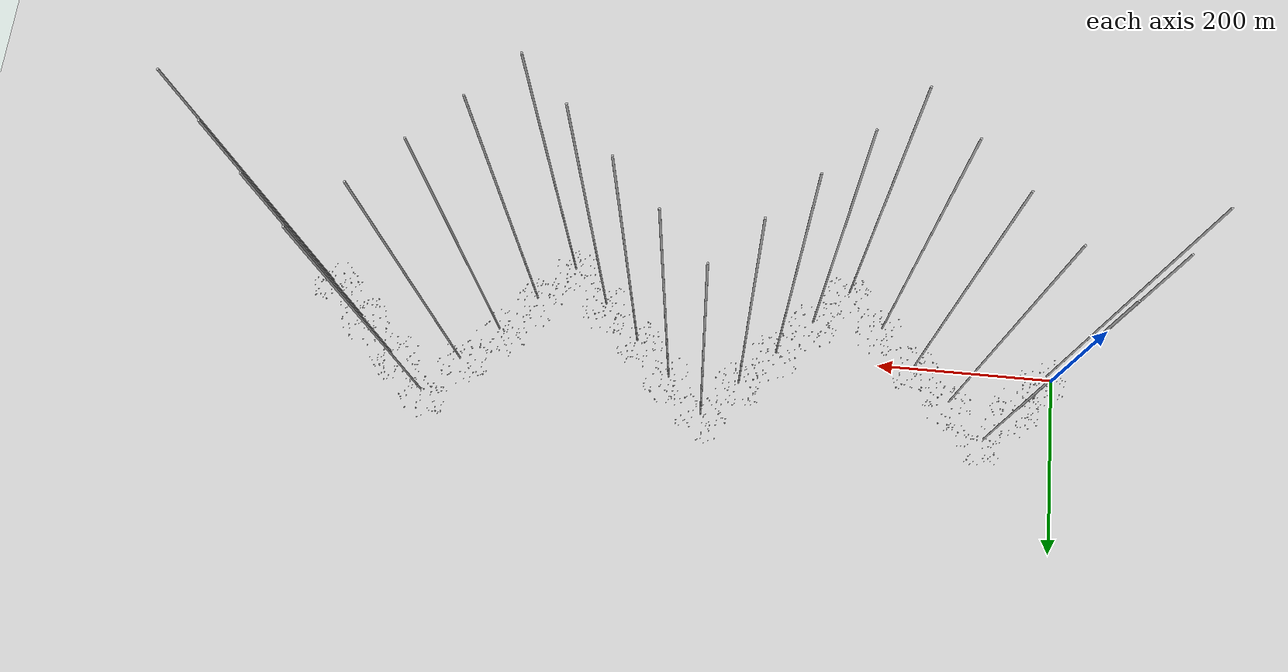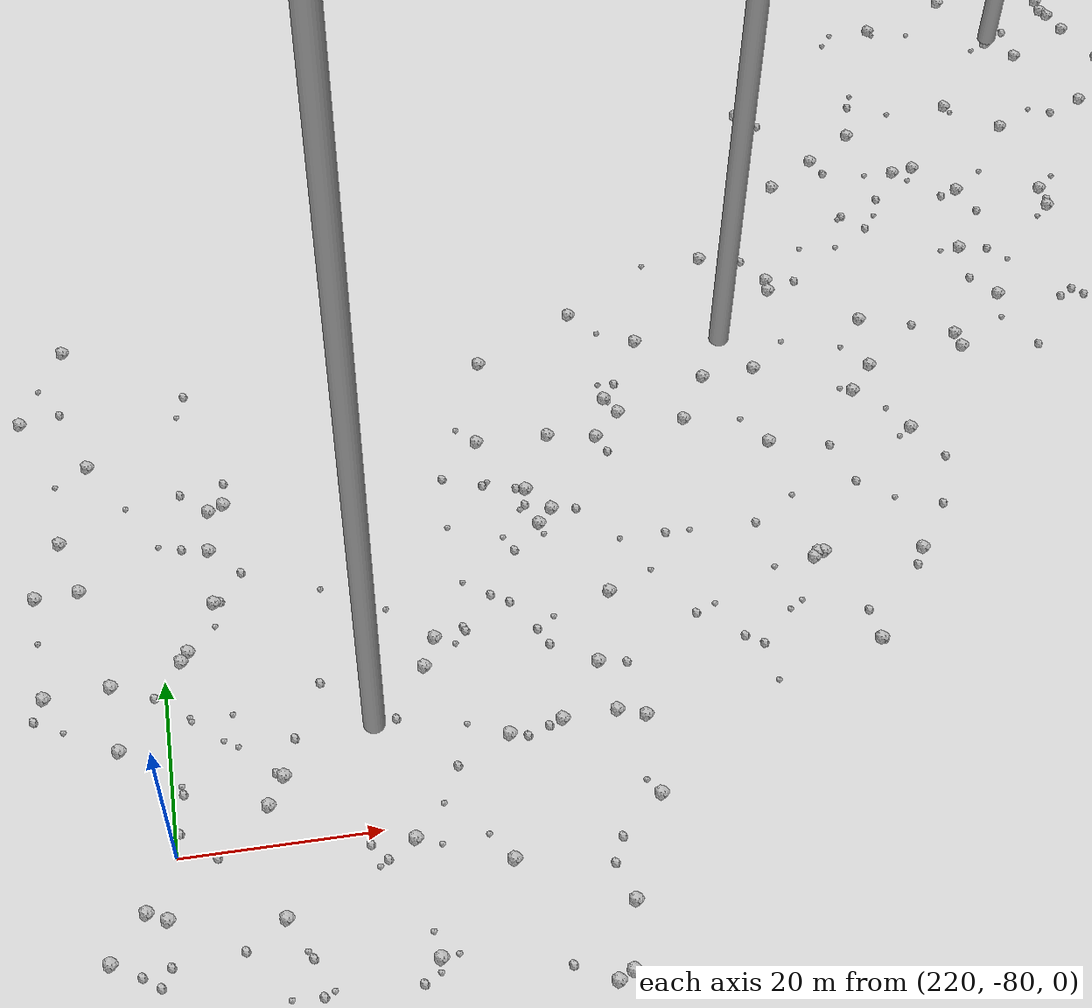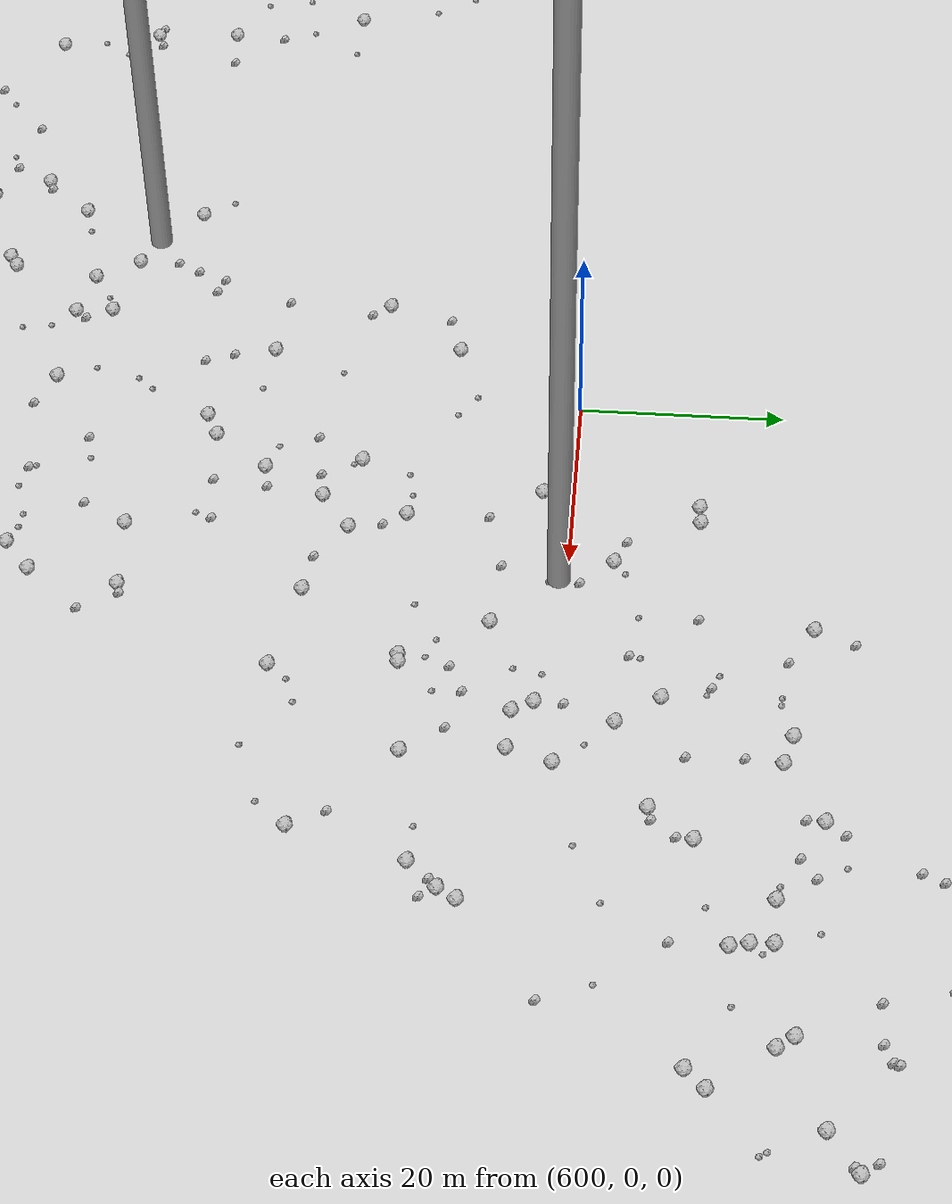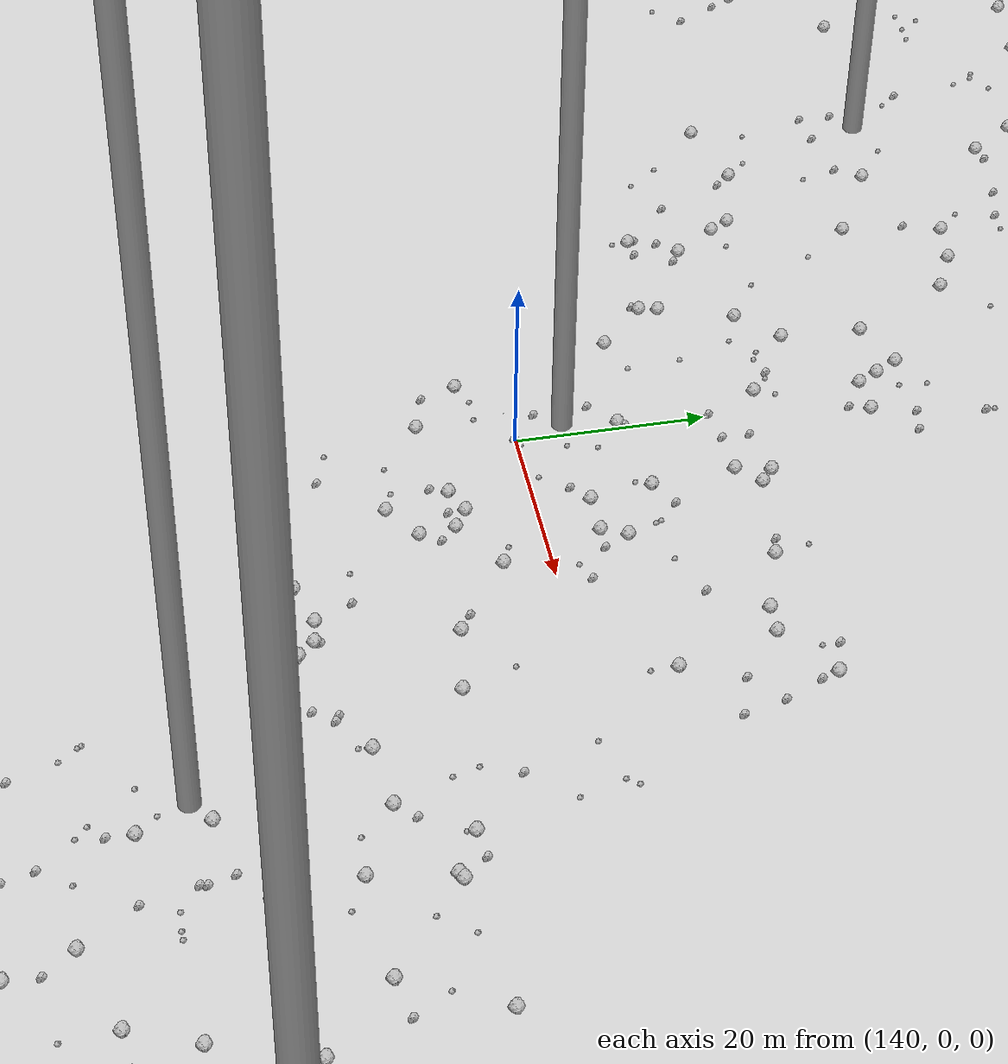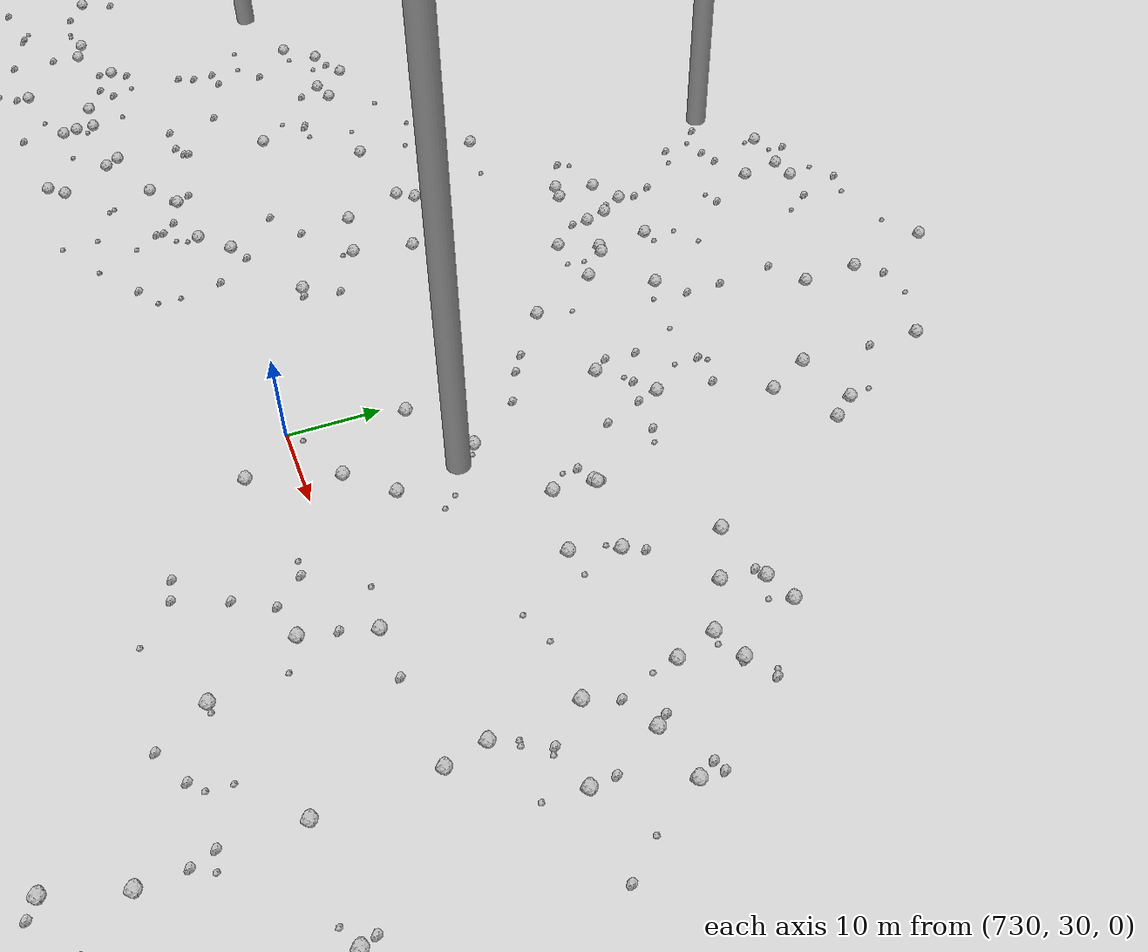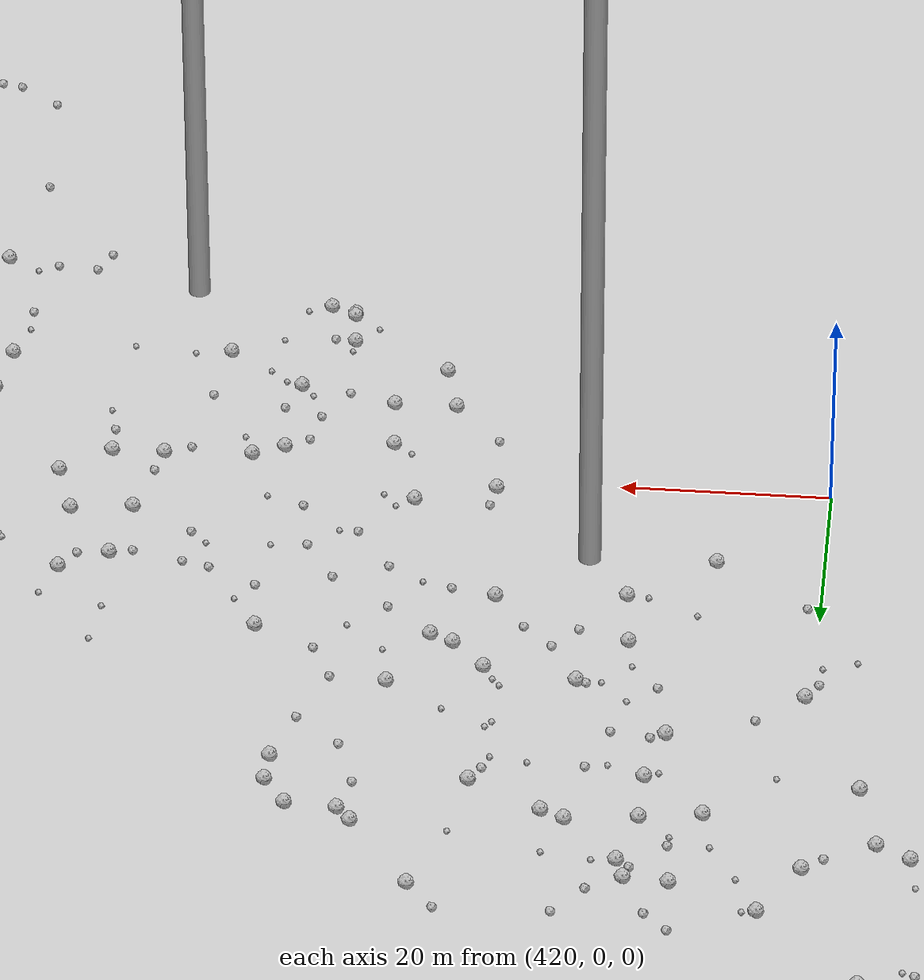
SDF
<sdf version="1.6">
 <world name="default">
  <include><uri>model://custom_ground</uri></include>
  <include><uri>model://sun</uri></include>
  <spherical_coordinates>
   <surface_model>EARTH_WGS84</surface_model>
   <latitude_deg>38.161479</latitude_deg>
   <longitude_deg>-122.454630</longitude_deg>
   <elevation>488.0</elevation>
   <heading_deg>90</heading_deg>
  </spherical_coordinates>
  <model name="rock1_0_0">
   <include><uri>model://rock1</uri><pose>23.220988975469275 5.820510014229846 0.5 0 0 0</pose></include>
  </model>
  <model name="rock1_0_1">
   <include><uri>model://rock1</uri><pose>33.792794628919744 -3.4639320478377265 0.5 0 0 0</pose></include>
  </model>
  <model name="rock1_0_2">
   <include><uri>model://rock1</uri><pose>31.907524415553496 7.5591250391693094 0.5 0 0 0</pose></include>
  </model>
  <model name="rock1_0_3">
   <include><uri>model://rock1</uri><pose>17.69303677341592 2.3890902227098962 0.5 0 0 0</pose></include>
  </model>
  <model name="rock1_0_4">
   <include><uri>model://rock1</uri><pose>20.086462942664994 22.993657708955226 0.5 0 0 0</pose></include>
  </model>
  <model name="rock1_0_5">
   <include><uri>model://rock1</uri><pose>4.604178330353918 11.873711802360248 0.5 0 0 0</pose></include>
  </model>
  <model name="rock1_0_6">
   <include><uri>model://rock1</uri><pose>18.171385407057883 5.347319320574684 0.5 0 0 0</pose></include>
  </model>
  <model name="rock1_0_7">
   <include><uri>model://rock1</uri><pose>-7.957063894364719 -7.845925525694234 0.5 0 0 0</pose></include>
  </model>
  <model name="rock1_0_8">
   <include><uri>model://rock1</uri><pose>-13.511640705450695 17.271928409048357 0.5 0 0 0</pose></include>
  </model>
  <model name="rock1_0_9">
   <include><uri>model://rock1</uri><pose>27.783730473057183 24.1337596332079 0.5 0 0 0</pose></include>
  </model>
  <model name="rock1_0_10">
   <include><uri>model://rock1</uri><pose>-10.081660505605615 15.766339073819267 0.5 0 0 0</pose></include>
  </model>
  <model name="rock1_0_11">
   <include><uri>model://rock1</uri><pose>17.67839904515685 19.0067844423302 0.5 0 0 0</pose></include>
  </model>
  <model name="rock1_0_12">
   <include><uri>model://rock1</uri><pose>6.4673340647353506 19.694675308255057 0.5 0 0 0</pose></include>
  </model>
  <model name="rock1_0_13">
   <include><uri>model://rock1</uri><pose>10.368140857335401 -20.162608091959576 0.5 0 0 0</pose></include>
  </model>
  <model name="rock1_0_14">
   <include><uri>model://rock1</uri><pose>-7.781905939895221 -4.483248876895917 0.5 0 0 0</pose></include>
  </model>
  <model name="rock1_0_15">
   <include><uri>model://rock1</uri><pose>13.37877628182784 4.165034022379942 0.5 0 0 0</pose></include>
  </model>
  <model name="rock1_0_16">
   <include><uri>model://rock1</uri><pose>29.54694392304328 3.3268915799610426 0.5 0 0 0</pose></include>
  </model>
  <model name="rock1_0_17">
   <include><uri>model://rock1</uri><pose>3.7447524847904 6.374596430432277 0.5 0 0 0</pose></include>
  </model>
  <model name="rock1_0_18">
   <include><uri>model://rock1</uri><pose>17.533979230223032 18.065082020691577 0.5 0 0 0</pose></include>
  </model>
  <model name="rock1_0_19">
   <include><uri>model://rock1</uri><pose>12.510756158098431 -9.159904143006841 0.5 0 0 0</pose></include>
  </model>
  <model name="rock1_0_20">
   <include><uri>model://rock1</uri><pose>24.300779887882335 9.55364378787938 0.5 0 0 0</pose></include>
  </model>
  <model name="rock1_0_21">
   <include><uri>model://rock1</uri><pose>19.708788993844422 20.947242781302087 0.5 0 0 0</pose></include>
  </model>
  <model name="rock1_0_22">
   <include><uri>model://rock1</uri><pose>25.980464051153646 15.7580526682218 0.5 0 0 0</pose></include>
  </model>
  <model name="rock1_0_23">
   <include><uri>model://rock1</uri><pose>29.07899307705862 -6.1403031985036485 0.5 0 0 0</pose></include>
  </model>
  <model name="rock1_0_24">
   <include><uri>model://rock1</uri><pose>-4.281392717502843 -25.60531287514989 0.5 0 0 0</pose></include>
  </model>
  <model name="rock1_0_25">
   <include><uri>model://rock1</uri><pose>16.137524039556567 6.581284793056831 0.5 0 0 0</pose></include>
  </model>
  <model name="rock1_0_26">
   <include><uri>model://rock1</uri><pose>19.280701794232726 26.689143217446812 0.5 0 0 0</pose></include>
  </model>
  <model name="rock2_0_0">
   <include><uri>model://rock2</uri><pose>19.36325180937098 6.2084218198945464 0.3 0 0 0</pose></include>
  </model>
  <model name="rock2_0_1">
   <include><uri>model://rock2</uri><pose>-6.718758750992587 -14.022659918875286 0.3 0 0 0</pose></include>
  </model>
  <model name="rock2_0_2">
   <include><uri>model://rock2</uri><pose>35.322692928760404 -3.8488249798559764 0.3 0 0 0</pose></include>
  </model>
  <model name="rock2_0_3">
   <include><uri>model://rock2</uri><pose>20.511510948463673 -9.601988709594252 0.3 0 0 0</pose></include>
  </model>
  <model name="rock2_0_4">
   <include><uri>model://rock2</uri><pose>2.9568355254754017 17.122855757103594 0.3 0 0 0</pose></include>
  </model>
  <model name="rock2_0_5">
   <include><uri>model://rock2</uri><pose>-0.8234523239721305 18.810734238481615 0.3 0 0 0</pose></include>
  </model>
  <model name="rock2_0_6">
   <include><uri>model://rock2</uri><pose>-8.19229693847026 20.79419822051441 0.3 0 0 0</pose></include>
  </model>
  <model name="rock2_0_7">
   <include><uri>model://rock2</uri><pose>-17.3346130708738 -1.55752797480784 0.3 0 0 0</pose></include>
  </model>
  <model name="rock2_0_8">
   <include><uri>model://rock2</uri><pose>2.7387045986148024 22.48302691366154 0.3 0 0 0</pose></include>
  </model>
  <model name="rock2_0_9">
   <include><uri>model://rock2</uri><pose>28.802625711199525 15.802874557716386 0.3 0 0 0</pose></include>
  </model>
  <model name="rock2_0_10">
   <include><uri>model://rock2</uri><pose>3.2537242921829126 -15.548270872032411 0.3 0 0 0</pose></include>
  </model>
  <model name="rock2_0_11">
   <include><uri>model://rock2</uri><pose>-11.50146437787158 -4.150143977890632 0.3 0 0 0</pose></include>
  </model>
  <model name="rock2_0_12">
   <include><uri>model://rock2</uri><pose>33.56200931945244 -9.515262635274691 0.3 0 0 0</pose></include>
  </model>
  <model name="rock2_0_13">
   <include><uri>model://rock2</uri><pose>6.6488730563404665 29.683984393056704 0.3 0 0 0</pose></include>
  </model>
  <model name="rock2_0_14">
   <include><uri>model://rock2</uri><pose>8.214373072764872 -10.153410761887045 0.3 0 0 0</pose></include>
  </model>
  <model name="rock2_0_15">
   <include><uri>model://rock2</uri><pose>25.76922836252701 24.918830348880334 0.3 0 0 0</pose></include>
  </model>
  <model name="rock2_0_16">
   <include><uri>model://rock2</uri><pose>28.76322943701974 -20.732616652225282 0.3 0 0 0</pose></include>
  </model>
  <model name="rock2_0_17">
   <include><uri>model://rock2</uri><pose>14.398317114473919 4.802330255670725 0.3 0 0 0</pose></include>
  </model>
  <model name="rock2_0_18">
   <include><uri>model://rock2</uri><pose>-13.635559538411359 -1.9275287236685088 0.3 0 0 0</pose></include>
  </model>
  <model name="rock2_0_19">
   <include><uri>model://rock2</uri><pose>14.858727074843607 21.236115074915936 0.3 0 0 0</pose></include>
  </model>
  <model name="rock2_0_20">
   <include><uri>model://rock2</uri><pose>-0.33577112230636885 -15.1539646909324 0.3 0 0 0</pose></include>
  </model>
  <model name="rock2_0_21">
   <include><uri>model://rock2</uri><pose>-0.9223862508070333 23.15767991120515 0.3 0 0 0</pose></include>
  </model>
  <model name="rock2_0_22">
   <include><uri>model://rock2</uri><pose>37.51508306629333 -2.008959090508643 0.3 0 0 0</pose></include>
  </model>
  <model name="rock2_0_23">
   <include><uri>model://rock2</uri><pose>16.221493210366006 28.666467969682543 0.3 0 0 0</pose></include>
  </model>
  <model name="rock2_0_24">
   <include><uri>model://rock2</uri><pose>1.575839912541639 -18.990855574833596 0.3 0 0 0</pose></include>
  </model>
  <model name="rock2_0_25">
   <include><uri>model://rock2</uri><pose>-7.255186921168022 -0.1578821125414933 0.3 0 0 0</pose></include>
  </model>
  <model name="rock2_0_26">
   <include><uri>model://rock2</uri><pose>20.060225200781495 23.197183530257597 0.3 0 0 0</pose></include>
  </model>
  <model name="rock3_0_0">
   <include><uri>model://rock3</uri><pose>-12.295662351623072 8.515622090377818 0.2 0 0 0</pose></include>
  </model>
  <model name="rock3_0_1">
   <include><uri>model://rock3</uri><pose>5.91461576531686 19.015597601108226 0.2 0 0 0</pose></include>
  </model>
  <model name="rock3_0_2">
   <include><uri>model://rock3</uri><pose>28.177330041536166 -10.966150777736495 0.2 0 0 0</pose></include>
  </model>
  <model name="rock3_0_3">
   <include><uri>model://rock3</uri><pose>-15.233732462656207 5.286902148351139 0.2 0 0 0</pose></include>
  </model>
  <model name="rock3_0_4">
   <include><uri>model://rock3</uri><pose>32.004686356206946 -9.312155160674475 0.2 0 0 0</pose></include>
  </model>
  <model name="rock3_0_5">
   <include><uri>model://rock3</uri><pose>6.337639276499068 20.536190064571784 0.2 0 0 0</pose></include>
  </model>
  <model name="rock3_0_6">
   <include><uri>model://rock3</uri><pose>16.533144397623616 28.09847777647162 0.2 0 0 0</pose></include>
  </model>
  <model name="rock3_0_7">
   <include><uri>model://rock3</uri><pose>-4.080290153212404 -20.925567370392862 0.2 0 0 0</pose></include>
  </model>
  <model name="rock3_0_8">
   <include><uri>model://rock3</uri><pose>16.288282804550647 -7.970815864971197 0.2 0 0 0</pose></include>
  </model>
  <model name="rock3_0_9">
   <include><uri>model://rock3</uri><pose>13.534108779670802 -18.61159352352351 0.2 0 0 0</pose></include>
  </model>
  <model name="rock3_0_10">
   <include><uri>model://rock3</uri><pose>-11.040588071443821 -0.4414981107553153 0.2 0 0 0</pose></include>
  </model>
  <model name="rock3_0_11">
   <include><uri>model://rock3</uri><pose>36.54074614395767 2.004797898894317 0.2 0 0 0</pose></include>
  </model>
  <model name="rock3_0_12">
   <include><uri>model://rock3</uri><pose>7.9645808919449905 -18.04277283883905 0.2 0 0 0</pose></include>
  </model>
  <model name="rock3_0_13">
   <include><uri>model://rock3</uri><pose>-5.994797287146341 -16.04408505613045 0.2 0 0 0</pose></include>
  </model>
  <model name="rock3_0_14">
   <include><uri>model://rock3</uri><pose>33.30321442315663 1.7654512003597667 0.2 0 0 0</pose></include>
  </model>
  <model name="rock3_0_15">
   <include><uri>model://rock3</uri><pose>20.282647790665763 -4.203104348048125 0.2 0 0 0</pose></include>
  </model>
  <model name="rock3_0_16">
   <include><uri>model://rock3</uri><pose>-10.697814919560571 1.9828942955705386 0.2 0 0 0</pose></include>
  </model>
  <model name="rock3_0_17">
   <include><uri>model://rock3</uri><pose>-1.8830582984873807 -18.709387191810045 0.2 0 0 0</pose></include>
  </model>
  <model name="rock3_0_18">
   <include><uri>model://rock3</uri><pose>-14.180252246549896 2.2313697865373285 0.2 0 0 0</pose></include>
  </model>
  <model name="rock3_0_19">
   <include><uri>model://rock3</uri><pose>34.50049169573828 14.14523136520031 0.2 0 0 0</pose></include>
  </model>
  <model name="rock3_0_20">
   <include><uri>model://rock3</uri><pose>18.9226163063654 10.258041004133283 0.2 0 0 0</pose></include>
  </model>
  <model name="rock3_0_21">
   <include><uri>model://rock3</uri><pose>4.639089289403763 4.427533639807841 0.2 0 0 0</pose></include>
  </model>
  <model name="rock3_0_22">
   <include><uri>model://rock3</uri><pose>11.578253629152726 -25.610131108934166 0.2 0 0 0</pose></include>
  </model>
  <model name="rock3_0_23">
   <include><uri>model://rock3</uri><pose>6.338918080459571 5.892019228665916 0.2 0 0 0</pose></include>
  </model>
  <model name="rock3_0_24">
   <include><uri>model://rock3</uri><pose>1.0222014806834743 -3.10473539233087 0.2 0 0 0</pose></include>
  </model>
  <model name="rock3_0_25">
   <include><uri>model://rock3</uri><pose>29.962652096664478 15.599742466736053 0.2 0 0 0</pose></include>
  </model>
  <model name="rock3_0_26">
   <include><uri>model://rock3</uri><pose>11.139274456239278 28.963571039839493 0.2 0 0 0</pose></include>
  </model>
  <model name="rock1_1_0">
   <include><uri>model://rock1</uri><pose>55.85472952976087 44.29970165927201 0.5 0 0 0</pose></include>
  </model>
  <model name="rock1_1_1">
   <include><uri>model://rock1</uri><pose>25.079259299280892 58.59426527433912 0.5 0 0 0</pose></include>
  </model>
  <model name="rock1_1_2">
   <include><uri>model://rock1</uri><pose>54.14787513559272 40.62892411444778 0.5 0 0 0</pose></include>
  </model>
  <model name="rock1_1_3">
   <include><uri>model://rock1</uri><pose>40.28485584168207 65.50750292518632 0.5 0 0 0</pose></include>
  </model>
  <model name="rock1_1_4">
   <include><uri>model://rock1</uri><pose>31.273880689412167 22.717289641769746 0.5 0 0 0</pose></include>
  </model>
  <model name="rock1_1_5">
   <include><uri>model://rock1</uri><pose>25.48404501461821 44.756868021786914 0.5 0 0 0</pose></include>
  </model>
  <model name="rock1_1_6">
   <include><uri>model://rock1</uri><pose>59.21735586920417 29.299776563568727 0.5 0 0 0</pose></include>
  </model>
  <model name="rock1_1_7">
   <include><uri>model://rock1</uri><pose>18.876080707104247 21.99277494326857 0.5 0 0 0</pose></include>
  </model>
  <model name="rock1_1_8">
   <include><uri>model://rock1</uri><pose>54.06528766467558 38.41278870405568 0.5 0 0 0</pose></include>
  </model>
  <model name="rock1_1_9">
   <include><uri>model://rock1</uri><pose>28.29229811373732 54.97300279839053 0.5 0 0 0</pose></include>
  </model>
  <model name="rock1_1_10">
   <include><uri>model://rock1</uri><pose>25.18626853530396 41.570946389318266 0.5 0 0 0</pose></include>
  </model>
  <model name="rock1_1_11">
   <include><uri>model://rock1</uri><pose>19.022448608063748 20.9524048790575 0.5 0 0 0</pose></include>
  </model>
  <model name="rock1_1_12">
   <include><uri>model://rock1</uri><pose>59.427552984802304 25.823934854584536 0.5 0 0 0</pose></include>
  </model>
  <model name="rock1_1_13">
   <include><uri>model://rock1</uri><pose>53.464925888803386 28.993089336318242 0.5 0 0 0</pose></include>
  </model>
  <model name="rock1_1_14">
   <include><uri>model://rock1</uri><pose>38.39179050687238 51.492996451768754 0.5 0 0 0</pose></include>
  </model>
  <model name="rock1_1_15">
   <include><uri>model://rock1</uri><pose>57.21909343543721 38.33806997598314 0.5 0 0 0</pose></include>
  </model>
  <model name="rock1_1_16">
   <include><uri>model://rock1</uri><pose>65.63259082441272 42.00589684206355 0.5 0 0 0</pose></include>
  </model>
  <model name="rock1_1_17">
   <include><uri>model://rock1</uri><pose>28.046836771033707 46.00254937455005 0.5 0 0 0</pose></include>
  </model>
  <model name="rock1_1_18">
   <include><uri>model://rock1</uri><pose>32.148739488153566 12.163504679858912 0.5 0 0 0</pose></include>
  </model>
  <model name="rock1_1_19">
   <include><uri>model://rock1</uri><pose>21.600790503526824 42.14131578085696 0.5 0 0 0</pose></include>
  </model>
  <model name="rock1_1_20">
   <include><uri>model://rock1</uri><pose>47.691851010969 68.31147144439578 0.5 0 0 0</pose></include>
  </model>
  <model name="rock1_1_21">
   <include><uri>model://rock1</uri><pose>15.390441314250602 54.32213749438404 0.5 0 0 0</pose></include>
  </model>
  <model name="rock1_1_22">
   <include><uri>model://rock1</uri><pose>15.024032467516994 33.73925521016512 0.5 0 0 0</pose></include>
  </model>
  <model name="rock1_1_23">
   <include><uri>model://rock1</uri><pose>51.0839567169075 30.505851610027722 0.5 0 0 0</pose></include>
  </model>
  <model name="rock1_1_24">
   <include><uri>model://rock1</uri><pose>63.23115761067044 57.94132193356897 0.5 0 0 0</pose></include>
  </model>
  <model name="rock1_1_25">
   <include><uri>model://rock1</uri><pose>38.09244784681245 15.993412364088789 0.5 0 0 0</pose></include>
  </model>
  <model name="rock1_1_26">
   <include><uri>model://rock1</uri><pose>42.752973920381024 37.93103923032396 0.5 0 0 0</pose></include>
  </model>
  <model name="rock2_1_0">
   <include><uri>model://rock2</uri><pose>38.47881575343753 29.320043441827504 0.3 0 0 0</pose></include>
  </model>
  <model name="rock2_1_1">
   <include><uri>model://rock2</uri><pose>67.04768262510933 39.490818322354194 0.3 0 0 0</pose></include>
  </model>
  <model name="rock2_1_2">
   <include><uri>model://rock2</uri><pose>38.992295472954865 55.92712395413405 0.3 0 0 0</pose></include>
  </model>
  <model name="rock2_1_3">
   <include><uri>model://rock2</uri><pose>13.910516819318644 32.29703213694736 0.3 0 0 0</pose></include>
  </model>
  <model name="rock2_1_4">
   <include><uri>model://rock2</uri><pose>23.64997803003329 33.75067337596299 0.3 0 0 0</pose></include>
  </model>
  <model name="rock2_1_5">
   <include><uri>model://rock2</uri><pose>45.39857051914308 27.444955083419103 0.3 0 0 0</pose></include>
  </model>
  <model name="rock2_1_6">
   <include><uri>model://rock2</uri><pose>40.653724016619506 32.48995283379219 0.3 0 0 0</pose></include>
  </model>
  <model name="rock2_1_7">
   <include><uri>model://rock2</uri><pose>64.11907008773545 45.760513449806496 0.3 0 0 0</pose></include>
  </model>
  <model name="rock2_1_8">
   <include><uri>model://rock2</uri><pose>43.10151114466595 42.84354209703411 0.3 0 0 0</pose></include>
  </model>
  <model name="rock2_1_9">
   <include><uri>model://rock2</uri><pose>45.65281828554539 20.01978208180855 0.3 0 0 0</pose></include>
  </model>
  <model name="rock2_1_10">
   <include><uri>model://rock2</uri><pose>14.115875645497677 34.756150610162805 0.3 0 0 0</pose></include>
  </model>
  <model name="rock2_1_11">
   <include><uri>model://rock2</uri><pose>23.728721188931736 26.404569929978123 0.3 0 0 0</pose></include>
  </model>
  <model name="rock2_1_12">
   <include><uri>model://rock2</uri><pose>31.90589859236774 29.749387022472266 0.3 0 0 0</pose></include>
  </model>
  <model name="rock2_1_13">
   <include><uri>model://rock2</uri><pose>53.711108335547046 13.609448193212884 0.3 0 0 0</pose></include>
  </model>
  <model name="rock2_1_14">
   <include><uri>model://rock2</uri><pose>21.22013361877454 47.24471753211265 0.3 0 0 0</pose></include>
  </model>
  <model name="rock2_1_15">
   <include><uri>model://rock2</uri><pose>37.86748764696978 17.62818267342138 0.3 0 0 0</pose></include>
  </model>
  <model name="rock2_1_16">
   <include><uri>model://rock2</uri><pose>13.580527307497912 37.71606545488571 0.3 0 0 0</pose></include>
  </model>
  <model name="rock2_1_17">
   <include><uri>model://rock2</uri><pose>36.74142569755368 58.155322094133126 0.3 0 0 0</pose></include>
  </model>
  <model name="rock2_1_18">
   <include><uri>model://rock2</uri><pose>46.674175249204936 44.464359228549256 0.3 0 0 0</pose></include>
  </model>
  <model name="rock2_1_19">
   <include><uri>model://rock2</uri><pose>69.28547411930845 35.04969331304993 0.3 0 0 0</pose></include>
  </model>
  <model name="rock2_1_20">
   <include><uri>model://rock2</uri><pose>17.61282793068748 51.02702203293547 0.3 0 0 0</pose></include>
  </model>
  <model name="rock2_1_21">
   <include><uri>model://rock2</uri><pose>28.587153918247207 32.22490243971829 0.3 0 0 0</pose></include>
  </model>
  <model name="rock2_1_22">
   <include><uri>model://rock2</uri><pose>61.07990452873348 29.602639311243998 0.3 0 0 0</pose></include>
  </model>
  <model name="rock2_1_23">
   <include><uri>model://rock2</uri><pose>41.02857480610694 30.56726615773998 0.3 0 0 0</pose></include>
  </model>
  <model name="rock2_1_24">
   <include><uri>model://rock2</uri><pose>64.11379617459158 23.64417736592725 0.3 0 0 0</pose></include>
  </model>
  <model name="rock2_1_25">
   <include><uri>model://rock2</uri><pose>19.674235906796646 39.99424702281124 0.3 0 0 0</pose></include>
  </model>
  <model name="rock2_1_26">
   <include><uri>model://rock2</uri><pose>33.35070649712385 57.88914508218028 0.3 0 0 0</pose></include>
  </model>
  <model name="rock3_1_0">
   <include><uri>model://rock3</uri><pose>52.91646965715066 26.798752384780514 0.2 0 0 0</pose></include>
  </model>
  <model name="rock3_1_1">
   <include><uri>model://rock3</uri><pose>58.40804976939948 29.194456577110063 0.2 0 0 0</pose></include>
  </model>
  <model name="rock3_1_2">
   <include><uri>model://rock3</uri><pose>66.48348521158404 32.10881691196232 0.2 0 0 0</pose></include>
  </model>
  <model name="rock3_1_3">
   <include><uri>model://rock3</uri><pose>59.21231043840926 48.89104150326864 0.2 0 0 0</pose></include>
  </model>
  <model name="rock3_1_4">
   <include><uri>model://rock3</uri><pose>19.805600196075318 20.392510366189903 0.2 0 0 0</pose></include>
  </model>
  <model name="rock3_1_5">
   <include><uri>model://rock3</uri><pose>42.623873519490374 39.074638515183466 0.2 0 0 0</pose></include>
  </model>
  <model name="rock3_1_6">
   <include><uri>model://rock3</uri><pose>60.4233909955076 35.603642091105954 0.2 0 0 0</pose></include>
  </model>
  <model name="rock3_1_7">
   <include><uri>model://rock3</uri><pose>36.45664893861546 67.47463107992002 0.2 0 0 0</pose></include>
  </model>
  <model name="rock3_1_8">
   <include><uri>model://rock3</uri><pose>15.389248161228386 29.94653655286875 0.2 0 0 0</pose></include>
  </model>
  <model name="rock3_1_9">
   <include><uri>model://rock3</uri><pose>31.982628039783656 46.46240204700766 0.2 0 0 0</pose></include>
  </model>
  <model name="rock3_1_10">
   <include><uri>model://rock3</uri><pose>31.881396958088867 20.634513512187546 0.2 0 0 0</pose></include>
  </model>
  <model name="rock3_1_11">
   <include><uri>model://rock3</uri><pose>33.570347365182286 44.598984922454356 0.2 0 0 0</pose></include>
  </model>
  <model name="rock3_1_12">
   <include><uri>model://rock3</uri><pose>58.51094944002835 55.21443567974542 0.2 0 0 0</pose></include>
  </model>
  <model name="rock3_1_13">
   <include><uri>model://rock3</uri><pose>21.56937820080294 21.889853048809385 0.2 0 0 0</pose></include>
  </model>
  <model name="rock3_1_14">
   <include><uri>model://rock3</uri><pose>22.253577044508468 16.725600765922728 0.2 0 0 0</pose></include>
  </model>
  <model name="rock3_1_15">
   <include><uri>model://rock3</uri><pose>14.035724145394264 46.81641562211192 0.2 0 0 0</pose></include>
  </model>
  <model name="rock3_1_16">
   <include><uri>model://rock3</uri><pose>46.877049311702 62.66589732397155 0.2 0 0 0</pose></include>
  </model>
  <model name="rock3_1_17">
   <include><uri>model://rock3</uri><pose>20.86626207143004 20.831142658668966 0.2 0 0 0</pose></include>
  </model>
  <model name="rock3_1_18">
   <include><uri>model://rock3</uri><pose>18.93589966162642 57.9592456902801 0.2 0 0 0</pose></include>
  </model>
  <model name="rock3_1_19">
   <include><uri>model://rock3</uri><pose>24.028562442099894 47.466840324403236 0.2 0 0 0</pose></include>
  </model>
  <model name="rock3_1_20">
   <include><uri>model://rock3</uri><pose>39.883880524349046 63.93966033363171 0.2 0 0 0</pose></include>
  </model>
  <model name="rock3_1_21">
   <include><uri>model://rock3</uri><pose>45.6328760151602 38.13086925067747 0.2 0 0 0</pose></include>
  </model>
  <model name="rock3_1_22">
   <include><uri>model://rock3</uri><pose>34.13214120466439 69.27107678438021 0.2 0 0 0</pose></include>
  </model>
  <model name="rock3_1_23">
   <include><uri>model://rock3</uri><pose>37.36008637769008 36.22961442013576 0.2 0 0 0</pose></include>
  </model>
  <model name="rock3_1_24">
   <include><uri>model://rock3</uri><pose>13.70618724183215 25.625288355217606 0.2 0 0 0</pose></include>
  </model>
  <model name="rock3_1_25">
   <include><uri>model://rock3</uri><pose>20.593209018089695 48.75369273965264 0.2 0 0 0</pose></include>
  </model>
  <model name="rock3_1_26">
   <include><uri>model://rock3</uri><pose>24.24813992220247 59.19326197262828 0.2 0 0 0</pose></include>
  </model>
  <model name="rock1_2_0">
   <include><uri>model://rock1</uri><pose>82.31474458500297 72.89395012442228 0.5 0 0 0</pose></include>
  </model>
  <model name="rock1_2_1">
   <include><uri>model://rock1</uri><pose>96.74521222749473 85.85676102883477 0.5 0 0 0</pose></include>
  </model>
  <model name="rock1_2_2">
   <include><uri>model://rock1</uri><pose>74.0237633456661 51.79940082913083 0.5 0 0 0</pose></include>
  </model>
  <model name="rock1_2_3">
   <include><uri>model://rock1</uri><pose>88.3968796959802 72.65937993490051 0.5 0 0 0</pose></include>
  </model>
  <model name="rock1_2_4">
   <include><uri>model://rock1</uri><pose>97.69310807420686 67.27306924240222 0.5 0 0 0</pose></include>
  </model>
  <model name="rock1_2_5">
   <include><uri>model://rock1</uri><pose>55.06063261466285 64.4535433698853 0.5 0 0 0</pose></include>
  </model>
  <model name="rock1_2_6">
   <include><uri>model://rock1</uri><pose>82.00641426956886 105.67038957318955 0.5 0 0 0</pose></include>
  </model>
  <model name="rock1_2_7">
   <include><uri>model://rock1</uri><pose>67.99216879608538 76.64390589390483 0.5 0 0 0</pose></include>
  </model>
  <model name="rock1_2_8">
   <include><uri>model://rock1</uri><pose>70.05338267298731 97.76936224848603 0.5 0 0 0</pose></include>
  </model>
  <model name="rock1_2_9">
   <include><uri>model://rock1</uri><pose>97.08109716188237 72.75896078680375 0.5 0 0 0</pose></include>
  </model>
  <model name="rock1_2_10">
   <include><uri>model://rock1</uri><pose>89.47807284814662 76.3576153673404 0.5 0 0 0</pose></include>
  </model>
  <model name="rock1_2_11">
   <include><uri>model://rock1</uri><pose>63.16958862948124 92.46051353372056 0.5 0 0 0</pose></include>
  </model>
  <model name="rock1_2_12">
   <include><uri>model://rock1</uri><pose>60.64060662204536 59.08396924181508 0.5 0 0 0</pose></include>
  </model>
  <model name="rock1_2_13">
   <include><uri>model://rock1</uri><pose>75.7637296441607 97.67560415440911 0.5 0 0 0</pose></include>
  </model>
  <model name="rock1_2_14">
   <include><uri>model://rock1</uri><pose>101.24988608423112 85.58483679970824 0.5 0 0 0</pose></include>
  </model>
  <model name="rock1_2_15">
   <include><uri>model://rock1</uri><pose>61.51626070303613 76.7715602435088 0.5 0 0 0</pose></include>
  </model>
  <model name="rock1_2_16">
   <include><uri>model://rock1</uri><pose>95.34572144348911 74.82205322713705 0.5 0 0 0</pose></include>
  </model>
  <model name="rock1_2_17">
   <include><uri>model://rock1</uri><pose>64.25371879442342 79.99994560902655 0.5 0 0 0</pose></include>
  </model>
  <model name="rock1_2_18">
   <include><uri>model://rock1</uri><pose>105.03263884521628 70.47778425793432 0.5 0 0 0</pose></include>
  </model>
  <model name="rock1_2_19">
   <include><uri>model://rock1</uri><pose>55.22396455578804 67.0012061086359 0.5 0 0 0</pose></include>
  </model>
  <model name="rock1_2_20">
   <include><uri>model://rock1</uri><pose>92.4648733628088 96.6846869698492 0.5 0 0 0</pose></include>
  </model>
  <model name="rock1_2_21">
   <include><uri>model://rock1</uri><pose>56.91053871678096 68.65506594897187 0.5 0 0 0</pose></include>
  </model>
  <model name="rock1_2_22">
   <include><uri>model://rock1</uri><pose>92.65294032394635 72.0909915179342 0.5 0 0 0</pose></include>
  </model>
  <model name="rock1_2_23">
   <include><uri>model://rock1</uri><pose>73.85760526869345 74.01455432431496 0.5 0 0 0</pose></include>
  </model>
  <model name="rock1_2_24">
   <include><uri>model://rock1</uri><pose>86.77148061760408 76.27471821619886 0.5 0 0 0</pose></include>
  </model>
  <model name="rock1_2_25">
   <include><uri>model://rock1</uri><pose>94.23954818973489 101.09141787863904 0.5 0 0 0</pose></include>
  </model>
  <model name="rock1_2_26">
   <include><uri>model://rock1</uri><pose>69.93087076094416 83.87556157170951 0.5 0 0 0</pose></include>
  </model>
  <model name="rock2_2_0">
   <include><uri>model://rock2</uri><pose>60.650869026232 79.53832283167213 0.3 0 0 0</pose></include>
  </model>
  <model name="rock2_2_1">
   <include><uri>model://rock2</uri><pose>97.07329486668922 103.43266977849682 0.3 0 0 0</pose></include>
  </model>
  <model name="rock2_2_2">
   <include><uri>model://rock2</uri><pose>74.1124291703099 101.52567958689079 0.3 0 0 0</pose></include>
  </model>
  <model name="rock2_2_3">
   <include><uri>model://rock2</uri><pose>82.62469803514696 77.28200945322968 0.3 0 0 0</pose></include>
  </model>
  <model name="rock2_2_4">
   <include><uri>model://rock2</uri><pose>90.98455400016002 106.22354701362758 0.3 0 0 0</pose></include>
  </model>
  <model name="rock2_2_5">
   <include><uri>model://rock2</uri><pose>89.92534828741212 94.42915653930342 0.3 0 0 0</pose></include>
  </model>
  <model name="rock2_2_6">
   <include><uri>model://rock2</uri><pose>66.21443843899463 84.37723828116486 0.3 0 0 0</pose></include>
  </model>
  <model name="rock2_2_7">
   <include><uri>model://rock2</uri><pose>67.34206494836148 94.82911455223484 0.3 0 0 0</pose></include>
  </model>
  <model name="rock2_2_8">
   <include><uri>model://rock2</uri><pose>68.45346751959914 71.47558195039532 0.3 0 0 0</pose></include>
  </model>
  <model name="rock2_2_9">
   <include><uri>model://rock2</uri><pose>101.85888637847756 73.66058691670077 0.3 0 0 0</pose></include>
  </model>
  <model name="rock2_2_10">
   <include><uri>model://rock2</uri><pose>69.32417157434006 83.369500527707 0.3 0 0 0</pose></include>
  </model>
  <model name="rock2_2_11">
   <include><uri>model://rock2</uri><pose>62.7166574417335 103.79699037027247 0.3 0 0 0</pose></include>
  </model>
  <model name="rock2_2_12">
   <include><uri>model://rock2</uri><pose>89.6117002447312 89.60434911023032 0.3 0 0 0</pose></include>
  </model>
  <model name="rock2_2_13">
   <include><uri>model://rock2</uri><pose>106.78740279015427 74.55045481938363 0.3 0 0 0</pose></include>
  </model>
  <model name="rock2_2_14">
   <include><uri>model://rock2</uri><pose>77.23067078816175 92.16411433851883 0.3 0 0 0</pose></include>
  </model>
  <model name="rock2_2_15">
   <include><uri>model://rock2</uri><pose>92.0142813870581 77.10618989055814 0.3 0 0 0</pose></include>
  </model>
  <model name="rock2_2_16">
   <include><uri>model://rock2</uri><pose>76.16912169588522 85.96591315202664 0.3 0 0 0</pose></include>
  </model>
  <model name="rock2_2_17">
   <include><uri>model://rock2</uri><pose>89.12079877465854 56.08146620480478 0.3 0 0 0</pose></include>
  </model>
  <model name="rock2_2_18">
   <include><uri>model://rock2</uri><pose>89.85348433299295 105.25114789566643 0.3 0 0 0</pose></include>
  </model>
  <model name="rock2_2_19">
   <include><uri>model://rock2</uri><pose>57.01962685369136 77.65888798182286 0.3 0 0 0</pose></include>
  </model>
  <model name="rock2_2_20">
   <include><uri>model://rock2</uri><pose>74.19546005793511 88.24878920096401 0.3 0 0 0</pose></include>
  </model>
  <model name="rock2_2_21">
   <include><uri>model://rock2</uri><pose>58.33590628242366 96.49270393033777 0.3 0 0 0</pose></include>
  </model>
  <model name="rock2_2_22">
   <include><uri>model://rock2</uri><pose>76.68052625803759 77.97580989101493 0.3 0 0 0</pose></include>
  </model>
  <model name="rock2_2_23">
   <include><uri>model://rock2</uri><pose>98.96327256356533 81.72577687450712 0.3 0 0 0</pose></include>
  </model>
  <model name="rock2_2_24">
   <include><uri>model://rock2</uri><pose>96.72876319239037 73.24864739586955 0.3 0 0 0</pose></include>
  </model>
  <model name="rock2_2_25">
   <include><uri>model://rock2</uri><pose>82.8890488808759 76.6274571087881 0.3 0 0 0</pose></include>
  </model>
  <model name="rock2_2_26">
   <include><uri>model://rock2</uri><pose>73.37696557424451 93.68105392019532 0.3 0 0 0</pose></include>
  </model>
  <model name="rock3_2_0">
   <include><uri>model://rock3</uri><pose>67.04125761975357 100.66531861655137 0.2 0 0 0</pose></include>
  </model>
  <model name="rock3_2_1">
   <include><uri>model://rock3</uri><pose>76.03013558329815 75.35693826199856 0.2 0 0 0</pose></include>
  </model>
  <model name="rock3_2_2">
   <include><uri>model://rock3</uri><pose>64.21183609105736 85.66544479805899 0.2 0 0 0</pose></include>
  </model>
  <model name="rock3_2_3">
   <include><uri>model://rock3</uri><pose>87.14608399998804 66.11913823544641 0.2 0 0 0</pose></include>
  </model>
  <model name="rock3_2_4">
   <include><uri>model://rock3</uri><pose>74.35411474224429 63.36090460301296 0.2 0 0 0</pose></include>
  </model>
  <model name="rock3_2_5">
   <include><uri>model://rock3</uri><pose>73.06492947854852 61.12004295687057 0.2 0 0 0</pose></include>
  </model>
  <model name="rock3_2_6">
   <include><uri>model://rock3</uri><pose>97.62098659543388 73.17882340362773 0.2 0 0 0</pose></include>
  </model>
  <model name="rock3_2_7">
   <include><uri>model://rock3</uri><pose>97.56456288730288 102.9106968407679 0.2 0 0 0</pose></include>
  </model>
  <model name="rock3_2_8">
   <include><uri>model://rock3</uri><pose>104.66114732336794 66.95029991672502 0.2 0 0 0</pose></include>
  </model>
  <model name="rock3_2_9">
   <include><uri>model://rock3</uri><pose>51.28160966354174 73.7107716481091 0.2 0 0 0</pose></include>
  </model>
  <model name="rock3_2_10">
   <include><uri>model://rock3</uri><pose>93.219312212307 82.9252646048687 0.2 0 0 0</pose></include>
  </model>
  <model name="rock3_2_11">
   <include><uri>model://rock3</uri><pose>90.56753437206142 54.207310853897646 0.2 0 0 0</pose></include>
  </model>
  <model name="rock3_2_12">
   <include><uri>model://rock3</uri><pose>56.53436065923412 71.55234573373983 0.2 0 0 0</pose></include>
  </model>
  <model name="rock3_2_13">
   <include><uri>model://rock3</uri><pose>105.46767024487093 85.9578390814459 0.2 0 0 0</pose></include>
  </model>
  <model name="rock3_2_14">
   <include><uri>model://rock3</uri><pose>61.08545130472126 56.90076713706483 0.2 0 0 0</pose></include>
  </model>
  <model name="rock3_2_15">
   <include><uri>model://rock3</uri><pose>87.99816869897467 63.80902779826463 0.2 0 0 0</pose></include>
  </model>
  <model name="rock3_2_16">
   <include><uri>model://rock3</uri><pose>89.54054747699482 67.66673281494357 0.2 0 0 0</pose></include>
  </model>
  <model name="rock3_2_17">
   <include><uri>model://rock3</uri><pose>52.21823576762979 79.61706220163184 0.2 0 0 0</pose></include>
  </model>
  <model name="rock3_2_18">
   <include><uri>model://rock3</uri><pose>62.95145090615353 90.13213705543147 0.2 0 0 0</pose></include>
  </model>
  <model name="rock3_2_19">
   <include><uri>model://rock3</uri><pose>86.30074096448021 66.48510055559971 0.2 0 0 0</pose></include>
  </model>
  <model name="rock3_2_20">
   <include><uri>model://rock3</uri><pose>69.85050207707044 98.75712871637867 0.2 0 0 0</pose></include>
  </model>
  <model name="rock3_2_21">
   <include><uri>model://rock3</uri><pose>86.47616668035806 102.28926061501456 0.2 0 0 0</pose></include>
  </model>
  <model name="rock3_2_22">
   <include><uri>model://rock3</uri><pose>103.67768637188745 77.17755680631932 0.2 0 0 0</pose></include>
  </model>
  <model name="rock3_2_23">
   <include><uri>model://rock3</uri><pose>83.01145606058175 76.74885992121128 0.2 0 0 0</pose></include>
  </model>
  <model name="rock3_2_24">
   <include><uri>model://rock3</uri><pose>77.97091642882154 61.03972333454336 0.2 0 0 0</pose></include>
  </model>
  <model name="rock3_2_25">
   <include><uri>model://rock3</uri><pose>72.13979875261037 74.93062106004585 0.2 0 0 0</pose></include>
  </model>
  <model name="rock3_2_26">
   <include><uri>model://rock3</uri><pose>75.84682426995337 61.16995446677187 0.2 0 0 0</pose></include>
  </model>
  <model name="rock1_3_0">
   <include><uri>model://rock1</uri><pose>122.05444376829885 17.239023677696192 0.5 0 0 0</pose></include>
  </model>
  <model name="rock1_3_1">
   <include><uri>model://rock1</uri><pose>138.1253999746591 37.39219008919437 0.5 0 0 0</pose></include>
  </model>
  <model name="rock1_3_2">
   <include><uri>model://rock1</uri><pose>114.70966080260516 53.76963665263507 0.5 0 0 0</pose></include>
  </model>
  <model name="rock1_3_3">
   <include><uri>model://rock1</uri><pose>103.68894606612321 47.81855088776132 0.5 0 0 0</pose></include>
  </model>
  <model name="rock1_3_4">
   <include><uri>model://rock1</uri><pose>119.63352852850753 53.02037005131432 0.5 0 0 0</pose></include>
  </model>
  <model name="rock1_3_5">
   <include><uri>model://rock1</uri><pose>111.28076471943623 64.68162194671254 0.5 0 0 0</pose></include>
  </model>
  <model name="rock1_3_6">
   <include><uri>model://rock1</uri><pose>115.59468769608284 65.12666096319768 0.5 0 0 0</pose></include>
  </model>
  <model name="rock1_3_7">
   <include><uri>model://rock1</uri><pose>135.51387227364611 42.11386492382909 0.5 0 0 0</pose></include>
  </model>
  <model name="rock1_3_8">
   <include><uri>model://rock1</uri><pose>108.86124978278164 30.55699616215897 0.5 0 0 0</pose></include>
  </model>
  <model name="rock1_3_9">
   <include><uri>model://rock1</uri><pose>122.45127873973306 19.256425648983427 0.5 0 0 0</pose></include>
  </model>
  <model name="rock1_3_10">
   <include><uri>model://rock1</uri><pose>100.69718050281554 32.84951213675615 0.5 0 0 0</pose></include>
  </model>
  <model name="rock1_3_11">
   <include><uri>model://rock1</uri><pose>101.09642958046545 62.24985805901021 0.5 0 0 0</pose></include>
  </model>
  <model name="rock1_3_12">
   <include><uri>model://rock1</uri><pose>91.99894618408145 30.63486162458153 0.5 0 0 0</pose></include>
  </model>
  <model name="rock1_3_13">
   <include><uri>model://rock1</uri><pose>137.37285587671442 26.063566812084424 0.5 0 0 0</pose></include>
  </model>
  <model name="rock1_3_14">
   <include><uri>model://rock1</uri><pose>125.16621718936682 27.133039862332915 0.5 0 0 0</pose></include>
  </model>
  <model name="rock1_3_15">
   <include><uri>model://rock1</uri><pose>113.09945057747126 23.853906005335535 0.5 0 0 0</pose></include>
  </model>
  <model name="rock1_3_16">
   <include><uri>model://rock1</uri><pose>129.34408334141767 31.239608988162285 0.5 0 0 0</pose></include>
  </model>
  <model name="rock1_3_17">
   <include><uri>model://rock1</uri><pose>142.3420167270417 37.41893937826683 0.5 0 0 0</pose></include>
  </model>
  <model name="rock1_3_18">
   <include><uri>model://rock1</uri><pose>110.47699548557702 18.716235848923517 0.5 0 0 0</pose></include>
  </model>
  <model name="rock1_3_19">
   <include><uri>model://rock1</uri><pose>128.32078624675015 61.457160860675806 0.5 0 0 0</pose></include>
  </model>
  <model name="rock1_3_20">
   <include><uri>model://rock1</uri><pose>124.31953453682263 50.66112137290793 0.5 0 0 0</pose></include>
  </model>
  <model name="rock1_3_21">
   <include><uri>model://rock1</uri><pose>129.87864486887187 39.900588794376446 0.5 0 0 0</pose></include>
  </model>
  <model name="rock1_3_22">
   <include><uri>model://rock1</uri><pose>110.08267507169575 28.4280921550492 0.5 0 0 0</pose></include>
  </model>
  <model name="rock1_3_23">
   <include><uri>model://rock1</uri><pose>117.68873950703117 62.345559245799116 0.5 0 0 0</pose></include>
  </model>
  <model name="rock1_3_24">
   <include><uri>model://rock1</uri><pose>136.9209768985305 39.637160340263485 0.5 0 0 0</pose></include>
  </model>
  <model name="rock1_3_25">
   <include><uri>model://rock1</uri><pose>126.9718988183848 12.297317159915398 0.5 0 0 0</pose></include>
  </model>
  <model name="rock1_3_26">
   <include><uri>model://rock1</uri><pose>112.74417150155176 42.89666215002171 0.5 0 0 0</pose></include>
  </model>
  <model name="rock2_3_0">
   <include><uri>model://rock2</uri><pose>91.63165365973016 43.78580001205402 0.3 0 0 0</pose></include>
  </model>
  <model name="rock2_3_1">
   <include><uri>model://rock2</uri><pose>113.26223410367473 49.76203850998765 0.3 0 0 0</pose></include>
  </model>
  <model name="rock2_3_2">
   <include><uri>model://rock2</uri><pose>144.63178625349488 49.310923807381194 0.3 0 0 0</pose></include>
  </model>
  <model name="rock2_3_3">
   <include><uri>model://rock2</uri><pose>139.98900761916582 20.506932597537606 0.3 0 0 0</pose></include>
  </model>
  <model name="rock2_3_4">
   <include><uri>model://rock2</uri><pose>111.24124301360742 67.2853054990195 0.3 0 0 0</pose></include>
  </model>
  <model name="rock2_3_5">
   <include><uri>model://rock2</uri><pose>102.94485095304121 62.72624301815481 0.3 0 0 0</pose></include>
  </model>
  <model name="rock2_3_6">
   <include><uri>model://rock2</uri><pose>110.33155897179866 19.48329173765861 0.3 0 0 0</pose></include>
  </model>
  <model name="rock2_3_7">
   <include><uri>model://rock2</uri><pose>95.53419435669575 44.20969931431392 0.3 0 0 0</pose></include>
  </model>
  <model name="rock2_3_8">
   <include><uri>model://rock2</uri><pose>102.07579960289002 31.19034109365336 0.3 0 0 0</pose></include>
  </model>
  <model name="rock2_3_9">
   <include><uri>model://rock2</uri><pose>114.58409951471322 22.943251182295676 0.3 0 0 0</pose></include>
  </model>
  <model name="rock2_3_10">
   <include><uri>model://rock2</uri><pose>143.5130130102226 42.07834030443486 0.3 0 0 0</pose></include>
  </model>
  <model name="rock2_3_11">
   <include><uri>model://rock2</uri><pose>115.06719521621193 62.23137759975105 0.3 0 0 0</pose></include>
  </model>
  <model name="rock2_3_12">
   <include><uri>model://rock2</uri><pose>141.55277409422595 35.29703010968812 0.3 0 0 0</pose></include>
  </model>
  <model name="rock2_3_13">
   <include><uri>model://rock2</uri><pose>134.6302915774721 28.10854184967695 0.3 0 0 0</pose></include>
  </model>
  <model name="rock2_3_14">
   <include><uri>model://rock2</uri><pose>112.68050041959233 18.967330359687566 0.3 0 0 0</pose></include>
  </model>
  <model name="rock2_3_15">
   <include><uri>model://rock2</uri><pose>113.2901356132134 60.593741770782394 0.3 0 0 0</pose></include>
  </model>
  <model name="rock2_3_16">
   <include><uri>model://rock2</uri><pose>101.76638390977828 45.12112922004453 0.3 0 0 0</pose></include>
  </model>
  <model name="rock2_3_17">
   <include><uri>model://rock2</uri><pose>117.82975934397344 68.0025140520147 0.3 0 0 0</pose></include>
  </model>
  <model name="rock2_3_18">
   <include><uri>model://rock2</uri><pose>117.67122823891009 68.48435001656117 0.3 0 0 0</pose></include>
  </model>
  <model name="rock2_3_19">
   <include><uri>model://rock2</uri><pose>121.29478554628241 69.1673262387038 0.3 0 0 0</pose></include>
  </model>
  <model name="rock2_3_20">
   <include><uri>model://rock2</uri><pose>109.19531616863082 61.76244472159696 0.3 0 0 0</pose></include>
  </model>
  <model name="rock2_3_21">
   <include><uri>model://rock2</uri><pose>91.66255004624962 47.43186378600942 0.3 0 0 0</pose></include>
  </model>
  <model name="rock2_3_22">
   <include><uri>model://rock2</uri><pose>111.2405724498154 21.828311016053835 0.3 0 0 0</pose></include>
  </model>
  <model name="rock2_3_23">
   <include><uri>model://rock2</uri><pose>117.76609950959556 66.61066941535813 0.3 0 0 0</pose></include>
  </model>
  <model name="rock2_3_24">
   <include><uri>model://rock2</uri><pose>121.45294504687814 16.57917365240393 0.3 0 0 0</pose></include>
  </model>
  <model name="rock2_3_25">
   <include><uri>model://rock2</uri><pose>146.2787620902255 41.50130784562701 0.3 0 0 0</pose></include>
  </model>
  <model name="rock2_3_26">
   <include><uri>model://rock2</uri><pose>105.19954198746294 23.895152398642 0.3 0 0 0</pose></include>
  </model>
  <model name="rock3_3_0">
   <include><uri>model://rock3</uri><pose>102.67009580642507 41.191611435931854 0.2 0 0 0</pose></include>
  </model>
  <model name="rock3_3_1">
   <include><uri>model://rock3</uri><pose>136.7855214054206 26.48319595317535 0.2 0 0 0</pose></include>
  </model>
  <model name="rock3_3_2">
   <include><uri>model://rock3</uri><pose>110.31370370176738 17.016332209717504 0.2 0 0 0</pose></include>
  </model>
  <model name="rock3_3_3">
   <include><uri>model://rock3</uri><pose>144.47954731014286 50.294896066553356 0.2 0 0 0</pose></include>
  </model>
  <model name="rock3_3_4">
   <include><uri>model://rock3</uri><pose>131.12520267049828 13.946006907435136 0.2 0 0 0</pose></include>
  </model>
  <model name="rock3_3_5">
   <include><uri>model://rock3</uri><pose>132.21646568259226 27.44355316374645 0.2 0 0 0</pose></include>
  </model>
  <model name="rock3_3_6">
   <include><uri>model://rock3</uri><pose>115.56607141138309 60.50004173320706 0.2 0 0 0</pose></include>
  </model>
  <model name="rock3_3_7">
   <include><uri>model://rock3</uri><pose>128.78092008299558 25.65144014008535 0.2 0 0 0</pose></include>
  </model>
  <model name="rock3_3_8">
   <include><uri>model://rock3</uri><pose>138.03202335183354 28.251636679927234 0.2 0 0 0</pose></include>
  </model>
  <model name="rock3_3_9">
   <include><uri>model://rock3</uri><pose>112.12380740980402 56.31378900458723 0.2 0 0 0</pose></include>
  </model>
  <model name="rock3_3_10">
   <include><uri>model://rock3</uri><pose>139.07763169492634 41.52917148169013 0.2 0 0 0</pose></include>
  </model>
  <model name="rock3_3_11">
   <include><uri>model://rock3</uri><pose>120.02869370098689 30.453708168795465 0.2 0 0 0</pose></include>
  </model>
  <model name="rock3_3_12">
   <include><uri>model://rock3</uri><pose>126.05970052517542 66.13331062090239 0.2 0 0 0</pose></include>
  </model>
  <model name="rock3_3_13">
   <include><uri>model://rock3</uri><pose>99.04616294896043 51.16541590370042 0.2 0 0 0</pose></include>
  </model>
  <model name="rock3_3_14">
   <include><uri>model://rock3</uri><pose>100.20599419228077 21.543013239518345 0.2 0 0 0</pose></include>
  </model>
  <model name="rock3_3_15">
   <include><uri>model://rock3</uri><pose>139.33031607205285 44.50111798117922 0.2 0 0 0</pose></include>
  </model>
  <model name="rock3_3_16">
   <include><uri>model://rock3</uri><pose>140.02435196884073 56.44800406041127 0.2 0 0 0</pose></include>
  </model>
  <model name="rock3_3_17">
   <include><uri>model://rock3</uri><pose>93.43273023265613 36.4359845782471 0.2 0 0 0</pose></include>
  </model>
  <model name="rock3_3_18">
   <include><uri>model://rock3</uri><pose>128.37548749547494 55.14495191346485 0.2 0 0 0</pose></include>
  </model>
  <model name="rock3_3_19">
   <include><uri>model://rock3</uri><pose>97.69964819174619 24.83014618531075 0.2 0 0 0</pose></include>
  </model>
  <model name="rock3_3_20">
   <include><uri>model://rock3</uri><pose>112.90464783899206 29.46671663102387 0.2 0 0 0</pose></include>
  </model>
  <model name="rock3_3_21">
   <include><uri>model://rock3</uri><pose>116.4367394747714 37.919688503422464 0.2 0 0 0</pose></include>
  </model>
  <model name="rock3_3_22">
   <include><uri>model://rock3</uri><pose>131.12599715531323 28.018102486058506 0.2 0 0 0</pose></include>
  </model>
  <model name="rock3_3_23">
   <include><uri>model://rock3</uri><pose>98.4470612439922 35.170882750921876 0.2 0 0 0</pose></include>
  </model>
  <model name="rock3_3_24">
   <include><uri>model://rock3</uri><pose>130.81029459705644 19.698162744216102 0.2 0 0 0</pose></include>
  </model>
  <model name="rock3_3_25">
   <include><uri>model://rock3</uri><pose>135.42261953137603 27.86143052598254 0.2 0 0 0</pose></include>
  </model>
  <model name="rock3_3_26">
   <include><uri>model://rock3</uri><pose>92.92701758430069 50.49482377199618 0.2 0 0 0</pose></include>
  </model>
  <model name="rock1_4_0">
   <include><uri>model://rock1</uri><pose>173.7015566846918 -12.067321960613555 0.5 0 0 0</pose></include>
  </model>
  <model name="rock1_4_1">
   <include><uri>model://rock1</uri><pose>157.52637892105523 -25.909020720100767 0.5 0 0 0</pose></include>
  </model>
  <model name="rock1_4_2">
   <include><uri>model://rock1</uri><pose>157.71593349289412 -4.8879012546121885 0.5 0 0 0</pose></include>
  </model>
  <model name="rock1_4_3">
   <include><uri>model://rock1</uri><pose>154.84812274064092 5.5711616968959845 0.5 0 0 0</pose></include>
  </model>
  <model name="rock1_4_4">
   <include><uri>model://rock1</uri><pose>149.3978961359079 12.175215488597907 0.5 0 0 0</pose></include>
  </model>
  <model name="rock1_4_5">
   <include><uri>model://rock1</uri><pose>178.09167528178747 23.644103825167896 0.5 0 0 0</pose></include>
  </model>
  <model name="rock1_4_6">
   <include><uri>model://rock1</uri><pose>151.81009220626066 -8.586759918322826 0.5 0 0 0</pose></include>
  </model>
  <model name="rock1_4_7">
   <include><uri>model://rock1</uri><pose>164.94754794365133 -24.941648355717692 0.5 0 0 0</pose></include>
  </model>
  <model name="rock1_4_8">
   <include><uri>model://rock1</uri><pose>166.542807544726 -26.736294074692303 0.5 0 0 0</pose></include>
  </model>
  <model name="rock1_4_9">
   <include><uri>model://rock1</uri><pose>149.58701591173153 -7.1987088872822405 0.5 0 0 0</pose></include>
  </model>
  <model name="rock1_4_10">
   <include><uri>model://rock1</uri><pose>130.9515940741492 -4.799903986558768 0.5 0 0 0</pose></include>
  </model>
  <model name="rock1_4_11">
   <include><uri>model://rock1</uri><pose>152.2494023236982 -12.38389881317946 0.5 0 0 0</pose></include>
  </model>
  <model name="rock1_4_12">
   <include><uri>model://rock1</uri><pose>148.64488520608396 21.081874674834843 0.5 0 0 0</pose></include>
  </model>
  <model name="rock1_4_13">
   <include><uri>model://rock1</uri><pose>136.50809770576186 -9.92563313035609 0.5 0 0 0</pose></include>
  </model>
  <model name="rock1_4_14">
   <include><uri>model://rock1</uri><pose>162.28207697804396 -24.520896391620962 0.5 0 0 0</pose></include>
  </model>
  <model name="rock1_4_15">
   <include><uri>model://rock1</uri><pose>166.05688516510827 -10.741376732706279 0.5 0 0 0</pose></include>
  </model>
  <model name="rock1_4_16">
   <include><uri>model://rock1</uri><pose>150.3213716057535 5.5962407978781386 0.5 0 0 0</pose></include>
  </model>
  <model name="rock1_4_17">
   <include><uri>model://rock1</uri><pose>149.44845018856458 24.739244765299844 0.5 0 0 0</pose></include>
  </model>
  <model name="rock1_4_18">
   <include><uri>model://rock1</uri><pose>139.51294730368085 10.824197893384536 0.5 0 0 0</pose></include>
  </model>
  <model name="rock1_4_19">
   <include><uri>model://rock1</uri><pose>168.59521972493468 19.4230559492428 0.5 0 0 0</pose></include>
  </model>
  <model name="rock1_4_20">
   <include><uri>model://rock1</uri><pose>161.44731723551877 21.88517407515107 0.5 0 0 0</pose></include>
  </model>
  <model name="rock1_4_21">
   <include><uri>model://rock1</uri><pose>171.8411790631212 19.250915567399126 0.5 0 0 0</pose></include>
  </model>
  <model name="rock1_4_22">
   <include><uri>model://rock1</uri><pose>174.65623629951202 8.771461184536271 0.5 0 0 0</pose></include>
  </model>
  <model name="rock1_4_23">
   <include><uri>model://rock1</uri><pose>156.07048863107798 8.193877101898352 0.5 0 0 0</pose></include>
  </model>
  <model name="rock1_4_24">
   <include><uri>model://rock1</uri><pose>151.08903305727227 23.402002656488804 0.5 0 0 0</pose></include>
  </model>
  <model name="rock1_4_25">
   <include><uri>model://rock1</uri><pose>148.1754044365754 -15.119984777922388 0.5 0 0 0</pose></include>
  </model>
  <model name="rock1_4_26">
   <include><uri>model://rock1</uri><pose>146.6516408866093 -8.384987929980198 0.5 0 0 0</pose></include>
  </model>
  <model name="rock2_4_0">
   <include><uri>model://rock2</uri><pose>145.8457469764076 -10.197808698371745 0.3 0 0 0</pose></include>
  </model>
  <model name="rock2_4_1">
   <include><uri>model://rock2</uri><pose>164.065120751324 -9.471061798140322 0.3 0 0 0</pose></include>
  </model>
  <model name="rock2_4_2">
   <include><uri>model://rock2</uri><pose>136.6545529769345 2.500528787942443 0.3 0 0 0</pose></include>
  </model>
  <model name="rock2_4_3">
   <include><uri>model://rock2</uri><pose>148.2191697846237 3.920726692556336 0.3 0 0 0</pose></include>
  </model>
  <model name="rock2_4_4">
   <include><uri>model://rock2</uri><pose>142.8361371398902 -21.351502719743987 0.3 0 0 0</pose></include>
  </model>
  <model name="rock2_4_5">
   <include><uri>model://rock2</uri><pose>173.88647878311406 -26.53687379516191 0.3 0 0 0</pose></include>
  </model>
  <model name="rock2_4_6">
   <include><uri>model://rock2</uri><pose>165.13315075640355 13.90664305974478 0.3 0 0 0</pose></include>
  </model>
  <model name="rock2_4_7">
   <include><uri>model://rock2</uri><pose>165.14475426436235 -24.381298634785107 0.3 0 0 0</pose></include>
  </model>
  <model name="rock2_4_8">
   <include><uri>model://rock2</uri><pose>177.14466889887126 14.872216304453346 0.3 0 0 0</pose></include>
  </model>
  <model name="rock2_4_9">
   <include><uri>model://rock2</uri><pose>149.594337098052 -8.946999653618349 0.3 0 0 0</pose></include>
  </model>
  <model name="rock2_4_10">
   <include><uri>model://rock2</uri><pose>159.35344138260643 22.531929465130126 0.3 0 0 0</pose></include>
  </model>
  <model name="rock2_4_11">
   <include><uri>model://rock2</uri><pose>157.3553887560149 5.545468049066841 0.3 0 0 0</pose></include>
  </model>
  <model name="rock2_4_12">
   <include><uri>model://rock2</uri><pose>152.38376836913645 13.972529003516918 0.3 0 0 0</pose></include>
  </model>
  <model name="rock2_4_13">
   <include><uri>model://rock2</uri><pose>178.66345400570435 21.858142471435457 0.3 0 0 0</pose></include>
  </model>
  <model name="rock2_4_14">
   <include><uri>model://rock2</uri><pose>180.59400505822765 17.821547612058097 0.3 0 0 0</pose></include>
  </model>
  <model name="rock2_4_15">
   <include><uri>model://rock2</uri><pose>161.38355971268726 3.3521066312181205 0.3 0 0 0</pose></include>
  </model>
  <model name="rock2_4_16">
   <include><uri>model://rock2</uri><pose>143.78374118059165 23.935247730810097 0.3 0 0 0</pose></include>
  </model>
  <model name="rock2_4_17">
   <include><uri>model://rock2</uri><pose>184.9354233213181 -8.434294211385097 0.3 0 0 0</pose></include>
  </model>
  <model name="rock2_4_18">
   <include><uri>model://rock2</uri><pose>174.36304357879203 24.85818881925713 0.3 0 0 0</pose></include>
  </model>
  <model name="rock2_4_19">
   <include><uri>model://rock2</uri><pose>181.726228120038 13.38401971152102 0.3 0 0 0</pose></include>
  </model>
  <model name="rock2_4_20">
   <include><uri>model://rock2</uri><pose>132.14458157423144 -8.625306766104355 0.3 0 0 0</pose></include>
  </model>
  <model name="rock2_4_21">
   <include><uri>model://rock2</uri><pose>160.40067144892183 -20.528866667878752 0.3 0 0 0</pose></include>
  </model>
  <model name="rock2_4_22">
   <include><uri>model://rock2</uri><pose>139.94140666126893 11.507146167710346 0.3 0 0 0</pose></include>
  </model>
  <model name="rock2_4_23">
   <include><uri>model://rock2</uri><pose>136.43068005575444 8.2729735320465 0.3 0 0 0</pose></include>
  </model>
  <model name="rock2_4_24">
   <include><uri>model://rock2</uri><pose>143.7269168254423 21.02662469707318 0.3 0 0 0</pose></include>
  </model>
  <model name="rock2_4_25">
   <include><uri>model://rock2</uri><pose>139.88283810374202 -0.17895998107740496 0.3 0 0 0</pose></include>
  </model>
  <model name="rock2_4_26">
   <include><uri>model://rock2</uri><pose>153.44139385493952 -10.294375634281813 0.3 0 0 0</pose></include>
  </model>
  <model name="rock3_4_0">
   <include><uri>model://rock3</uri><pose>160.05609373672672 11.98519274133836 0.2 0 0 0</pose></include>
  </model>
  <model name="rock3_4_1">
   <include><uri>model://rock3</uri><pose>138.8942966443274 -19.974427838012154 0.2 0 0 0</pose></include>
  </model>
  <model name="rock3_4_2">
   <include><uri>model://rock3</uri><pose>188.18766995099415 1.8026132268420731 0.2 0 0 0</pose></include>
  </model>
  <model name="rock3_4_3">
   <include><uri>model://rock3</uri><pose>142.66618832379666 8.092158063688892 0.2 0 0 0</pose></include>
  </model>
  <model name="rock3_4_4">
   <include><uri>model://rock3</uri><pose>171.5423702078383 -6.450322189585368 0.2 0 0 0</pose></include>
  </model>
  <model name="rock3_4_5">
   <include><uri>model://rock3</uri><pose>141.91120473033283 -14.197848481865304 0.2 0 0 0</pose></include>
  </model>
  <model name="rock3_4_6">
   <include><uri>model://rock3</uri><pose>174.2740742796072 23.118613748213022 0.2 0 0 0</pose></include>
  </model>
  <model name="rock3_4_7">
   <include><uri>model://rock3</uri><pose>187.32895885157433 0.6818919918933517 0.2 0 0 0</pose></include>
  </model>
  <model name="rock3_4_8">
   <include><uri>model://rock3</uri><pose>140.88880799592025 0.3055904474833788 0.2 0 0 0</pose></include>
  </model>
  <model name="rock3_4_9">
   <include><uri>model://rock3</uri><pose>136.11070661870866 -3.74559255198189 0.2 0 0 0</pose></include>
  </model>
  <model name="rock3_4_10">
   <include><uri>model://rock3</uri><pose>155.42801014893487 -3.9018516440301525 0.2 0 0 0</pose></include>
  </model>
  <model name="rock3_4_11">
   <include><uri>model://rock3</uri><pose>141.8421055010977 4.99900893309983 0.2 0 0 0</pose></include>
  </model>
  <model name="rock3_4_12">
   <include><uri>model://rock3</uri><pose>182.3373386728044 -0.8237366034805085 0.2 0 0 0</pose></include>
  </model>
  <model name="rock3_4_13">
   <include><uri>model://rock3</uri><pose>154.50326586704557 11.936292737467717 0.2 0 0 0</pose></include>
  </model>
  <model name="rock3_4_14">
   <include><uri>model://rock3</uri><pose>160.55608517321429 25.602974167595306 0.2 0 0 0</pose></include>
  </model>
  <model name="rock3_4_15">
   <include><uri>model://rock3</uri><pose>154.7544478696364 11.333523118935489 0.2 0 0 0</pose></include>
  </model>
  <model name="rock3_4_16">
   <include><uri>model://rock3</uri><pose>188.75722682757288 -3.9838060369240793 0.2 0 0 0</pose></include>
  </model>
  <model name="rock3_4_17">
   <include><uri>model://rock3</uri><pose>183.37610029062978 -12.314322986843148 0.2 0 0 0</pose></include>
  </model>
  <model name="rock3_4_18">
   <include><uri>model://rock3</uri><pose>167.04020342833178 -26.836720792409974 0.2 0 0 0</pose></include>
  </model>
  <model name="rock3_4_19">
   <include><uri>model://rock3</uri><pose>174.51504085188546 6.0645844551248445 0.2 0 0 0</pose></include>
  </model>
  <model name="rock3_4_20">
   <include><uri>model://rock3</uri><pose>156.20946117213413 -20.041000778386994 0.2 0 0 0</pose></include>
  </model>
  <model name="rock3_4_21">
   <include><uri>model://rock3</uri><pose>179.1181809231921 -22.983266152883314 0.2 0 0 0</pose></include>
  </model>
  <model name="rock3_4_22">
   <include><uri>model://rock3</uri><pose>159.12812856862772 2.4956623665241935 0.2 0 0 0</pose></include>
  </model>
  <model name="rock3_4_23">
   <include><uri>model://rock3</uri><pose>145.67031504419873 -14.16066513991673 0.2 0 0 0</pose></include>
  </model>
  <model name="rock3_4_24">
   <include><uri>model://rock3</uri><pose>145.98980193149 1.1442546139702898 0.2 0 0 0</pose></include>
  </model>
  <model name="rock3_4_25">
   <include><uri>model://rock3</uri><pose>148.51897926341314 10.659197683780995 0.2 0 0 0</pose></include>
  </model>
  <model name="rock3_4_26">
   <include><uri>model://rock3</uri><pose>133.31707089627255 -3.6713660058750968 0.2 0 0 0</pose></include>
  </model>
  <model name="rock1_5_0">
   <include><uri>model://rock1</uri><pose>207.16924987232304 -47.94933171302861 0.5 0 0 0</pose></include>
  </model>
  <model name="rock1_5_1">
   <include><uri>model://rock1</uri><pose>213.20913487803952 -31.360668390150863 0.5 0 0 0</pose></include>
  </model>
  <model name="rock1_5_2">
   <include><uri>model://rock1</uri><pose>179.50023336990762 -21.703080001037478 0.5 0 0 0</pose></include>
  </model>
  <model name="rock1_5_3">
   <include><uri>model://rock1</uri><pose>225.5972476411918 -51.24454319037858 0.5 0 0 0</pose></include>
  </model>
  <model name="rock1_5_4">
   <include><uri>model://rock1</uri><pose>178.41258592832511 -58.9765307094422 0.5 0 0 0</pose></include>
  </model>
  <model name="rock1_5_5">
   <include><uri>model://rock1</uri><pose>225.52676574656323 -44.50269412950406 0.5 0 0 0</pose></include>
  </model>
  <model name="rock1_5_6">
   <include><uri>model://rock1</uri><pose>191.04126868503081 -14.099281497766967 0.5 0 0 0</pose></include>
  </model>
  <model name="rock1_5_7">
   <include><uri>model://rock1</uri><pose>221.77887741021223 -57.969235388735086 0.5 0 0 0</pose></include>
  </model>
  <model name="rock1_5_8">
   <include><uri>model://rock1</uri><pose>186.59482561537234 -20.950446254521935 0.5 0 0 0</pose></include>
  </model>
  <model name="rock1_5_9">
   <include><uri>model://rock1</uri><pose>200.06348237326813 -57.65305795175641 0.5 0 0 0</pose></include>
  </model>
  <model name="rock1_5_10">
   <include><uri>model://rock1</uri><pose>211.0034535396228 -14.48235574026075 0.5 0 0 0</pose></include>
  </model>
  <model name="rock1_5_11">
   <include><uri>model://rock1</uri><pose>196.75300121056688 -31.14537666056573 0.5 0 0 0</pose></include>
  </model>
  <model name="rock1_5_12">
   <include><uri>model://rock1</uri><pose>227.48006107663727 -38.64258713613158 0.5 0 0 0</pose></include>
  </model>
  <model name="rock1_5_13">
   <include><uri>model://rock1</uri><pose>211.77334323430125 -47.713227538746565 0.5 0 0 0</pose></include>
  </model>
  <model name="rock1_5_14">
   <include><uri>model://rock1</uri><pose>195.6121838708675 -16.571292538305862 0.5 0 0 0</pose></include>
  </model>
  <model name="rock1_5_15">
   <include><uri>model://rock1</uri><pose>196.31205993565789 -16.21977673325778 0.5 0 0 0</pose></include>
  </model>
  <model name="rock1_5_16">
   <include><uri>model://rock1</uri><pose>209.91934605014453 -41.255043575305386 0.5 0 0 0</pose></include>
  </model>
  <model name="rock1_5_17">
   <include><uri>model://rock1</uri><pose>185.41168867964785 -37.41468527797829 0.5 0 0 0</pose></include>
  </model>
  <model name="rock1_5_18">
   <include><uri>model://rock1</uri><pose>225.85590553983843 -39.36041097499999 0.5 0 0 0</pose></include>
  </model>
  <model name="rock1_5_19">
   <include><uri>model://rock1</uri><pose>206.05134703187207 -24.252628988242577 0.5 0 0 0</pose></include>
  </model>
  <model name="rock1_5_20">
   <include><uri>model://rock1</uri><pose>214.52702754921967 -59.928803313009425 0.5 0 0 0</pose></include>
  </model>
  <model name="rock1_5_21">
   <include><uri>model://rock1</uri><pose>199.63929657297496 -67.2083593492753 0.5 0 0 0</pose></include>
  </model>
  <model name="rock1_5_22">
   <include><uri>model://rock1</uri><pose>222.55484035768637 -56.90384336873403 0.5 0 0 0</pose></include>
  </model>
  <model name="rock1_5_23">
   <include><uri>model://rock1</uri><pose>194.4241149481833 -24.825371041481475 0.5 0 0 0</pose></include>
  </model>
  <model name="rock1_5_24">
   <include><uri>model://rock1</uri><pose>197.8150345248619 -50.93854333220084 0.5 0 0 0</pose></include>
  </model>
  <model name="rock1_5_25">
   <include><uri>model://rock1</uri><pose>185.8079372058827 -44.513857731308605 0.5 0 0 0</pose></include>
  </model>
  <model name="rock1_5_26">
   <include><uri>model://rock1</uri><pose>207.77094301164428 -60.346183949222166 0.5 0 0 0</pose></include>
  </model>
  <model name="rock2_5_0">
   <include><uri>model://rock2</uri><pose>188.41247496700134 -19.004766909729213 0.3 0 0 0</pose></include>
  </model>
  <model name="rock2_5_1">
   <include><uri>model://rock2</uri><pose>210.38675787605308 -23.364749995091408 0.3 0 0 0</pose></include>
  </model>
  <model name="rock2_5_2">
   <include><uri>model://rock2</uri><pose>184.80264765356966 -30.217585857206515 0.3 0 0 0</pose></include>
  </model>
  <model name="rock2_5_3">
   <include><uri>model://rock2</uri><pose>188.2891232344761 -53.69098967628133 0.3 0 0 0</pose></include>
  </model>
  <model name="rock2_5_4">
   <include><uri>model://rock2</uri><pose>190.8367772248905 -31.92875511886784 0.3 0 0 0</pose></include>
  </model>
  <model name="rock2_5_5">
   <include><uri>model://rock2</uri><pose>203.0396956931151 -32.07387189051781 0.3 0 0 0</pose></include>
  </model>
  <model name="rock2_5_6">
   <include><uri>model://rock2</uri><pose>193.8962019543283 -45.035812214620464 0.3 0 0 0</pose></include>
  </model>
  <model name="rock2_5_7">
   <include><uri>model://rock2</uri><pose>194.16290447192904 -13.690576030850508 0.3 0 0 0</pose></include>
  </model>
  <model name="rock2_5_8">
   <include><uri>model://rock2</uri><pose>195.0160214030741 -33.64410757831912 0.3 0 0 0</pose></include>
  </model>
  <model name="rock2_5_9">
   <include><uri>model://rock2</uri><pose>177.34633482497932 -55.51295770932636 0.3 0 0 0</pose></include>
  </model>
  <model name="rock2_5_10">
   <include><uri>model://rock2</uri><pose>226.25493870919354 -51.022448740621854 0.3 0 0 0</pose></include>
  </model>
  <model name="rock2_5_11">
   <include><uri>model://rock2</uri><pose>190.65079228683223 -65.04637260991049 0.3 0 0 0</pose></include>
  </model>
  <model name="rock2_5_12">
   <include><uri>model://rock2</uri><pose>174.77449851198722 -24.11067616442636 0.3 0 0 0</pose></include>
  </model>
  <model name="rock2_5_13">
   <include><uri>model://rock2</uri><pose>224.13704855227053 -22.82344958996665 0.3 0 0 0</pose></include>
  </model>
  <model name="rock2_5_14">
   <include><uri>model://rock2</uri><pose>175.4586475707595 -24.49483424165814 0.3 0 0 0</pose></include>
  </model>
  <model name="rock2_5_15">
   <include><uri>model://rock2</uri><pose>189.14287735829234 -56.93700609842998 0.3 0 0 0</pose></include>
  </model>
  <model name="rock2_5_16">
   <include><uri>model://rock2</uri><pose>192.00612416896598 -36.081121123020814 0.3 0 0 0</pose></include>
  </model>
  <model name="rock2_5_17">
   <include><uri>model://rock2</uri><pose>198.82445493433454 -59.97010975831905 0.3 0 0 0</pose></include>
  </model>
  <model name="rock2_5_18">
   <include><uri>model://rock2</uri><pose>222.93244222741458 -36.544367053429795 0.3 0 0 0</pose></include>
  </model>
  <model name="rock2_5_19">
   <include><uri>model://rock2</uri><pose>185.59103058553828 -47.18352711592867 0.3 0 0 0</pose></include>
  </model>
  <model name="rock2_5_20">
   <include><uri>model://rock2</uri><pose>200.16544457007612 -54.150851287896 0.3 0 0 0</pose></include>
  </model>
  <model name="rock2_5_21">
   <include><uri>model://rock2</uri><pose>206.69727714930133 -62.7836097391361 0.3 0 0 0</pose></include>
  </model>
  <model name="rock2_5_22">
   <include><uri>model://rock2</uri><pose>222.6751233924845 -43.80290078539748 0.3 0 0 0</pose></include>
  </model>
  <model name="rock2_5_23">
   <include><uri>model://rock2</uri><pose>228.67330493446474 -47.67668984576808 0.3 0 0 0</pose></include>
  </model>
  <model name="rock2_5_24">
   <include><uri>model://rock2</uri><pose>192.73545351267128 -38.75718689598506 0.3 0 0 0</pose></include>
  </model>
  <model name="rock2_5_25">
   <include><uri>model://rock2</uri><pose>227.66991445316194 -35.687771632345594 0.3 0 0 0</pose></include>
  </model>
  <model name="rock2_5_26">
   <include><uri>model://rock2</uri><pose>192.6068029999064 -39.47189914735724 0.3 0 0 0</pose></include>
  </model>
  <model name="rock3_5_0">
   <include><uri>model://rock3</uri><pose>217.00754643335904 -37.493453337607484 0.2 0 0 0</pose></include>
  </model>
  <model name="rock3_5_1">
   <include><uri>model://rock3</uri><pose>223.17934754432707 -25.63851567904007 0.2 0 0 0</pose></include>
  </model>
  <model name="rock3_5_2">
   <include><uri>model://rock3</uri><pose>184.13537621833464 -14.979987554325518 0.2 0 0 0</pose></include>
  </model>
  <model name="rock3_5_3">
   <include><uri>model://rock3</uri><pose>198.29286575777488 -41.66389198117704 0.2 0 0 0</pose></include>
  </model>
  <model name="rock3_5_4">
   <include><uri>model://rock3</uri><pose>173.96029195123313 -48.267727909320136 0.2 0 0 0</pose></include>
  </model>
  <model name="rock3_5_5">
   <include><uri>model://rock3</uri><pose>197.32602686803784 -41.66993251692951 0.2 0 0 0</pose></include>
  </model>
  <model name="rock3_5_6">
   <include><uri>model://rock3</uri><pose>189.73668370775334 -24.447916588976526 0.2 0 0 0</pose></include>
  </model>
  <model name="rock3_5_7">
   <include><uri>model://rock3</uri><pose>199.3829692119817 -65.2416642038675 0.2 0 0 0</pose></include>
  </model>
  <model name="rock3_5_8">
   <include><uri>model://rock3</uri><pose>190.43662739152944 -50.5848537448088 0.2 0 0 0</pose></include>
  </model>
  <model name="rock3_5_9">
   <include><uri>model://rock3</uri><pose>190.76833470727036 -14.904963370446687 0.2 0 0 0</pose></include>
  </model>
  <model name="rock3_5_10">
   <include><uri>model://rock3</uri><pose>207.3038856508141 -53.44228350417264 0.2 0 0 0</pose></include>
  </model>
  <model name="rock3_5_11">
   <include><uri>model://rock3</uri><pose>179.28644319405151 -39.11291591031457 0.2 0 0 0</pose></include>
  </model>
  <model name="rock3_5_12">
   <include><uri>model://rock3</uri><pose>197.92296665395668 -26.670491845404086 0.2 0 0 0</pose></include>
  </model>
  <model name="rock3_5_13">
   <include><uri>model://rock3</uri><pose>199.52327533390152 -63.88666001763173 0.2 0 0 0</pose></include>
  </model>
  <model name="rock3_5_14">
   <include><uri>model://rock3</uri><pose>175.61659494523937 -50.58342253417557 0.2 0 0 0</pose></include>
  </model>
  <model name="rock3_5_15">
   <include><uri>model://rock3</uri><pose>220.24330353969137 -43.09128916083457 0.2 0 0 0</pose></include>
  </model>
  <model name="rock3_5_16">
   <include><uri>model://rock3</uri><pose>183.86874374431312 -48.687444125811275 0.2 0 0 0</pose></include>
  </model>
  <model name="rock3_5_17">
   <include><uri>model://rock3</uri><pose>209.59773695233307 -64.44675397918847 0.2 0 0 0</pose></include>
  </model>
  <model name="rock3_5_18">
   <include><uri>model://rock3</uri><pose>208.09598800765934 -19.5758387603366 0.2 0 0 0</pose></include>
  </model>
  <model name="rock3_5_19">
   <include><uri>model://rock3</uri><pose>199.8563290307117 -19.405903461972223 0.2 0 0 0</pose></include>
  </model>
  <model name="rock3_5_20">
   <include><uri>model://rock3</uri><pose>202.27909716214305 -16.174056403807647 0.2 0 0 0</pose></include>
  </model>
  <model name="rock3_5_21">
   <include><uri>model://rock3</uri><pose>185.14714604309063 -49.93250524613681 0.2 0 0 0</pose></include>
  </model>
  <model name="rock3_5_22">
   <include><uri>model://rock3</uri><pose>183.79472884597084 -42.29642065572209 0.2 0 0 0</pose></include>
  </model>
  <model name="rock3_5_23">
   <include><uri>model://rock3</uri><pose>174.17994236053312 -48.669916423266116 0.2 0 0 0</pose></include>
  </model>
  <model name="rock3_5_24">
   <include><uri>model://rock3</uri><pose>180.14673915187836 -43.96284969174002 0.2 0 0 0</pose></include>
  </model>
  <model name="rock3_5_25">
   <include><uri>model://rock3</uri><pose>195.19848072673685 -41.51988388406565 0.2 0 0 0</pose></include>
  </model>
  <model name="rock3_5_26">
   <include><uri>model://rock3</uri><pose>209.6098376485852 -33.42174555135184 0.2 0 0 0</pose></include>
  </model>
  <model name="rock1_6_0">
   <include><uri>model://rock1</uri><pose>230.83064395946283 -98.74617663214998 0.5 0 0 0</pose></include>
  </model>
  <model name="rock1_6_1">
   <include><uri>model://rock1</uri><pose>213.26085538432062 -90.24925447460906 0.5 0 0 0</pose></include>
  </model>
  <model name="rock1_6_2">
   <include><uri>model://rock1</uri><pose>264.7723437125527 -70.25363337105146 0.5 0 0 0</pose></include>
  </model>
  <model name="rock1_6_3">
   <include><uri>model://rock1</uri><pose>263.90507671552746 -64.28591658491987 0.5 0 0 0</pose></include>
  </model>
  <model name="rock1_6_4">
   <include><uri>model://rock1</uri><pose>229.89342964276892 -88.05108223590973 0.5 0 0 0</pose></include>
  </model>
  <model name="rock1_6_5">
   <include><uri>model://rock1</uri><pose>252.03380855477658 -85.13443880896567 0.5 0 0 0</pose></include>
  </model>
  <model name="rock1_6_6">
   <include><uri>model://rock1</uri><pose>262.7309610146047 -91.09677183317557 0.5 0 0 0</pose></include>
  </model>
  <model name="rock1_6_7">
   <include><uri>model://rock1</uri><pose>267.5509980242314 -71.24940778779583 0.5 0 0 0</pose></include>
  </model>
  <model name="rock1_6_8">
   <include><uri>model://rock1</uri><pose>223.37495546365338 -102.96117025565083 0.5 0 0 0</pose></include>
  </model>
  <model name="rock1_6_9">
   <include><uri>model://rock1</uri><pose>223.44427406895923 -97.89869983430832 0.5 0 0 0</pose></include>
  </model>
  <model name="rock1_6_10">
   <include><uri>model://rock1</uri><pose>259.1830545727976 -70.46776192832107 0.5 0 0 0</pose></include>
  </model>
  <model name="rock1_6_11">
   <include><uri>model://rock1</uri><pose>247.7250521336316 -58.94904062191787 0.5 0 0 0</pose></include>
  </model>
  <model name="rock1_6_12">
   <include><uri>model://rock1</uri><pose>243.72888022747406 -94.2053900760379 0.5 0 0 0</pose></include>
  </model>
  <model name="rock1_6_13">
   <include><uri>model://rock1</uri><pose>229.20530560240576 -75.83935413832526 0.5 0 0 0</pose></include>
  </model>
  <model name="rock1_6_14">
   <include><uri>model://rock1</uri><pose>230.98677762861968 -72.77319387807977 0.5 0 0 0</pose></include>
  </model>
  <model name="rock1_6_15">
   <include><uri>model://rock1</uri><pose>254.71921862821816 -103.31415334348839 0.5 0 0 0</pose></include>
  </model>
  <model name="rock1_6_16">
   <include><uri>model://rock1</uri><pose>246.2406397643074 -62.25514106568579 0.5 0 0 0</pose></include>
  </model>
  <model name="rock1_6_17">
   <include><uri>model://rock1</uri><pose>242.94059635583844 -81.51033551067806 0.5 0 0 0</pose></include>
  </model>
  <model name="rock1_6_18">
   <include><uri>model://rock1</uri><pose>267.3406933325765 -80.24582927972341 0.5 0 0 0</pose></include>
  </model>
  <model name="rock1_6_19">
   <include><uri>model://rock1</uri><pose>253.66994685618897 -71.37765493072587 0.5 0 0 0</pose></include>
  </model>
  <model name="rock1_6_20">
   <include><uri>model://rock1</uri><pose>222.3191165622831 -100.75221038976571 0.5 0 0 0</pose></include>
  </model>
  <model name="rock1_6_21">
   <include><uri>model://rock1</uri><pose>216.84312946276037 -85.53586959422478 0.5 0 0 0</pose></include>
  </model>
  <model name="rock1_6_22">
   <include><uri>model://rock1</uri><pose>261.2258073522771 -98.08773710835987 0.5 0 0 0</pose></include>
  </model>
  <model name="rock1_6_23">
   <include><uri>model://rock1</uri><pose>249.7854783794435 -102.220430340088 0.5 0 0 0</pose></include>
  </model>
  <model name="rock1_6_24">
   <include><uri>model://rock1</uri><pose>259.66089864741633 -98.8979988974558 0.5 0 0 0</pose></include>
  </model>
  <model name="rock1_6_25">
   <include><uri>model://rock1</uri><pose>218.8112182091133 -86.56047011705118 0.5 0 0 0</pose></include>
  </model>
  <model name="rock1_6_26">
   <include><uri>model://rock1</uri><pose>215.04176207626455 -67.57741643326496 0.5 0 0 0</pose></include>
  </model>
  <model name="rock2_6_0">
   <include><uri>model://rock2</uri><pose>262.70662144301014 -84.22461583631826 0.3 0 0 0</pose></include>
  </model>
  <model name="rock2_6_1">
   <include><uri>model://rock2</uri><pose>223.85712939435444 -80.64728642334896 0.3 0 0 0</pose></include>
  </model>
  <model name="rock2_6_2">
   <include><uri>model://rock2</uri><pose>231.50077313555113 -106.28856536647109 0.3 0 0 0</pose></include>
  </model>
  <model name="rock2_6_3">
   <include><uri>model://rock2</uri><pose>232.3999293131327 -68.57286101634583 0.3 0 0 0</pose></include>
  </model>
  <model name="rock2_6_4">
   <include><uri>model://rock2</uri><pose>232.55305133754933 -96.3676529607057 0.3 0 0 0</pose></include>
  </model>
  <model name="rock2_6_5">
   <include><uri>model://rock2</uri><pose>255.43224852328166 -71.7529766101234 0.3 0 0 0</pose></include>
  </model>
  <model name="rock2_6_6">
   <include><uri>model://rock2</uri><pose>250.8167576973206 -57.997286907681385 0.3 0 0 0</pose></include>
  </model>
  <model name="rock2_6_7">
   <include><uri>model://rock2</uri><pose>241.8319286188041 -96.44320628749354 0.3 0 0 0</pose></include>
  </model>
  <model name="rock2_6_8">
   <include><uri>model://rock2</uri><pose>218.83203456439037 -61.81298912002338 0.3 0 0 0</pose></include>
  </model>
  <model name="rock2_6_9">
   <include><uri>model://rock2</uri><pose>250.977995473408 -58.4391651493842 0.3 0 0 0</pose></include>
  </model>
  <model name="rock2_6_10">
   <include><uri>model://rock2</uri><pose>231.96282108099408 -92.38046057308905 0.3 0 0 0</pose></include>
  </model>
  <model name="rock2_6_11">
   <include><uri>model://rock2</uri><pose>218.8611415593649 -91.31211518701971 0.3 0 0 0</pose></include>
  </model>
  <model name="rock2_6_12">
   <include><uri>model://rock2</uri><pose>225.79050672478493 -90.73674928898289 0.3 0 0 0</pose></include>
  </model>
  <model name="rock2_6_13">
   <include><uri>model://rock2</uri><pose>242.66396953747886 -67.83923090015622 0.3 0 0 0</pose></include>
  </model>
  <model name="rock2_6_14">
   <include><uri>model://rock2</uri><pose>235.5185805694618 -62.4908273056572 0.3 0 0 0</pose></include>
  </model>
  <model name="rock2_6_15">
   <include><uri>model://rock2</uri><pose>261.49667203403726 -86.89601518118648 0.3 0 0 0</pose></include>
  </model>
  <model name="rock2_6_16">
   <include><uri>model://rock2</uri><pose>257.7128813951889 -70.92296568200142 0.3 0 0 0</pose></include>
  </model>
  <model name="rock2_6_17">
   <include><uri>model://rock2</uri><pose>248.0287712115826 -74.12654267390549 0.3 0 0 0</pose></include>
  </model>
  <model name="rock2_6_18">
   <include><uri>model://rock2</uri><pose>217.80119484687305 -93.22682834118653 0.3 0 0 0</pose></include>
  </model>
  <model name="rock2_6_19">
   <include><uri>model://rock2</uri><pose>251.57961006389476 -100.90761543647432 0.3 0 0 0</pose></include>
  </model>
  <model name="rock2_6_20">
   <include><uri>model://rock2</uri><pose>216.1115221472839 -91.90694860710728 0.3 0 0 0</pose></include>
  </model>
  <model name="rock2_6_21">
   <include><uri>model://rock2</uri><pose>230.2407553043737 -72.22575590753664 0.3 0 0 0</pose></include>
  </model>
  <model name="rock2_6_22">
   <include><uri>model://rock2</uri><pose>220.4248884343139 -77.49953195450442 0.3 0 0 0</pose></include>
  </model>
  <model name="rock2_6_23">
   <include><uri>model://rock2</uri><pose>240.04347670275234 -83.26174090703807 0.3 0 0 0</pose></include>
  </model>
  <model name="rock2_6_24">
   <include><uri>model://rock2</uri><pose>238.56316750132524 -81.43448582972485 0.3 0 0 0</pose></include>
  </model>
  <model name="rock2_6_25">
   <include><uri>model://rock2</uri><pose>255.73306949905094 -96.6634917673349 0.3 0 0 0</pose></include>
  </model>
  <model name="rock2_6_26">
   <include><uri>model://rock2</uri><pose>221.06251876900168 -73.26410244891107 0.3 0 0 0</pose></include>
  </model>
  <model name="rock3_6_0">
   <include><uri>model://rock3</uri><pose>233.55957211327063 -95.89776110034958 0.2 0 0 0</pose></include>
  </model>
  <model name="rock3_6_1">
   <include><uri>model://rock3</uri><pose>222.34228881409567 -65.09902787048586 0.2 0 0 0</pose></include>
  </model>
  <model name="rock3_6_2">
   <include><uri>model://rock3</uri><pose>249.5946407062371 -69.49204774640873 0.2 0 0 0</pose></include>
  </model>
  <model name="rock3_6_3">
   <include><uri>model://rock3</uri><pose>243.3393577784487 -91.33408197888778 0.2 0 0 0</pose></include>
  </model>
  <model name="rock3_6_4">
   <include><uri>model://rock3</uri><pose>226.75657115342074 -68.69842235660968 0.2 0 0 0</pose></include>
  </model>
  <model name="rock3_6_5">
   <include><uri>model://rock3</uri><pose>229.54780441769475 -96.20319538113934 0.2 0 0 0</pose></include>
  </model>
  <model name="rock3_6_6">
   <include><uri>model://rock3</uri><pose>245.3468250632128 -82.39182063840097 0.2 0 0 0</pose></include>
  </model>
  <model name="rock3_6_7">
   <include><uri>model://rock3</uri><pose>243.16050927779753 -54.57644671341983 0.2 0 0 0</pose></include>
  </model>
  <model name="rock3_6_8">
   <include><uri>model://rock3</uri><pose>225.4791375210821 -54.03488663926673 0.2 0 0 0</pose></include>
  </model>
  <model name="rock3_6_9">
   <include><uri>model://rock3</uri><pose>220.92702898994955 -72.34033119583886 0.2 0 0 0</pose></include>
  </model>
  <model name="rock3_6_10">
   <include><uri>model://rock3</uri><pose>245.40462015809473 -93.93676000861316 0.2 0 0 0</pose></include>
  </model>
  <model name="rock3_6_11">
   <include><uri>model://rock3</uri><pose>243.49609161318756 -95.54994505087136 0.2 0 0 0</pose></include>
  </model>
  <model name="rock3_6_12">
   <include><uri>model://rock3</uri><pose>251.51434290181092 -52.43112334504843 0.2 0 0 0</pose></include>
  </model>
  <model name="rock3_6_13">
   <include><uri>model://rock3</uri><pose>249.98790927133118 -82.01536118783797 0.2 0 0 0</pose></include>
  </model>
  <model name="rock3_6_14">
   <include><uri>model://rock3</uri><pose>246.11497613319355 -78.0338106372894 0.2 0 0 0</pose></include>
  </model>
  <model name="rock3_6_15">
   <include><uri>model://rock3</uri><pose>225.3778516212148 -67.79589172136482 0.2 0 0 0</pose></include>
  </model>
  <model name="rock3_6_16">
   <include><uri>model://rock3</uri><pose>266.1729515455686 -78.4379963296515 0.2 0 0 0</pose></include>
  </model>
  <model name="rock3_6_17">
   <include><uri>model://rock3</uri><pose>233.1409588503568 -102.63670557375934 0.2 0 0 0</pose></include>
  </model>
  <model name="rock3_6_18">
   <include><uri>model://rock3</uri><pose>249.74246843430197 -59.85457572308107 0.2 0 0 0</pose></include>
  </model>
  <model name="rock3_6_19">
   <include><uri>model://rock3</uri><pose>239.1731081344219 -83.87480734876766 0.2 0 0 0</pose></include>
  </model>
  <model name="rock3_6_20">
   <include><uri>model://rock3</uri><pose>229.91551321229105 -99.5837584824826 0.2 0 0 0</pose></include>
  </model>
  <model name="rock3_6_21">
   <include><uri>model://rock3</uri><pose>226.4938940354695 -64.87247461922951 0.2 0 0 0</pose></include>
  </model>
  <model name="rock3_6_22">
   <include><uri>model://rock3</uri><pose>236.68152975809886 -51.03027810033724 0.2 0 0 0</pose></include>
  </model>
  <model name="rock3_6_23">
   <include><uri>model://rock3</uri><pose>244.1653963279988 -107.54762246844282 0.2 0 0 0</pose></include>
  </model>
  <model name="rock3_6_24">
   <include><uri>model://rock3</uri><pose>233.5649015201957 -105.92587541714555 0.2 0 0 0</pose></include>
  </model>
  <model name="rock3_6_25">
   <include><uri>model://rock3</uri><pose>222.2116300225818 -64.59808012637309 0.2 0 0 0</pose></include>
  </model>
  <model name="rock3_6_26">
   <include><uri>model://rock3</uri><pose>231.5056279866669 -91.57915661369267 0.2 0 0 0</pose></include>
  </model>
  <model name="rock1_7_0">
   <include><uri>model://rock1</uri><pose>285.47421501800227 -11.069499691275666 0.5 0 0 0</pose></include>
  </model>
  <model name="rock1_7_1">
   <include><uri>model://rock1</uri><pose>298.39914132535847 -33.336844855438606 0.5 0 0 0</pose></include>
  </model>
  <model name="rock1_7_2">
   <include><uri>model://rock1</uri><pose>289.97212451636614 -54.41438399613109 0.5 0 0 0</pose></include>
  </model>
  <model name="rock1_7_3">
   <include><uri>model://rock1</uri><pose>289.326089358918 -54.37720249321645 0.5 0 0 0</pose></include>
  </model>
  <model name="rock1_7_4">
   <include><uri>model://rock1</uri><pose>292.34413623816425 -17.192778650677184 0.5 0 0 0</pose></include>
  </model>
  <model name="rock1_7_5">
   <include><uri>model://rock1</uri><pose>257.48575986838 -23.187086715942264 0.5 0 0 0</pose></include>
  </model>
  <model name="rock1_7_6">
   <include><uri>model://rock1</uri><pose>288.78014505680204 -54.971622504010604 0.5 0 0 0</pose></include>
  </model>
  <model name="rock1_7_7">
   <include><uri>model://rock1</uri><pose>292.4640853460711 -15.586397763613789 0.5 0 0 0</pose></include>
  </model>
  <model name="rock1_7_8">
   <include><uri>model://rock1</uri><pose>271.8012407729434 -32.41678865026275 0.5 0 0 0</pose></include>
  </model>
  <model name="rock1_7_9">
   <include><uri>model://rock1</uri><pose>260.00111863211225 -41.479724758084366 0.5 0 0 0</pose></include>
  </model>
  <model name="rock1_7_10">
   <include><uri>model://rock1</uri><pose>293.23429377460377 -65.92714050541841 0.5 0 0 0</pose></include>
  </model>
  <model name="rock1_7_11">
   <include><uri>model://rock1</uri><pose>268.7474826142255 -17.464591561407104 0.5 0 0 0</pose></include>
  </model>
  <model name="rock1_7_12">
   <include><uri>model://rock1</uri><pose>262.3324701972858 -44.42298032673847 0.5 0 0 0</pose></include>
  </model>
  <model name="rock1_7_13">
   <include><uri>model://rock1</uri><pose>288.08714627305847 -28.448508370877526 0.5 0 0 0</pose></include>
  </model>
  <model name="rock1_7_14">
   <include><uri>model://rock1</uri><pose>270.58091156462814 -30.308019514208468 0.5 0 0 0</pose></include>
  </model>
  <model name="rock1_7_15">
   <include><uri>model://rock1</uri><pose>282.1672924932589 -28.830917576389737 0.5 0 0 0</pose></include>
  </model>
  <model name="rock1_7_16">
   <include><uri>model://rock1</uri><pose>301.1739603144397 -29.98378195471758 0.5 0 0 0</pose></include>
  </model>
  <model name="rock1_7_17">
   <include><uri>model://rock1</uri><pose>303.43957744565085 -39.46728033651766 0.5 0 0 0</pose></include>
  </model>
  <model name="rock1_7_18">
   <include><uri>model://rock1</uri><pose>268.77904549956645 -35.45946105649842 0.5 0 0 0</pose></include>
  </model>
  <model name="rock1_7_19">
   <include><uri>model://rock1</uri><pose>278.85670193457315 -34.46428312497224 0.5 0 0 0</pose></include>
  </model>
  <model name="rock1_7_20">
   <include><uri>model://rock1</uri><pose>255.62553275341267 -34.301150439986074 0.5 0 0 0</pose></include>
  </model>
  <model name="rock1_7_21">
   <include><uri>model://rock1</uri><pose>266.5477683449064 -55.974329198347235 0.5 0 0 0</pose></include>
  </model>
  <model name="rock1_7_22">
   <include><uri>model://rock1</uri><pose>263.50678600062065 -34.51018510054843 0.5 0 0 0</pose></include>
  </model>
  <model name="rock1_7_23">
   <include><uri>model://rock1</uri><pose>300.4482419072633 -55.486401042035965 0.5 0 0 0</pose></include>
  </model>
  <model name="rock1_7_24">
   <include><uri>model://rock1</uri><pose>287.4845039986415 -39.01755912509958 0.5 0 0 0</pose></include>
  </model>
  <model name="rock1_7_25">
   <include><uri>model://rock1</uri><pose>275.5788772111173 -22.55748831166636 0.5 0 0 0</pose></include>
  </model>
  <model name="rock1_7_26">
   <include><uri>model://rock1</uri><pose>260.7042013001224 -46.205405967669506 0.5 0 0 0</pose></include>
  </model>
  <model name="rock2_7_0">
   <include><uri>model://rock2</uri><pose>272.07965667962037 -28.212386760017594 0.3 0 0 0</pose></include>
  </model>
  <model name="rock2_7_1">
   <include><uri>model://rock2</uri><pose>283.6183529516825 -49.478643591542806 0.3 0 0 0</pose></include>
  </model>
  <model name="rock2_7_2">
   <include><uri>model://rock2</uri><pose>306.1600960488083 -43.79022083278623 0.3 0 0 0</pose></include>
  </model>
  <model name="rock2_7_3">
   <include><uri>model://rock2</uri><pose>295.6226767271602 -45.661460402106734 0.3 0 0 0</pose></include>
  </model>
  <model name="rock2_7_4">
   <include><uri>model://rock2</uri><pose>273.80794594367455 -49.27564095503156 0.3 0 0 0</pose></include>
  </model>
  <model name="rock2_7_5">
   <include><uri>model://rock2</uri><pose>259.57046398216846 -43.404382972556164 0.3 0 0 0</pose></include>
  </model>
  <model name="rock2_7_6">
   <include><uri>model://rock2</uri><pose>258.3654625484812 -59.3579425941531 0.3 0 0 0</pose></include>
  </model>
  <model name="rock2_7_7">
   <include><uri>model://rock2</uri><pose>254.19902030640927 -54.39792990547486 0.3 0 0 0</pose></include>
  </model>
  <model name="rock2_7_8">
   <include><uri>model://rock2</uri><pose>293.451996167851 -65.99479554567884 0.3 0 0 0</pose></include>
  </model>
  <model name="rock2_7_9">
   <include><uri>model://rock2</uri><pose>290.16387298765795 -12.07915434156692 0.3 0 0 0</pose></include>
  </model>
  <model name="rock2_7_10">
   <include><uri>model://rock2</uri><pose>274.98140991052315 -59.8925984088463 0.3 0 0 0</pose></include>
  </model>
  <model name="rock2_7_11">
   <include><uri>model://rock2</uri><pose>304.1671271051409 -50.00000206332116 0.3 0 0 0</pose></include>
  </model>
  <model name="rock2_7_12">
   <include><uri>model://rock2</uri><pose>299.33903667146205 -57.398924221891725 0.3 0 0 0</pose></include>
  </model>
  <model name="rock2_7_13">
   <include><uri>model://rock2</uri><pose>279.39100244642856 -63.40564772838683 0.3 0 0 0</pose></include>
  </model>
  <model name="rock2_7_14">
   <include><uri>model://rock2</uri><pose>281.15315334524263 -64.59407023406646 0.3 0 0 0</pose></include>
  </model>
  <model name="rock2_7_15">
   <include><uri>model://rock2</uri><pose>255.40625213542822 -40.19876060800524 0.3 0 0 0</pose></include>
  </model>
  <model name="rock2_7_16">
   <include><uri>model://rock2</uri><pose>257.5350449556862 -49.17365194840487 0.3 0 0 0</pose></include>
  </model>
  <model name="rock2_7_17">
   <include><uri>model://rock2</uri><pose>269.66162340991036 -37.555221120559935 0.3 0 0 0</pose></include>
  </model>
  <model name="rock2_7_18">
   <include><uri>model://rock2</uri><pose>260.52327134203307 -46.22785082016951 0.3 0 0 0</pose></include>
  </model>
  <model name="rock2_7_19">
   <include><uri>model://rock2</uri><pose>256.0272278028243 -55.59552392056731 0.3 0 0 0</pose></include>
  </model>
  <model name="rock2_7_20">
   <include><uri>model://rock2</uri><pose>259.3124276385751 -61.378539917633894 0.3 0 0 0</pose></include>
  </model>
  <model name="rock2_7_21">
   <include><uri>model://rock2</uri><pose>293.982393343578 -40.39535332560425 0.3 0 0 0</pose></include>
  </model>
  <model name="rock2_7_22">
   <include><uri>model://rock2</uri><pose>251.20930144664771 -38.66361205754629 0.3 0 0 0</pose></include>
  </model>
  <model name="rock2_7_23">
   <include><uri>model://rock2</uri><pose>292.7955564176046 -62.233893937586444 0.3 0 0 0</pose></include>
  </model>
  <model name="rock2_7_24">
   <include><uri>model://rock2</uri><pose>264.9157379267282 -44.70786875985519 0.3 0 0 0</pose></include>
  </model>
  <model name="rock2_7_25">
   <include><uri>model://rock2</uri><pose>266.7625175410474 -64.69588319054125 0.3 0 0 0</pose></include>
  </model>
  <model name="rock2_7_26">
   <include><uri>model://rock2</uri><pose>258.9493814214966 -41.06089615147015 0.3 0 0 0</pose></include>
  </model>
  <model name="rock3_7_0">
   <include><uri>model://rock3</uri><pose>256.5809158006654 -47.321491405966995 0.2 0 0 0</pose></include>
  </model>
  <model name="rock3_7_1">
   <include><uri>model://rock3</uri><pose>297.0713853593311 -32.672381103237996 0.2 0 0 0</pose></include>
  </model>
  <model name="rock3_7_2">
   <include><uri>model://rock3</uri><pose>301.4489203273603 -36.240988020574676 0.2 0 0 0</pose></include>
  </model>
  <model name="rock3_7_3">
   <include><uri>model://rock3</uri><pose>255.98903941291974 -39.7339687070499 0.2 0 0 0</pose></include>
  </model>
  <model name="rock3_7_4">
   <include><uri>model://rock3</uri><pose>298.5999606759719 -26.748082687256925 0.2 0 0 0</pose></include>
  </model>
  <model name="rock3_7_5">
   <include><uri>model://rock3</uri><pose>271.46621090038855 -20.51721774681485 0.2 0 0 0</pose></include>
  </model>
  <model name="rock3_7_6">
   <include><uri>model://rock3</uri><pose>288.3111927372696 -46.4411769469767 0.2 0 0 0</pose></include>
  </model>
  <model name="rock3_7_7">
   <include><uri>model://rock3</uri><pose>284.77322240578656 -60.877246237867304 0.2 0 0 0</pose></include>
  </model>
  <model name="rock3_7_8">
   <include><uri>model://rock3</uri><pose>292.1195086288537 -24.90119636581722 0.2 0 0 0</pose></include>
  </model>
  <model name="rock3_7_9">
   <include><uri>model://rock3</uri><pose>276.4420549395417 -49.33135142183515 0.2 0 0 0</pose></include>
  </model>
  <model name="rock3_7_10">
   <include><uri>model://rock3</uri><pose>285.0553313310841 -35.302329858702414 0.2 0 0 0</pose></include>
  </model>
  <model name="rock3_7_11">
   <include><uri>model://rock3</uri><pose>268.8690550393855 -49.355368026962346 0.2 0 0 0</pose></include>
  </model>
  <model name="rock3_7_12">
   <include><uri>model://rock3</uri><pose>270.26684548734215 -28.104194262944645 0.2 0 0 0</pose></include>
  </model>
  <model name="rock3_7_13">
   <include><uri>model://rock3</uri><pose>260.2756078592056 -58.06061908227845 0.2 0 0 0</pose></include>
  </model>
  <model name="rock3_7_14">
   <include><uri>model://rock3</uri><pose>253.58337743269632 -32.15214170292334 0.2 0 0 0</pose></include>
  </model>
  <model name="rock3_7_15">
   <include><uri>model://rock3</uri><pose>286.2281279823775 -59.968944023175595 0.2 0 0 0</pose></include>
  </model>
  <model name="rock3_7_16">
   <include><uri>model://rock3</uri><pose>258.9507821147505 -43.9543574706923 0.2 0 0 0</pose></include>
  </model>
  <model name="rock3_7_17">
   <include><uri>model://rock3</uri><pose>301.9570979999983 -40.338270730290205 0.2 0 0 0</pose></include>
  </model>
  <model name="rock3_7_18">
   <include><uri>model://rock3</uri><pose>281.6408745144853 -69.15415247504633 0.2 0 0 0</pose></include>
  </model>
  <model name="rock3_7_19">
   <include><uri>model://rock3</uri><pose>299.2383718242412 -48.43053418150831 0.2 0 0 0</pose></include>
  </model>
  <model name="rock3_7_20">
   <include><uri>model://rock3</uri><pose>250.9112242661588 -45.14771578850645 0.2 0 0 0</pose></include>
  </model>
  <model name="rock3_7_21">
   <include><uri>model://rock3</uri><pose>271.34294456461515 -53.77942918575914 0.2 0 0 0</pose></include>
  </model>
  <model name="rock3_7_22">
   <include><uri>model://rock3</uri><pose>260.96584628073856 -47.49422173185832 0.2 0 0 0</pose></include>
  </model>
  <model name="rock3_7_23">
   <include><uri>model://rock3</uri><pose>284.34221118390855 -55.397167117382864 0.2 0 0 0</pose></include>
  </model>
  <model name="rock3_7_24">
   <include><uri>model://rock3</uri><pose>278.5506247037974 -11.034748869544096 0.2 0 0 0</pose></include>
  </model>
  <model name="rock3_7_25">
   <include><uri>model://rock3</uri><pose>277.1493438128625 -59.014045010952394 0.2 0 0 0</pose></include>
  </model>
  <model name="rock3_7_26">
   <include><uri>model://rock3</uri><pose>270.9614929898133 -30.700718345614234 0.2 0 0 0</pose></include>
  </model>
  <model name="rock1_8_0">
   <include><uri>model://rock1</uri><pose>328.51559509970025 -5.862404457213202 0.5 0 0 0</pose></include>
  </model>
  <model name="rock1_8_1">
   <include><uri>model://rock1</uri><pose>312.0537122582076 -26.825292041053295 0.5 0 0 0</pose></include>
  </model>
  <model name="rock1_8_2">
   <include><uri>model://rock1</uri><pose>301.7086483836455 -23.135475844800872 0.5 0 0 0</pose></include>
  </model>
  <model name="rock1_8_3">
   <include><uri>model://rock1</uri><pose>296.5458789814769 -0.8928312660011883 0.5 0 0 0</pose></include>
  </model>
  <model name="rock1_8_4">
   <include><uri>model://rock1</uri><pose>314.22850319975396 -0.2359524814907985 0.5 0 0 0</pose></include>
  </model>
  <model name="rock1_8_5">
   <include><uri>model://rock1</uri><pose>345.1062502045175 11.909469894795627 0.5 0 0 0</pose></include>
  </model>
  <model name="rock1_8_6">
   <include><uri>model://rock1</uri><pose>318.68835404011526 -21.676038986495676 0.5 0 0 0</pose></include>
  </model>
  <model name="rock1_8_7">
   <include><uri>model://rock1</uri><pose>315.0637329305398 24.759444810833152 0.5 0 0 0</pose></include>
  </model>
  <model name="rock1_8_8">
   <include><uri>model://rock1</uri><pose>302.1626210374819 2.7593596682186856 0.5 0 0 0</pose></include>
  </model>
  <model name="rock1_8_9">
   <include><uri>model://rock1</uri><pose>340.95483391474244 4.329242366327591 0.5 0 0 0</pose></include>
  </model>
  <model name="rock1_8_10">
   <include><uri>model://rock1</uri><pose>316.21976584985435 -13.903996918421335 0.5 0 0 0</pose></include>
  </model>
  <model name="rock1_8_11">
   <include><uri>model://rock1</uri><pose>332.37209936981066 17.406747969899776 0.5 0 0 0</pose></include>
  </model>
  <model name="rock1_8_12">
   <include><uri>model://rock1</uri><pose>326.8803982342928 5.180664957212471 0.5 0 0 0</pose></include>
  </model>
  <model name="rock1_8_13">
   <include><uri>model://rock1</uri><pose>307.68899226631675 6.444006435579425 0.5 0 0 0</pose></include>
  </model>
  <model name="rock1_8_14">
   <include><uri>model://rock1</uri><pose>336.5751239131703 -23.919561245995496 0.5 0 0 0</pose></include>
  </model>
  <model name="rock1_8_15">
   <include><uri>model://rock1</uri><pose>312.36435804689927 -28.807737111712726 0.5 0 0 0</pose></include>
  </model>
  <model name="rock1_8_16">
   <include><uri>model://rock1</uri><pose>318.5083177951605 -4.6200972157751 0.5 0 0 0</pose></include>
  </model>
  <model name="rock1_8_17">
   <include><uri>model://rock1</uri><pose>342.64377129070164 15.659200039815588 0.5 0 0 0</pose></include>
  </model>
  <model name="rock1_8_18">
   <include><uri>model://rock1</uri><pose>294.84989593875616 11.96812032090805 0.5 0 0 0</pose></include>
  </model>
  <model name="rock1_8_19">
   <include><uri>model://rock1</uri><pose>328.61569051457604 -8.737985900374436 0.5 0 0 0</pose></include>
  </model>
  <model name="rock1_8_20">
   <include><uri>model://rock1</uri><pose>336.8376470007799 -5.347845012263932 0.5 0 0 0</pose></include>
  </model>
  <model name="rock1_8_21">
   <include><uri>model://rock1</uri><pose>338.0454653461044 8.409613389047209 0.5 0 0 0</pose></include>
  </model>
  <model name="rock1_8_22">
   <include><uri>model://rock1</uri><pose>311.6125049793681 -0.6695405249188155 0.5 0 0 0</pose></include>
  </model>
  <model name="rock1_8_23">
   <include><uri>model://rock1</uri><pose>335.176269299149 -15.101925286856257 0.5 0 0 0</pose></include>
  </model>
  <model name="rock1_8_24">
   <include><uri>model://rock1</uri><pose>320.97362664916795 9.676929683570194 0.5 0 0 0</pose></include>
  </model>
  <model name="rock1_8_25">
   <include><uri>model://rock1</uri><pose>329.4015423691686 20.2542722229649 0.5 0 0 0</pose></include>
  </model>
  <model name="rock1_8_26">
   <include><uri>model://rock1</uri><pose>325.36459423350766 28.7146365746138 0.5 0 0 0</pose></include>
  </model>
  <model name="rock2_8_0">
   <include><uri>model://rock2</uri><pose>316.44507118811435 -5.202835071274162 0.3 0 0 0</pose></include>
  </model>
  <model name="rock2_8_1">
   <include><uri>model://rock2</uri><pose>328.5393533547955 -23.062709405322504 0.3 0 0 0</pose></include>
  </model>
  <model name="rock2_8_2">
   <include><uri>model://rock2</uri><pose>298.5514534384572 17.580504572286856 0.3 0 0 0</pose></include>
  </model>
  <model name="rock2_8_3">
   <include><uri>model://rock2</uri><pose>345.68921515707524 -14.121087467157574 0.3 0 0 0</pose></include>
  </model>
  <model name="rock2_8_4">
   <include><uri>model://rock2</uri><pose>297.0861266834178 9.851988867254192 0.3 0 0 0</pose></include>
  </model>
  <model name="rock2_8_5">
   <include><uri>model://rock2</uri><pose>346.3027766047395 -12.823297561532787 0.3 0 0 0</pose></include>
  </model>
  <model name="rock2_8_6">
   <include><uri>model://rock2</uri><pose>328.87105020977856 -7.56535713890138 0.3 0 0 0</pose></include>
  </model>
  <model name="rock2_8_7">
   <include><uri>model://rock2</uri><pose>333.8308325989345 6.833354447140941 0.3 0 0 0</pose></include>
  </model>
  <model name="rock2_8_8">
   <include><uri>model://rock2</uri><pose>307.4729761364628 -24.736267769101573 0.3 0 0 0</pose></include>
  </model>
  <model name="rock2_8_9">
   <include><uri>model://rock2</uri><pose>316.14461541044443 -18.620420909834614 0.3 0 0 0</pose></include>
  </model>
  <model name="rock2_8_10">
   <include><uri>model://rock2</uri><pose>341.8007037122545 11.96384895453393 0.3 0 0 0</pose></include>
  </model>
  <model name="rock2_8_11">
   <include><uri>model://rock2</uri><pose>327.3849088663038 -22.049101481461292 0.3 0 0 0</pose></include>
  </model>
  <model name="rock2_8_12">
   <include><uri>model://rock2</uri><pose>319.45795558138167 -14.364234610209209 0.3 0 0 0</pose></include>
  </model>
  <model name="rock2_8_13">
   <include><uri>model://rock2</uri><pose>308.99178248029375 11.479757897753103 0.3 0 0 0</pose></include>
  </model>
  <model name="rock2_8_14">
   <include><uri>model://rock2</uri><pose>335.3773353388677 -19.304786595238543 0.3 0 0 0</pose></include>
  </model>
  <model name="rock2_8_15">
   <include><uri>model://rock2</uri><pose>338.36970339187513 -4.815401383587069 0.3 0 0 0</pose></include>
  </model>
  <model name="rock2_8_16">
   <include><uri>model://rock2</uri><pose>332.0896208867512 22.107698998531518 0.3 0 0 0</pose></include>
  </model>
  <model name="rock2_8_17">
   <include><uri>model://rock2</uri><pose>306.0266999008913 -9.034707638323042 0.3 0 0 0</pose></include>
  </model>
  <model name="rock2_8_18">
   <include><uri>model://rock2</uri><pose>295.70535995016576 -16.041502765502955 0.3 0 0 0</pose></include>
  </model>
  <model name="rock2_8_19">
   <include><uri>model://rock2</uri><pose>339.30503340416544 -14.736751812374685 0.3 0 0 0</pose></include>
  </model>
  <model name="rock2_8_20">
   <include><uri>model://rock2</uri><pose>303.19393072453676 0.6483688462853223 0.3 0 0 0</pose></include>
  </model>
  <model name="rock2_8_21">
   <include><uri>model://rock2</uri><pose>303.66494255443934 -6.725136716495111 0.3 0 0 0</pose></include>
  </model>
  <model name="rock2_8_22">
   <include><uri>model://rock2</uri><pose>308.5038214995656 -4.587986606343392 0.3 0 0 0</pose></include>
  </model>
  <model name="rock2_8_23">
   <include><uri>model://rock2</uri><pose>321.05088744563545 -29.665995238213192 0.3 0 0 0</pose></include>
  </model>
  <model name="rock2_8_24">
   <include><uri>model://rock2</uri><pose>345.340739191916 5.272350800233049 0.3 0 0 0</pose></include>
  </model>
  <model name="rock2_8_25">
   <include><uri>model://rock2</uri><pose>325.802521188239 -22.960440849034107 0.3 0 0 0</pose></include>
  </model>
  <model name="rock2_8_26">
   <include><uri>model://rock2</uri><pose>319.9751366973893 -8.19893491999316 0.3 0 0 0</pose></include>
  </model>
  <model name="rock3_8_0">
   <include><uri>model://rock3</uri><pose>321.41853622480687 -16.328061899887345 0.2 0 0 0</pose></include>
  </model>
  <model name="rock3_8_1">
   <include><uri>model://rock3</uri><pose>327.329032260202 19.404094029286938 0.2 0 0 0</pose></include>
  </model>
  <model name="rock3_8_2">
   <include><uri>model://rock3</uri><pose>314.00871101655633 0.16226359326714856 0.2 0 0 0</pose></include>
  </model>
  <model name="rock3_8_3">
   <include><uri>model://rock3</uri><pose>313.1279047061975 -1.9883911661899418 0.2 0 0 0</pose></include>
  </model>
  <model name="rock3_8_4">
   <include><uri>model://rock3</uri><pose>308.1684341781025 -0.42200142021351894 0.2 0 0 0</pose></include>
  </model>
  <model name="rock3_8_5">
   <include><uri>model://rock3</uri><pose>313.99815869577816 -13.899468905253215 0.2 0 0 0</pose></include>
  </model>
  <model name="rock3_8_6">
   <include><uri>model://rock3</uri><pose>309.77028226656364 13.402393965347933 0.2 0 0 0</pose></include>
  </model>
  <model name="rock3_8_7">
   <include><uri>model://rock3</uri><pose>301.7952605266283 -11.513785194293217 0.2 0 0 0</pose></include>
  </model>
  <model name="rock3_8_8">
   <include><uri>model://rock3</uri><pose>322.17680775395246 -1.7774799620951534 0.2 0 0 0</pose></include>
  </model>
  <model name="rock3_8_9">
   <include><uri>model://rock3</uri><pose>297.51651738843265 -11.088667895689593 0.2 0 0 0</pose></include>
  </model>
  <model name="rock3_8_10">
   <include><uri>model://rock3</uri><pose>327.0083070353317 -10.147964903633728 0.2 0 0 0</pose></include>
  </model>
  <model name="rock3_8_11">
   <include><uri>model://rock3</uri><pose>319.7990126291355 23.48116477702093 0.2 0 0 0</pose></include>
  </model>
  <model name="rock3_8_12">
   <include><uri>model://rock3</uri><pose>318.0987500843986 -25.07117962995833 0.2 0 0 0</pose></include>
  </model>
  <model name="rock3_8_13">
   <include><uri>model://rock3</uri><pose>301.3628434080601 -22.790205603172662 0.2 0 0 0</pose></include>
  </model>
  <model name="rock3_8_14">
   <include><uri>model://rock3</uri><pose>313.5908122572758 9.604873333817736 0.2 0 0 0</pose></include>
  </model>
  <model name="rock3_8_15">
   <include><uri>model://rock3</uri><pose>335.87198858849575 -14.585174953794791 0.2 0 0 0</pose></include>
  </model>
  <model name="rock3_8_16">
   <include><uri>model://rock3</uri><pose>330.6254368176045 -3.879629488254654 0.2 0 0 0</pose></include>
  </model>
  <model name="rock3_8_17">
   <include><uri>model://rock3</uri><pose>331.3279071954458 7.876323258634066 0.2 0 0 0</pose></include>
  </model>
  <model name="rock3_8_18">
   <include><uri>model://rock3</uri><pose>346.7940760184337 4.947747872865186 0.2 0 0 0</pose></include>
  </model>
  <model name="rock3_8_19">
   <include><uri>model://rock3</uri><pose>310.0350909224883 24.847332070405727 0.2 0 0 0</pose></include>
  </model>
  <model name="rock3_8_20">
   <include><uri>model://rock3</uri><pose>343.12727149487034 14.668030543958821 0.2 0 0 0</pose></include>
  </model>
  <model name="rock3_8_21">
   <include><uri>model://rock3</uri><pose>315.3769958993193 24.131388524556577 0.2 0 0 0</pose></include>
  </model>
  <model name="rock3_8_22">
   <include><uri>model://rock3</uri><pose>307.5958543612483 -7.10690274011489 0.2 0 0 0</pose></include>
  </model>
  <model name="rock3_8_23">
   <include><uri>model://rock3</uri><pose>321.46926648955343 8.756980491195598 0.2 0 0 0</pose></include>
  </model>
  <model name="rock3_8_24">
   <include><uri>model://rock3</uri><pose>336.6270731542089 -8.42643489725075 0.2 0 0 0</pose></include>
  </model>
  <model name="rock3_8_25">
   <include><uri>model://rock3</uri><pose>308.6497939281482 23.130005916625024 0.2 0 0 0</pose></include>
  </model>
  <model name="rock3_8_26">
   <include><uri>model://rock3</uri><pose>303.15633597742027 -7.092410529081761 0.2 0 0 0</pose></include>
  </model>
  <model name="rock1_9_0">
   <include><uri>model://rock1</uri><pose>364.23205822598425 46.18582906951408 0.5 0 0 0</pose></include>
  </model>
  <model name="rock1_9_1">
   <include><uri>model://rock1</uri><pose>345.83089492944646 39.05223308363617 0.5 0 0 0</pose></include>
  </model>
  <model name="rock1_9_2">
   <include><uri>model://rock1</uri><pose>382.95196414536883 52.13966359189375 0.5 0 0 0</pose></include>
  </model>
  <model name="rock1_9_3">
   <include><uri>model://rock1</uri><pose>338.08836815417123 27.07442696553613 0.5 0 0 0</pose></include>
  </model>
  <model name="rock1_9_4">
   <include><uri>model://rock1</uri><pose>375.1733583838701 27.18554131305019 0.5 0 0 0</pose></include>
  </model>
  <model name="rock1_9_5">
   <include><uri>model://rock1</uri><pose>382.54286421534323 23.908524684337923 0.5 0 0 0</pose></include>
  </model>
  <model name="rock1_9_6">
   <include><uri>model://rock1</uri><pose>370.2014442809303 41.0095177570404 0.5 0 0 0</pose></include>
  </model>
  <model name="rock1_9_7">
   <include><uri>model://rock1</uri><pose>364.16290655370005 18.280041934477786 0.5 0 0 0</pose></include>
  </model>
  <model name="rock1_9_8">
   <include><uri>model://rock1</uri><pose>386.17654044658906 30.787766005855534 0.5 0 0 0</pose></include>
  </model>
  <model name="rock1_9_9">
   <include><uri>model://rock1</uri><pose>339.87614211003347 21.396873876363422 0.5 0 0 0</pose></include>
  </model>
  <model name="rock1_9_10">
   <include><uri>model://rock1</uri><pose>338.9751564816656 55.58561904589479 0.5 0 0 0</pose></include>
  </model>
  <model name="rock1_9_11">
   <include><uri>model://rock1</uri><pose>338.96515746765687 43.71885702343775 0.5 0 0 0</pose></include>
  </model>
  <model name="rock1_9_12">
   <include><uri>model://rock1</uri><pose>364.1541904084522 20.23473230559432 0.5 0 0 0</pose></include>
  </model>
  <model name="rock1_9_13">
   <include><uri>model://rock1</uri><pose>338.17583613228214 25.253494045486917 0.5 0 0 0</pose></include>
  </model>
  <model name="rock1_9_14">
   <include><uri>model://rock1</uri><pose>364.0738641569183 33.43229641376633 0.5 0 0 0</pose></include>
  </model>
  <model name="rock1_9_15">
   <include><uri>model://rock1</uri><pose>338.8037038619375 24.233927094001572 0.5 0 0 0</pose></include>
  </model>
  <model name="rock1_9_16">
   <include><uri>model://rock1</uri><pose>351.5344027749718 32.19971367923287 0.5 0 0 0</pose></include>
  </model>
  <model name="rock1_9_17">
   <include><uri>model://rock1</uri><pose>347.0914185278128 52.03912726747616 0.5 0 0 0</pose></include>
  </model>
  <model name="rock1_9_18">
   <include><uri>model://rock1</uri><pose>364.45499771371584 61.833174297102026 0.5 0 0 0</pose></include>
  </model>
  <model name="rock1_9_19">
   <include><uri>model://rock1</uri><pose>342.92793597474827 29.62325306213782 0.5 0 0 0</pose></include>
  </model>
  <model name="rock1_9_20">
   <include><uri>model://rock1</uri><pose>371.57368616529214 44.56880058843963 0.5 0 0 0</pose></include>
  </model>
  <model name="rock1_9_21">
   <include><uri>model://rock1</uri><pose>364.6290928228951 11.96121918783813 0.5 0 0 0</pose></include>
  </model>
  <model name="rock1_9_22">
   <include><uri>model://rock1</uri><pose>369.91596576659083 58.96707566390117 0.5 0 0 0</pose></include>
  </model>
  <model name="rock1_9_23">
   <include><uri>model://rock1</uri><pose>336.82082672366704 39.77951944411854 0.5 0 0 0</pose></include>
  </model>
  <model name="rock1_9_24">
   <include><uri>model://rock1</uri><pose>370.7101762863921 35.49287494375511 0.5 0 0 0</pose></include>
  </model>
  <model name="rock1_9_25">
   <include><uri>model://rock1</uri><pose>349.54111796959546 23.746022811330498 0.5 0 0 0</pose></include>
  </model>
  <model name="rock1_9_26">
   <include><uri>model://rock1</uri><pose>346.6846374250319 53.902535432548 0.5 0 0 0</pose></include>
  </model>
  <model name="rock2_9_0">
   <include><uri>model://rock2</uri><pose>362.49949019639246 59.34668139570161 0.3 0 0 0</pose></include>
  </model>
  <model name="rock2_9_1">
   <include><uri>model://rock2</uri><pose>368.471271046923 50.94224503446456 0.3 0 0 0</pose></include>
  </model>
  <model name="rock2_9_2">
   <include><uri>model://rock2</uri><pose>345.0675581175243 55.412274834661666 0.3 0 0 0</pose></include>
  </model>
  <model name="rock2_9_3">
   <include><uri>model://rock2</uri><pose>333.03554579121925 50.80085714908316 0.3 0 0 0</pose></include>
  </model>
  <model name="rock2_9_4">
   <include><uri>model://rock2</uri><pose>341.9811157053918 45.304086962130434 0.3 0 0 0</pose></include>
  </model>
  <model name="rock2_9_5">
   <include><uri>model://rock2</uri><pose>353.08220721024446 19.043340915047175 0.3 0 0 0</pose></include>
  </model>
  <model name="rock2_9_6">
   <include><uri>model://rock2</uri><pose>377.44763615120576 32.77795489010665 0.3 0 0 0</pose></include>
  </model>
  <model name="rock2_9_7">
   <include><uri>model://rock2</uri><pose>352.80378663399426 28.413687963889313 0.3 0 0 0</pose></include>
  </model>
  <model name="rock2_9_8">
   <include><uri>model://rock2</uri><pose>363.46378779530727 37.580571028894624 0.3 0 0 0</pose></include>
  </model>
  <model name="rock2_9_9">
   <include><uri>model://rock2</uri><pose>368.75346858681445 22.984370930977967 0.3 0 0 0</pose></include>
  </model>
  <model name="rock2_9_10">
   <include><uri>model://rock2</uri><pose>335.9706179574412 38.592423878687214 0.3 0 0 0</pose></include>
  </model>
  <model name="rock2_9_11">
   <include><uri>model://rock2</uri><pose>339.05018374292337 38.43679480525906 0.3 0 0 0</pose></include>
  </model>
  <model name="rock2_9_12">
   <include><uri>model://rock2</uri><pose>359.37854416431077 12.067264312970316 0.3 0 0 0</pose></include>
  </model>
  <model name="rock2_9_13">
   <include><uri>model://rock2</uri><pose>362.3111093208657 23.35832084271658 0.3 0 0 0</pose></include>
  </model>
  <model name="rock2_9_14">
   <include><uri>model://rock2</uri><pose>365.3515321158923 23.456851465490686 0.3 0 0 0</pose></include>
  </model>
  <model name="rock2_9_15">
   <include><uri>model://rock2</uri><pose>335.4484788810823 32.216697553662414 0.3 0 0 0</pose></include>
  </model>
  <model name="rock2_9_16">
   <include><uri>model://rock2</uri><pose>339.3503809038286 46.66638341730997 0.3 0 0 0</pose></include>
  </model>
  <model name="rock2_9_17">
   <include><uri>model://rock2</uri><pose>358.0535632903925 54.138958004660665 0.3 0 0 0</pose></include>
  </model>
  <model name="rock2_9_18">
   <include><uri>model://rock2</uri><pose>376.60540066673735 19.189513241801784 0.3 0 0 0</pose></include>
  </model>
  <model name="rock2_9_19">
   <include><uri>model://rock2</uri><pose>343.8189774955895 59.97196875320966 0.3 0 0 0</pose></include>
  </model>
  <model name="rock2_9_20">
   <include><uri>model://rock2</uri><pose>351.6468854979831 17.705114523815734 0.3 0 0 0</pose></include>
  </model>
  <model name="rock2_9_21">
   <include><uri>model://rock2</uri><pose>370.23675266937954 11.964495632310431 0.3 0 0 0</pose></include>
  </model>
  <model name="rock2_9_22">
   <include><uri>model://rock2</uri><pose>350.04318289257094 60.5759961579022 0.3 0 0 0</pose></include>
  </model>
  <model name="rock2_9_23">
   <include><uri>model://rock2</uri><pose>385.2851212319427 43.954663906080434 0.3 0 0 0</pose></include>
  </model>
  <model name="rock2_9_24">
   <include><uri>model://rock2</uri><pose>353.1584045974667 53.96714515240558 0.3 0 0 0</pose></include>
  </model>
  <model name="rock2_9_25">
   <include><uri>model://rock2</uri><pose>341.7444825931014 47.690878049861574 0.3 0 0 0</pose></include>
  </model>
  <model name="rock2_9_26">
   <include><uri>model://rock2</uri><pose>354.21733396026093 37.02138376945719 0.3 0 0 0</pose></include>
  </model>
  <model name="rock3_9_0">
   <include><uri>model://rock3</uri><pose>376.9199424266075 25.577158708279484 0.2 0 0 0</pose></include>
  </model>
  <model name="rock3_9_1">
   <include><uri>model://rock3</uri><pose>366.75735330088446 67.11498521542202 0.2 0 0 0</pose></include>
  </model>
  <model name="rock3_9_2">
   <include><uri>model://rock3</uri><pose>341.1148172431637 45.35024624113333 0.2 0 0 0</pose></include>
  </model>
  <model name="rock3_9_3">
   <include><uri>model://rock3</uri><pose>341.1284915174316 30.82319169341578 0.2 0 0 0</pose></include>
  </model>
  <model name="rock3_9_4">
   <include><uri>model://rock3</uri><pose>336.6828329430003 56.14499507062302 0.2 0 0 0</pose></include>
  </model>
  <model name="rock3_9_5">
   <include><uri>model://rock3</uri><pose>357.68340867992714 13.486749228538386 0.2 0 0 0</pose></include>
  </model>
  <model name="rock3_9_6">
   <include><uri>model://rock3</uri><pose>351.24801152911044 15.005359510726418 0.2 0 0 0</pose></include>
  </model>
  <model name="rock3_9_7">
   <include><uri>model://rock3</uri><pose>386.70195614606007 30.260258393319162 0.2 0 0 0</pose></include>
  </model>
  <model name="rock3_9_8">
   <include><uri>model://rock3</uri><pose>365.63896371025413 16.814275784752056 0.2 0 0 0</pose></include>
  </model>
  <model name="rock3_9_9">
   <include><uri>model://rock3</uri><pose>369.1008929057079 66.06224185641243 0.2 0 0 0</pose></include>
  </model>
  <model name="rock3_9_10">
   <include><uri>model://rock3</uri><pose>377.9004626515489 36.927927318033724 0.2 0 0 0</pose></include>
  </model>
  <model name="rock3_9_11">
   <include><uri>model://rock3</uri><pose>354.35301942812924 64.79272571058891 0.2 0 0 0</pose></include>
  </model>
  <model name="rock3_9_12">
   <include><uri>model://rock3</uri><pose>339.8510369329101 45.27582414203045 0.2 0 0 0</pose></include>
  </model>
  <model name="rock3_9_13">
   <include><uri>model://rock3</uri><pose>332.8433960525655 40.666278672368875 0.2 0 0 0</pose></include>
  </model>
  <model name="rock3_9_14">
   <include><uri>model://rock3</uri><pose>340.3352734177577 47.83472148558825 0.2 0 0 0</pose></include>
  </model>
  <model name="rock3_9_15">
   <include><uri>model://rock3</uri><pose>374.3959125610502 42.97465894100315 0.2 0 0 0</pose></include>
  </model>
  <model name="rock3_9_16">
   <include><uri>model://rock3</uri><pose>389.3153591879917 43.64243772157767 0.2 0 0 0</pose></include>
  </model>
  <model name="rock3_9_17">
   <include><uri>model://rock3</uri><pose>342.293991980978 59.180556895765804 0.2 0 0 0</pose></include>
  </model>
  <model name="rock3_9_18">
   <include><uri>model://rock3</uri><pose>360.29397593396186 67.10581454827455 0.2 0 0 0</pose></include>
  </model>
  <model name="rock3_9_19">
   <include><uri>model://rock3</uri><pose>353.2798790382795 27.46761901516155 0.2 0 0 0</pose></include>
  </model>
  <model name="rock3_9_20">
   <include><uri>model://rock3</uri><pose>363.22077233001704 10.51977872540541 0.2 0 0 0</pose></include>
  </model>
  <model name="rock3_9_21">
   <include><uri>model://rock3</uri><pose>372.54963505167206 51.048433724845225 0.2 0 0 0</pose></include>
  </model>
  <model name="rock3_9_22">
   <include><uri>model://rock3</uri><pose>376.1273204634141 29.994962182939528 0.2 0 0 0</pose></include>
  </model>
  <model name="rock3_9_23">
   <include><uri>model://rock3</uri><pose>343.1099154382404 55.469012788651725 0.2 0 0 0</pose></include>
  </model>
  <model name="rock3_9_24">
   <include><uri>model://rock3</uri><pose>352.4799906312189 15.238902620890233 0.2 0 0 0</pose></include>
  </model>
  <model name="rock3_9_25">
   <include><uri>model://rock3</uri><pose>372.65108683757785 55.911407301185925 0.2 0 0 0</pose></include>
  </model>
  <model name="rock3_9_26">
   <include><uri>model://rock3</uri><pose>361.8954880409665 54.61629809723202 0.2 0 0 0</pose></include>
  </model>
  <model name="rock1_10_0">
   <include><uri>model://rock1</uri><pose>389.2026085579964 94.55011314289717 0.5 0 0 0</pose></include>
  </model>
  <model name="rock1_10_1">
   <include><uri>model://rock1</uri><pose>377.7586043414627 62.59076862740832 0.5 0 0 0</pose></include>
  </model>
  <model name="rock1_10_2">
   <include><uri>model://rock1</uri><pose>393.62133227567233 56.607174709617844 0.5 0 0 0</pose></include>
  </model>
  <model name="rock1_10_3">
   <include><uri>model://rock1</uri><pose>423.288150166679 64.42391801200105 0.5 0 0 0</pose></include>
  </model>
  <model name="rock1_10_4">
   <include><uri>model://rock1</uri><pose>397.93911423259533 97.3613817870123 0.5 0 0 0</pose></include>
  </model>
  <model name="rock1_10_5">
   <include><uri>model://rock1</uri><pose>382.91462294693264 59.94703857641073 0.5 0 0 0</pose></include>
  </model>
  <model name="rock1_10_6">
   <include><uri>model://rock1</uri><pose>419.6782482177454 57.973229014808446 0.5 0 0 0</pose></include>
  </model>
  <model name="rock1_10_7">
   <include><uri>model://rock1</uri><pose>388.5522580695765 88.07270159624363 0.5 0 0 0</pose></include>
  </model>
  <model name="rock1_10_8">
   <include><uri>model://rock1</uri><pose>414.20108551026675 87.44554604668144 0.5 0 0 0</pose></include>
  </model>
  <model name="rock1_10_9">
   <include><uri>model://rock1</uri><pose>379.64189618737726 73.79104308066738 0.5 0 0 0</pose></include>
  </model>
  <model name="rock1_10_10">
   <include><uri>model://rock1</uri><pose>413.2271272710178 53.97367576747547 0.5 0 0 0</pose></include>
  </model>
  <model name="rock1_10_11">
   <include><uri>model://rock1</uri><pose>382.08621736586673 87.00795708838666 0.5 0 0 0</pose></include>
  </model>
  <model name="rock1_10_12">
   <include><uri>model://rock1</uri><pose>382.2442301379118 103.33189319479413 0.5 0 0 0</pose></include>
  </model>
  <model name="rock1_10_13">
   <include><uri>model://rock1</uri><pose>412.2119813343727 91.9304299106109 0.5 0 0 0</pose></include>
  </model>
  <model name="rock1_10_14">
   <include><uri>model://rock1</uri><pose>424.1792466155771 91.03073244379686 0.5 0 0 0</pose></include>
  </model>
  <model name="rock1_10_15">
   <include><uri>model://rock1</uri><pose>428.0016092556185 88.98897096853528 0.5 0 0 0</pose></include>
  </model>
  <model name="rock1_10_16">
   <include><uri>model://rock1</uri><pose>391.38787132030353 59.33054900524131 0.5 0 0 0</pose></include>
  </model>
  <model name="rock1_10_17">
   <include><uri>model://rock1</uri><pose>410.0968522220842 55.8122606997436 0.5 0 0 0</pose></include>
  </model>
  <model name="rock1_10_18">
   <include><uri>model://rock1</uri><pose>402.57320250385817 106.56312472251602 0.5 0 0 0</pose></include>
  </model>
  <model name="rock1_10_19">
   <include><uri>model://rock1</uri><pose>413.9585028927752 73.89468963646506 0.5 0 0 0</pose></include>
  </model>
  <model name="rock1_10_20">
   <include><uri>model://rock1</uri><pose>371.31080916128604 79.00933530334477 0.5 0 0 0</pose></include>
  </model>
  <model name="rock1_10_21">
   <include><uri>model://rock1</uri><pose>371.7780913012999 83.62449819831599 0.5 0 0 0</pose></include>
  </model>
  <model name="rock1_10_22">
   <include><uri>model://rock1</uri><pose>427.6914766975344 84.8356527698364 0.5 0 0 0</pose></include>
  </model>
  <model name="rock1_10_23">
   <include><uri>model://rock1</uri><pose>397.6951478334402 99.1551930754452 0.5 0 0 0</pose></include>
  </model>
  <model name="rock1_10_24">
   <include><uri>model://rock1</uri><pose>396.88486600875046 78.95101372554842 0.5 0 0 0</pose></include>
  </model>
  <model name="rock1_10_25">
   <include><uri>model://rock1</uri><pose>422.420090209102 79.45343918642502 0.5 0 0 0</pose></include>
  </model>
  <model name="rock1_10_26">
   <include><uri>model://rock1</uri><pose>419.2899726288747 85.29245669512875 0.5 0 0 0</pose></include>
  </model>
  <model name="rock2_10_0">
   <include><uri>model://rock2</uri><pose>394.55946487705154 75.67780872610695 0.3 0 0 0</pose></include>
  </model>
  <model name="rock2_10_1">
   <include><uri>model://rock2</uri><pose>393.936807987515 109.05268255550723 0.3 0 0 0</pose></include>
  </model>
  <model name="rock2_10_2">
   <include><uri>model://rock2</uri><pose>408.9854005881163 72.26671169267864 0.3 0 0 0</pose></include>
  </model>
  <model name="rock2_10_3">
   <include><uri>model://rock2</uri><pose>405.83602508937184 67.4985174885397 0.3 0 0 0</pose></include>
  </model>
  <model name="rock2_10_4">
   <include><uri>model://rock2</uri><pose>387.97867315722016 64.28035197246055 0.3 0 0 0</pose></include>
  </model>
  <model name="rock2_10_5">
   <include><uri>model://rock2</uri><pose>416.69883597548016 98.71582699289765 0.3 0 0 0</pose></include>
  </model>
  <model name="rock2_10_6">
   <include><uri>model://rock2</uri><pose>377.9264295213855 71.89540351806787 0.3 0 0 0</pose></include>
  </model>
  <model name="rock2_10_7">
   <include><uri>model://rock2</uri><pose>409.9329390762953 80.17546769403904 0.3 0 0 0</pose></include>
  </model>
  <model name="rock2_10_8">
   <include><uri>model://rock2</uri><pose>407.3989770052497 61.237995528136395 0.3 0 0 0</pose></include>
  </model>
  <model name="rock2_10_9">
   <include><uri>model://rock2</uri><pose>417.66987836640106 83.79616241390119 0.3 0 0 0</pose></include>
  </model>
  <model name="rock2_10_10">
   <include><uri>model://rock2</uri><pose>402.04592034877203 102.9988471464695 0.3 0 0 0</pose></include>
  </model>
  <model name="rock2_10_11">
   <include><uri>model://rock2</uri><pose>414.64393444814925 90.54798194642545 0.3 0 0 0</pose></include>
  </model>
  <model name="rock2_10_12">
   <include><uri>model://rock2</uri><pose>383.38884788669077 67.53941284866492 0.3 0 0 0</pose></include>
  </model>
  <model name="rock2_10_13">
   <include><uri>model://rock2</uri><pose>397.88727891337936 104.38199995327034 0.3 0 0 0</pose></include>
  </model>
  <model name="rock2_10_14">
   <include><uri>model://rock2</uri><pose>380.19280765855046 97.3842045381654 0.3 0 0 0</pose></include>
  </model>
  <model name="rock2_10_15">
   <include><uri>model://rock2</uri><pose>399.9299669326 66.39454524379225 0.3 0 0 0</pose></include>
  </model>
  <model name="rock2_10_16">
   <include><uri>model://rock2</uri><pose>395.8668965366918 76.45451518700489 0.3 0 0 0</pose></include>
  </model>
  <model name="rock2_10_17">
   <include><uri>model://rock2</uri><pose>397.68592931170565 85.82611677215124 0.3 0 0 0</pose></include>
  </model>
  <model name="rock2_10_18">
   <include><uri>model://rock2</uri><pose>397.943160796087 64.65874044735196 0.3 0 0 0</pose></include>
  </model>
  <model name="rock2_10_19">
   <include><uri>model://rock2</uri><pose>374.49577503865487 77.9899205404003 0.3 0 0 0</pose></include>
  </model>
  <model name="rock2_10_20">
   <include><uri>model://rock2</uri><pose>401.7849474470318 107.53483552609364 0.3 0 0 0</pose></include>
  </model>
  <model name="rock2_10_21">
   <include><uri>model://rock2</uri><pose>376.45895084378327 78.25799546665013 0.3 0 0 0</pose></include>
  </model>
  <model name="rock2_10_22">
   <include><uri>model://rock2</uri><pose>415.38867526244644 104.25526299228639 0.3 0 0 0</pose></include>
  </model>
  <model name="rock2_10_23">
   <include><uri>model://rock2</uri><pose>405.808709085549 60.759368532910386 0.3 0 0 0</pose></include>
  </model>
  <model name="rock2_10_24">
   <include><uri>model://rock2</uri><pose>370.921892948059 84.35901814958098 0.3 0 0 0</pose></include>
  </model>
  <model name="rock2_10_25">
   <include><uri>model://rock2</uri><pose>381.9547788850226 102.71856876965796 0.3 0 0 0</pose></include>
  </model>
  <model name="rock2_10_26">
   <include><uri>model://rock2</uri><pose>392.7309008854018 86.25370086187522 0.3 0 0 0</pose></include>
  </model>
  <model name="rock3_10_0">
   <include><uri>model://rock3</uri><pose>381.4355027531727 81.46429684546123 0.2 0 0 0</pose></include>
  </model>
  <model name="rock3_10_1">
   <include><uri>model://rock3</uri><pose>383.4240499315675 74.03190069481303 0.2 0 0 0</pose></include>
  </model>
  <model name="rock3_10_2">
   <include><uri>model://rock3</uri><pose>401.1785294443298 105.26312206899996 0.2 0 0 0</pose></include>
  </model>
  <model name="rock3_10_3">
   <include><uri>model://rock3</uri><pose>376.9276965802738 83.23243466885302 0.2 0 0 0</pose></include>
  </model>
  <model name="rock3_10_4">
   <include><uri>model://rock3</uri><pose>381.9372368996983 68.79387008729246 0.2 0 0 0</pose></include>
  </model>
  <model name="rock3_10_5">
   <include><uri>model://rock3</uri><pose>376.35209979835844 64.14154276666947 0.2 0 0 0</pose></include>
  </model>
  <model name="rock3_10_6">
   <include><uri>model://rock3</uri><pose>382.4870890908398 57.864194074990316 0.2 0 0 0</pose></include>
  </model>
  <model name="rock3_10_7">
   <include><uri>model://rock3</uri><pose>379.6975317614793 70.3757484837325 0.2 0 0 0</pose></include>
  </model>
  <model name="rock3_10_8">
   <include><uri>model://rock3</uri><pose>409.5894562174858 88.90183141021288 0.2 0 0 0</pose></include>
  </model>
  <model name="rock3_10_9">
   <include><uri>model://rock3</uri><pose>389.2160044150485 105.95409067963108 0.2 0 0 0</pose></include>
  </model>
  <model name="rock3_10_10">
   <include><uri>model://rock3</uri><pose>392.20793495513294 104.98854912670629 0.2 0 0 0</pose></include>
  </model>
  <model name="rock3_10_11">
   <include><uri>model://rock3</uri><pose>399.1560995554085 69.48144629400356 0.2 0 0 0</pose></include>
  </model>
  <model name="rock3_10_12">
   <include><uri>model://rock3</uri><pose>406.0549740630847 64.65129398824766 0.2 0 0 0</pose></include>
  </model>
  <model name="rock3_10_13">
   <include><uri>model://rock3</uri><pose>409.4264445717965 59.67198520188457 0.2 0 0 0</pose></include>
  </model>
  <model name="rock3_10_14">
   <include><uri>model://rock3</uri><pose>386.76276111690123 83.16691363272808 0.2 0 0 0</pose></include>
  </model>
  <model name="rock3_10_15">
   <include><uri>model://rock3</uri><pose>397.7983769242196 94.47592004753227 0.2 0 0 0</pose></include>
  </model>
  <model name="rock3_10_16">
   <include><uri>model://rock3</uri><pose>383.58649044308 101.83971225451486 0.2 0 0 0</pose></include>
  </model>
  <model name="rock3_10_17">
   <include><uri>model://rock3</uri><pose>383.3231301068756 71.9425885627564 0.2 0 0 0</pose></include>
  </model>
  <model name="rock3_10_18">
   <include><uri>model://rock3</uri><pose>389.9447227588424 83.98589454433562 0.2 0 0 0</pose></include>
  </model>
  <model name="rock3_10_19">
   <include><uri>model://rock3</uri><pose>424.4313153604541 93.16366645187259 0.2 0 0 0</pose></include>
  </model>
  <model name="rock3_10_20">
   <include><uri>model://rock3</uri><pose>374.67434135175444 77.6997123648774 0.2 0 0 0</pose></include>
  </model>
  <model name="rock3_10_21">
   <include><uri>model://rock3</uri><pose>390.095844223978 92.42790334092598 0.2 0 0 0</pose></include>
  </model>
  <model name="rock3_10_22">
   <include><uri>model://rock3</uri><pose>392.99002956098104 89.05886568599891 0.2 0 0 0</pose></include>
  </model>
  <model name="rock3_10_23">
   <include><uri>model://rock3</uri><pose>412.4202084296791 90.48760554264135 0.2 0 0 0</pose></include>
  </model>
  <model name="rock3_10_24">
   <include><uri>model://rock3</uri><pose>410.050854631286 71.66882229677928 0.2 0 0 0</pose></include>
  </model>
  <model name="rock3_10_25">
   <include><uri>model://rock3</uri><pose>407.1597791037552 75.31879128067393 0.2 0 0 0</pose></include>
  </model>
  <model name="rock3_10_26">
   <include><uri>model://rock3</uri><pose>412.33464439984067 89.70403312168136 0.2 0 0 0</pose></include>
  </model>
  <model name="rock1_11_0">
   <include><uri>model://rock1</uri><pose>455.8060052540285 25.70677425434175 0.5 0 0 0</pose></include>
  </model>
  <model name="rock1_11_1">
   <include><uri>model://rock1</uri><pose>431.26573867289005 60.9597489883111 0.5 0 0 0</pose></include>
  </model>
  <model name="rock1_11_2">
   <include><uri>model://rock1</uri><pose>433.039022047045 39.16854215243819 0.5 0 0 0</pose></include>
  </model>
  <model name="rock1_11_3">
   <include><uri>model://rock1</uri><pose>435.3317622599732 60.61441277205236 0.5 0 0 0</pose></include>
  </model>
  <model name="rock1_11_4">
   <include><uri>model://rock1</uri><pose>461.6125238989897 52.85996817659514 0.5 0 0 0</pose></include>
  </model>
  <model name="rock1_11_5">
   <include><uri>model://rock1</uri><pose>468.5520597204156 49.16592424131749 0.5 0 0 0</pose></include>
  </model>
  <model name="rock1_11_6">
   <include><uri>model://rock1</uri><pose>453.617782903449 26.82107835794831 0.5 0 0 0</pose></include>
  </model>
  <model name="rock1_11_7">
   <include><uri>model://rock1</uri><pose>450.46651469828095 30.333144733520275 0.5 0 0 0</pose></include>
  </model>
  <model name="rock1_11_8">
   <include><uri>model://rock1</uri><pose>441.8002126129853 31.680625999449873 0.5 0 0 0</pose></include>
  </model>
  <model name="rock1_11_9">
   <include><uri>model://rock1</uri><pose>460.2565631577682 54.53758908813212 0.5 0 0 0</pose></include>
  </model>
  <model name="rock1_11_10">
   <include><uri>model://rock1</uri><pose>437.4483263377483 25.201396920866838 0.5 0 0 0</pose></include>
  </model>
  <model name="rock1_11_11">
   <include><uri>model://rock1</uri><pose>441.2218536733485 52.57518802892184 0.5 0 0 0</pose></include>
  </model>
  <model name="rock1_11_12">
   <include><uri>model://rock1</uri><pose>420.73657152524146 32.43629301336131 0.5 0 0 0</pose></include>
  </model>
  <model name="rock1_11_13">
   <include><uri>model://rock1</uri><pose>466.38020513741634 52.49761881422607 0.5 0 0 0</pose></include>
  </model>
  <model name="rock1_11_14">
   <include><uri>model://rock1</uri><pose>428.89711914807924 50.81462783004915 0.5 0 0 0</pose></include>
  </model>
  <model name="rock1_11_15">
   <include><uri>model://rock1</uri><pose>434.5687059243252 51.735665027245986 0.5 0 0 0</pose></include>
  </model>
  <model name="rock1_11_16">
   <include><uri>model://rock1</uri><pose>450.34528668602604 19.12411710203792 0.5 0 0 0</pose></include>
  </model>
  <model name="rock1_11_17">
   <include><uri>model://rock1</uri><pose>430.13177055709326 11.849923814543892 0.5 0 0 0</pose></include>
  </model>
  <model name="rock1_11_18">
   <include><uri>model://rock1</uri><pose>454.3057770716147 63.16501425401075 0.5 0 0 0</pose></include>
  </model>
  <model name="rock1_11_19">
   <include><uri>model://rock1</uri><pose>415.07051899116254 45.9187173782371 0.5 0 0 0</pose></include>
  </model>
  <model name="rock1_11_20">
   <include><uri>model://rock1</uri><pose>459.15346615036935 33.38878199766941 0.5 0 0 0</pose></include>
  </model>
  <model name="rock1_11_21">
   <include><uri>model://rock1</uri><pose>434.51642506317705 45.70165291339463 0.5 0 0 0</pose></include>
  </model>
  <model name="rock1_11_22">
   <include><uri>model://rock1</uri><pose>450.2655309678403 47.57600494635245 0.5 0 0 0</pose></include>
  </model>
  <model name="rock1_11_23">
   <include><uri>model://rock1</uri><pose>468.4626140684461 45.64614361987138 0.5 0 0 0</pose></include>
  </model>
  <model name="rock1_11_24">
   <include><uri>model://rock1</uri><pose>443.4114762924046 51.514312464008746 0.5 0 0 0</pose></include>
  </model>
  <model name="rock1_11_25">
   <include><uri>model://rock1</uri><pose>436.1119982429191 58.14996937908173 0.5 0 0 0</pose></include>
  </model>
  <model name="rock1_11_26">
   <include><uri>model://rock1</uri><pose>438.11038629250686 17.96461856371845 0.5 0 0 0</pose></include>
  </model>
  <model name="rock2_11_0">
   <include><uri>model://rock2</uri><pose>454.4754857839075 18.211100483030737 0.3 0 0 0</pose></include>
  </model>
  <model name="rock2_11_1">
   <include><uri>model://rock2</uri><pose>462.44565105461294 43.27134003915858 0.3 0 0 0</pose></include>
  </model>
  <model name="rock2_11_2">
   <include><uri>model://rock2</uri><pose>433.12174014192004 65.5147712512065 0.3 0 0 0</pose></include>
  </model>
  <model name="rock2_11_3">
   <include><uri>model://rock2</uri><pose>434.3698760391509 39.79593613333548 0.3 0 0 0</pose></include>
  </model>
  <model name="rock2_11_4">
   <include><uri>model://rock2</uri><pose>447.26378128400626 23.737519803642243 0.3 0 0 0</pose></include>
  </model>
  <model name="rock2_11_5">
   <include><uri>model://rock2</uri><pose>431.6928551667959 55.69673099628301 0.3 0 0 0</pose></include>
  </model>
  <model name="rock2_11_6">
   <include><uri>model://rock2</uri><pose>438.0505555990608 39.19310677229997 0.3 0 0 0</pose></include>
  </model>
  <model name="rock2_11_7">
   <include><uri>model://rock2</uri><pose>442.11358066896355 23.709949350435632 0.3 0 0 0</pose></include>
  </model>
  <model name="rock2_11_8">
   <include><uri>model://rock2</uri><pose>466.3501027608566 28.766253884652386 0.3 0 0 0</pose></include>
  </model>
  <model name="rock2_11_9">
   <include><uri>model://rock2</uri><pose>430.93381066668985 67.73069147166498 0.3 0 0 0</pose></include>
  </model>
  <model name="rock2_11_10">
   <include><uri>model://rock2</uri><pose>421.1970685728904 18.53723531191304 0.3 0 0 0</pose></include>
  </model>
  <model name="rock2_11_11">
   <include><uri>model://rock2</uri><pose>441.2803478436623 65.96342528497702 0.3 0 0 0</pose></include>
  </model>
  <model name="rock2_11_12">
   <include><uri>model://rock2</uri><pose>434.87295383655993 59.00923301452886 0.3 0 0 0</pose></include>
  </model>
  <model name="rock2_11_13">
   <include><uri>model://rock2</uri><pose>434.2063674348089 32.21280952091127 0.3 0 0 0</pose></include>
  </model>
  <model name="rock2_11_14">
   <include><uri>model://rock2</uri><pose>425.00304358139107 36.37762902826764 0.3 0 0 0</pose></include>
  </model>
  <model name="rock2_11_15">
   <include><uri>model://rock2</uri><pose>439.9299846382636 44.66684930704796 0.3 0 0 0</pose></include>
  </model>
  <model name="rock2_11_16">
   <include><uri>model://rock2</uri><pose>417.7555258238655 56.35236841779298 0.3 0 0 0</pose></include>
  </model>
  <model name="rock2_11_17">
   <include><uri>model://rock2</uri><pose>440.82894215332794 31.91275959777974 0.3 0 0 0</pose></include>
  </model>
  <model name="rock2_11_18">
   <include><uri>model://rock2</uri><pose>451.6960486462348 66.3208741059842 0.3 0 0 0</pose></include>
  </model>
  <model name="rock2_11_19">
   <include><uri>model://rock2</uri><pose>464.3819816420364 33.07922934706839 0.3 0 0 0</pose></include>
  </model>
  <model name="rock2_11_20">
   <include><uri>model://rock2</uri><pose>449.20485265667725 45.65557194579662 0.3 0 0 0</pose></include>
  </model>
  <model name="rock2_11_21">
   <include><uri>model://rock2</uri><pose>438.5076488117584 62.44184810894229 0.3 0 0 0</pose></include>
  </model>
  <model name="rock2_11_22">
   <include><uri>model://rock2</uri><pose>444.44544320141796 26.5208596784569 0.3 0 0 0</pose></include>
  </model>
  <model name="rock2_11_23">
   <include><uri>model://rock2</uri><pose>460.6382510834479 48.81887343956299 0.3 0 0 0</pose></include>
  </model>
  <model name="rock2_11_24">
   <include><uri>model://rock2</uri><pose>460.13772500239094 21.691084648510433 0.3 0 0 0</pose></include>
  </model>
  <model name="rock2_11_25">
   <include><uri>model://rock2</uri><pose>419.5146601934257 30.394877687778262 0.3 0 0 0</pose></include>
  </model>
  <model name="rock2_11_26">
   <include><uri>model://rock2</uri><pose>466.69386464754507 39.58867132358431 0.3 0 0 0</pose></include>
  </model>
  <model name="rock3_11_0">
   <include><uri>model://rock3</uri><pose>439.39467711194186 31.5808733492738 0.2 0 0 0</pose></include>
  </model>
  <model name="rock3_11_1">
   <include><uri>model://rock3</uri><pose>436.0220422939701 17.951721331783688 0.2 0 0 0</pose></include>
  </model>
  <model name="rock3_11_2">
   <include><uri>model://rock3</uri><pose>451.40190782518926 55.13203939013691 0.2 0 0 0</pose></include>
  </model>
  <model name="rock3_11_3">
   <include><uri>model://rock3</uri><pose>448.5897427244451 43.827498824774864 0.2 0 0 0</pose></include>
  </model>
  <model name="rock3_11_4">
   <include><uri>model://rock3</uri><pose>445.1553136760627 44.37230943831273 0.2 0 0 0</pose></include>
  </model>
  <model name="rock3_11_5">
   <include><uri>model://rock3</uri><pose>448.88092734746556 38.50487387268201 0.2 0 0 0</pose></include>
  </model>
  <model name="rock3_11_6">
   <include><uri>model://rock3</uri><pose>416.11727759647687 26.541182805851328 0.2 0 0 0</pose></include>
  </model>
  <model name="rock3_11_7">
   <include><uri>model://rock3</uri><pose>433.1718827569571 44.920493793695314 0.2 0 0 0</pose></include>
  </model>
  <model name="rock3_11_8">
   <include><uri>model://rock3</uri><pose>425.3323781037055 59.83012890397655 0.2 0 0 0</pose></include>
  </model>
  <model name="rock3_11_9">
   <include><uri>model://rock3</uri><pose>438.50648667102394 61.997850145689135 0.2 0 0 0</pose></include>
  </model>
  <model name="rock3_11_10">
   <include><uri>model://rock3</uri><pose>436.89469020990106 34.3186881190151 0.2 0 0 0</pose></include>
  </model>
  <model name="rock3_11_11">
   <include><uri>model://rock3</uri><pose>449.4158387241331 31.975541663148764 0.2 0 0 0</pose></include>
  </model>
  <model name="rock3_11_12">
   <include><uri>model://rock3</uri><pose>431.30768383724995 20.43536112952282 0.2 0 0 0</pose></include>
  </model>
  <model name="rock3_11_13">
   <include><uri>model://rock3</uri><pose>448.7209844515298 32.916963254233316 0.2 0 0 0</pose></include>
  </model>
  <model name="rock3_11_14">
   <include><uri>model://rock3</uri><pose>449.4649506956398 39.2884025596333 0.2 0 0 0</pose></include>
  </model>
  <model name="rock3_11_15">
   <include><uri>model://rock3</uri><pose>442.84490809269147 57.40138209821963 0.2 0 0 0</pose></include>
  </model>
  <model name="rock3_11_16">
   <include><uri>model://rock3</uri><pose>431.5904721622703 54.29499690878872 0.2 0 0 0</pose></include>
  </model>
  <model name="rock3_11_17">
   <include><uri>model://rock3</uri><pose>422.55316317340635 44.80978157627991 0.2 0 0 0</pose></include>
  </model>
  <model name="rock3_11_18">
   <include><uri>model://rock3</uri><pose>419.28534808401696 27.71795333037103 0.2 0 0 0</pose></include>
  </model>
  <model name="rock3_11_19">
   <include><uri>model://rock3</uri><pose>463.6101695834083 24.787790084064092 0.2 0 0 0</pose></include>
  </model>
  <model name="rock3_11_20">
   <include><uri>model://rock3</uri><pose>438.30340136074403 58.097757815080705 0.2 0 0 0</pose></include>
  </model>
  <model name="rock3_11_21">
   <include><uri>model://rock3</uri><pose>427.8999878697666 55.44840072373466 0.2 0 0 0</pose></include>
  </model>
  <model name="rock3_11_22">
   <include><uri>model://rock3</uri><pose>437.86670678361037 44.10884952232683 0.2 0 0 0</pose></include>
  </model>
  <model name="rock3_11_23">
   <include><uri>model://rock3</uri><pose>459.9230034595532 28.306181923712284 0.2 0 0 0</pose></include>
  </model>
  <model name="rock3_11_24">
   <include><uri>model://rock3</uri><pose>453.64936495586403 36.940461888788604 0.2 0 0 0</pose></include>
  </model>
  <model name="rock3_11_25">
   <include><uri>model://rock3</uri><pose>424.51704260548144 64.4166426577161 0.2 0 0 0</pose></include>
  </model>
  <model name="rock3_11_26">
   <include><uri>model://rock3</uri><pose>436.7779752146266 28.909163339333947 0.2 0 0 0</pose></include>
  </model>
  <model name="rock1_12_0">
   <include><uri>model://rock1</uri><pose>489.10219685137963 -1.4631523660288863 0.5 0 0 0</pose></include>
  </model>
  <model name="rock1_12_1">
   <include><uri>model://rock1</uri><pose>459.3967224310504 4.134287718924256 0.5 0 0 0</pose></include>
  </model>
  <model name="rock1_12_2">
   <include><uri>model://rock1</uri><pose>467.8288162043275 -22.27024814176441 0.5 0 0 0</pose></include>
  </model>
  <model name="rock1_12_3">
   <include><uri>model://rock1</uri><pose>479.6922730532585 -19.340005140182814 0.5 0 0 0</pose></include>
  </model>
  <model name="rock1_12_4">
   <include><uri>model://rock1</uri><pose>506.00082881102423 -14.00354993009342 0.5 0 0 0</pose></include>
  </model>
  <model name="rock1_12_5">
   <include><uri>model://rock1</uri><pose>470.75983940656573 -28.159022854922505 0.5 0 0 0</pose></include>
  </model>
  <model name="rock1_12_6">
   <include><uri>model://rock1</uri><pose>468.2861945489545 -26.779284265966595 0.5 0 0 0</pose></include>
  </model>
  <model name="rock1_12_7">
   <include><uri>model://rock1</uri><pose>484.0714281454891 -1.545612902887477 0.5 0 0 0</pose></include>
  </model>
  <model name="rock1_12_8">
   <include><uri>model://rock1</uri><pose>451.7981936699068 1.501709684631404 0.5 0 0 0</pose></include>
  </model>
  <model name="rock1_12_9">
   <include><uri>model://rock1</uri><pose>491.78276207840474 8.490965312319119 0.5 0 0 0</pose></include>
  </model>
  <model name="rock1_12_10">
   <include><uri>model://rock1</uri><pose>475.65354835929236 -2.0129717300472123 0.5 0 0 0</pose></include>
  </model>
  <model name="rock1_12_11">
   <include><uri>model://rock1</uri><pose>485.9051232466866 7.710449250789871 0.5 0 0 0</pose></include>
  </model>
  <model name="rock1_12_12">
   <include><uri>model://rock1</uri><pose>503.27635939678413 4.480707786478412 0.5 0 0 0</pose></include>
  </model>
  <model name="rock1_12_13">
   <include><uri>model://rock1</uri><pose>462.87643531592585 -11.721329706667536 0.5 0 0 0</pose></include>
  </model>
  <model name="rock1_12_14">
   <include><uri>model://rock1</uri><pose>487.16012141373324 15.4401916112054 0.5 0 0 0</pose></include>
  </model>
  <model name="rock1_12_15">
   <include><uri>model://rock1</uri><pose>472.65675736027623 -3.550665643800187 0.5 0 0 0</pose></include>
  </model>
  <model name="rock1_12_16">
   <include><uri>model://rock1</uri><pose>501.8377682154772 -11.130903647111058 0.5 0 0 0</pose></include>
  </model>
  <model name="rock1_12_17">
   <include><uri>model://rock1</uri><pose>500.9745738220889 -17.248223604006824 0.5 0 0 0</pose></include>
  </model>
  <model name="rock1_12_18">
   <include><uri>model://rock1</uri><pose>456.8678979030952 -11.806566497553938 0.5 0 0 0</pose></include>
  </model>
  <model name="rock1_12_19">
   <include><uri>model://rock1</uri><pose>458.29496394059623 -17.872003540794566 0.5 0 0 0</pose></include>
  </model>
  <model name="rock1_12_20">
   <include><uri>model://rock1</uri><pose>462.259215415607 -4.899995074613727 0.5 0 0 0</pose></include>
  </model>
  <model name="rock1_12_21">
   <include><uri>model://rock1</uri><pose>472.18237019428733 -14.072807920364852 0.5 0 0 0</pose></include>
  </model>
  <model name="rock1_12_22">
   <include><uri>model://rock1</uri><pose>501.9099316909221 12.180261807584216 0.5 0 0 0</pose></include>
  </model>
  <model name="rock1_12_23">
   <include><uri>model://rock1</uri><pose>491.6279559372151 18.102983060361126 0.5 0 0 0</pose></include>
  </model>
  <model name="rock1_12_24">
   <include><uri>model://rock1</uri><pose>472.15531113640714 25.78984005301649 0.5 0 0 0</pose></include>
  </model>
  <model name="rock1_12_25">
   <include><uri>model://rock1</uri><pose>493.710137722795 2.3063197120666956 0.5 0 0 0</pose></include>
  </model>
  <model name="rock1_12_26">
   <include><uri>model://rock1</uri><pose>468.29445278459207 -27.20994838175168 0.5 0 0 0</pose></include>
  </model>
  <model name="rock2_12_0">
   <include><uri>model://rock2</uri><pose>505.3613460510248 -11.844496029448525 0.3 0 0 0</pose></include>
  </model>
  <model name="rock2_12_1">
   <include><uri>model://rock2</uri><pose>468.689180828331 12.449236105660908 0.3 0 0 0</pose></include>
  </model>
  <model name="rock2_12_2">
   <include><uri>model://rock2</uri><pose>470.37575003546084 -5.012658501139885 0.3 0 0 0</pose></include>
  </model>
  <model name="rock2_12_3">
   <include><uri>model://rock2</uri><pose>484.6095550804166 1.520200038163992 0.3 0 0 0</pose></include>
  </model>
  <model name="rock2_12_4">
   <include><uri>model://rock2</uri><pose>452.2024382868069 -6.285981929178341 0.3 0 0 0</pose></include>
  </model>
  <model name="rock2_12_5">
   <include><uri>model://rock2</uri><pose>465.79703617623284 17.399306742787374 0.3 0 0 0</pose></include>
  </model>
  <model name="rock2_12_6">
   <include><uri>model://rock2</uri><pose>480.5223581549514 -11.7339234943307 0.3 0 0 0</pose></include>
  </model>
  <model name="rock2_12_7">
   <include><uri>model://rock2</uri><pose>498.9883385661664 10.269090524914056 0.3 0 0 0</pose></include>
  </model>
  <model name="rock2_12_8">
   <include><uri>model://rock2</uri><pose>504.0106335669259 6.710316634070971 0.3 0 0 0</pose></include>
  </model>
  <model name="rock2_12_9">
   <include><uri>model://rock2</uri><pose>469.6724970586939 -8.958517369308307 0.3 0 0 0</pose></include>
  </model>
  <model name="rock2_12_10">
   <include><uri>model://rock2</uri><pose>464.14726761572024 9.870462418773634 0.3 0 0 0</pose></include>
  </model>
  <model name="rock2_12_11">
   <include><uri>model://rock2</uri><pose>484.95786213836845 14.874033901153446 0.3 0 0 0</pose></include>
  </model>
  <model name="rock2_12_12">
   <include><uri>model://rock2</uri><pose>477.520490808263 16.8896791207345 0.3 0 0 0</pose></include>
  </model>
  <model name="rock2_12_13">
   <include><uri>model://rock2</uri><pose>480.09963468622766 16.178948974897423 0.3 0 0 0</pose></include>
  </model>
  <model name="rock2_12_14">
   <include><uri>model://rock2</uri><pose>504.4139100333807 -14.878953309733927 0.3 0 0 0</pose></include>
  </model>
  <model name="rock2_12_15">
   <include><uri>model://rock2</uri><pose>472.85712201225334 19.383028754737666 0.3 0 0 0</pose></include>
  </model>
  <model name="rock2_12_16">
   <include><uri>model://rock2</uri><pose>460.6722737588828 15.245897832820354 0.3 0 0 0</pose></include>
  </model>
  <model name="rock2_12_17">
   <include><uri>model://rock2</uri><pose>473.35798189978857 -10.157859751022468 0.3 0 0 0</pose></include>
  </model>
  <model name="rock2_12_18">
   <include><uri>model://rock2</uri><pose>469.75981473774794 -22.49363228735479 0.3 0 0 0</pose></include>
  </model>
  <model name="rock2_12_19">
   <include><uri>model://rock2</uri><pose>479.8395706031819 11.332345180086826 0.3 0 0 0</pose></include>
  </model>
  <model name="rock2_12_20">
   <include><uri>model://rock2</uri><pose>490.136413848976 15.700578457204095 0.3 0 0 0</pose></include>
  </model>
  <model name="rock2_12_21">
   <include><uri>model://rock2</uri><pose>467.3189032644052 -13.231980351796736 0.3 0 0 0</pose></include>
  </model>
  <model name="rock2_12_22">
   <include><uri>model://rock2</uri><pose>489.2094163165113 -4.930448743138946 0.3 0 0 0</pose></include>
  </model>
  <model name="rock2_12_23">
   <include><uri>model://rock2</uri><pose>469.7733383528467 6.101371001553105 0.3 0 0 0</pose></include>
  </model>
  <model name="rock2_12_24">
   <include><uri>model://rock2</uri><pose>481.5224287145491 -2.677923450496749 0.3 0 0 0</pose></include>
  </model>
  <model name="rock2_12_25">
   <include><uri>model://rock2</uri><pose>505.68460771512997 2.0897314226409094 0.3 0 0 0</pose></include>
  </model>
  <model name="rock2_12_26">
   <include><uri>model://rock2</uri><pose>452.16053154761306 4.418538323747107 0.3 0 0 0</pose></include>
  </model>
  <model name="rock3_12_0">
   <include><uri>model://rock3</uri><pose>457.25503694339466 17.275093834239954 0.2 0 0 0</pose></include>
  </model>
  <model name="rock3_12_1">
   <include><uri>model://rock3</uri><pose>465.65242582868694 -24.779719086006054 0.2 0 0 0</pose></include>
  </model>
  <model name="rock3_12_2">
   <include><uri>model://rock3</uri><pose>489.14228695761625 -19.658225341292024 0.2 0 0 0</pose></include>
  </model>
  <model name="rock3_12_3">
   <include><uri>model://rock3</uri><pose>486.703334730731 23.834353694237194 0.2 0 0 0</pose></include>
  </model>
  <model name="rock3_12_4">
   <include><uri>model://rock3</uri><pose>460.3642140317605 -3.5839204451861555 0.2 0 0 0</pose></include>
  </model>
  <model name="rock3_12_5">
   <include><uri>model://rock3</uri><pose>472.9242526228128 -27.39517730783818 0.2 0 0 0</pose></include>
  </model>
  <model name="rock3_12_6">
   <include><uri>model://rock3</uri><pose>473.3549492233657 4.6391717737271065 0.2 0 0 0</pose></include>
  </model>
  <model name="rock3_12_7">
   <include><uri>model://rock3</uri><pose>473.66354839218684 -14.819524907659265 0.2 0 0 0</pose></include>
  </model>
  <model name="rock3_12_8">
   <include><uri>model://rock3</uri><pose>489.9721103344174 -8.381822380658761 0.2 0 0 0</pose></include>
  </model>
  <model name="rock3_12_9">
   <include><uri>model://rock3</uri><pose>501.864171724842 -12.564782471825215 0.2 0 0 0</pose></include>
  </model>
  <model name="rock3_12_10">
   <include><uri>model://rock3</uri><pose>467.86469396877834 -20.698800970880807 0.2 0 0 0</pose></include>
  </model>
  <model name="rock3_12_11">
   <include><uri>model://rock3</uri><pose>476.5758272047378 -5.011245986402201 0.2 0 0 0</pose></include>
  </model>
  <model name="rock3_12_12">
   <include><uri>model://rock3</uri><pose>474.716270999517 -22.075648205457316 0.2 0 0 0</pose></include>
  </model>
  <model name="rock3_12_13">
   <include><uri>model://rock3</uri><pose>474.51280487025747 21.57103222374503 0.2 0 0 0</pose></include>
  </model>
  <model name="rock3_12_14">
   <include><uri>model://rock3</uri><pose>465.9194867778245 9.693804688772026 0.2 0 0 0</pose></include>
  </model>
  <model name="rock3_12_15">
   <include><uri>model://rock3</uri><pose>503.22906064339816 5.5973388422677814 0.2 0 0 0</pose></include>
  </model>
  <model name="rock3_12_16">
   <include><uri>model://rock3</uri><pose>497.55907370191443 13.58026019812037 0.2 0 0 0</pose></include>
  </model>
  <model name="rock3_12_17">
   <include><uri>model://rock3</uri><pose>472.1442036438636 12.612012292657901 0.2 0 0 0</pose></include>
  </model>
  <model name="rock3_12_18">
   <include><uri>model://rock3</uri><pose>478.2441011700594 12.847813348341823 0.2 0 0 0</pose></include>
  </model>
  <model name="rock3_12_19">
   <include><uri>model://rock3</uri><pose>462.33520911196297 3.361147070338127 0.2 0 0 0</pose></include>
  </model>
  <model name="rock3_12_20">
   <include><uri>model://rock3</uri><pose>483.1252201199929 -19.00151930148125 0.2 0 0 0</pose></include>
  </model>
  <model name="rock3_12_21">
   <include><uri>model://rock3</uri><pose>475.3919336982658 -16.533366444004393 0.2 0 0 0</pose></include>
  </model>
  <model name="rock3_12_22">
   <include><uri>model://rock3</uri><pose>470.84624892630313 -12.590254175317899 0.2 0 0 0</pose></include>
  </model>
  <model name="rock3_12_23">
   <include><uri>model://rock3</uri><pose>461.02143047951387 5.186917307331001 0.2 0 0 0</pose></include>
  </model>
  <model name="rock3_12_24">
   <include><uri>model://rock3</uri><pose>497.9658051382765 12.909991123905506 0.2 0 0 0</pose></include>
  </model>
  <model name="rock3_12_25">
   <include><uri>model://rock3</uri><pose>487.1824919734076 29.037165125310317 0.2 0 0 0</pose></include>
  </model>
  <model name="rock3_12_26">
   <include><uri>model://rock3</uri><pose>492.8168558164413 22.235972093265715 0.2 0 0 0</pose></include>
  </model>
  <model name="rock1_13_0">
   <include><uri>model://rock1</uri><pose>534.2964824203135 -49.77630566204072 0.5 0 0 0</pose></include>
  </model>
  <model name="rock1_13_1">
   <include><uri>model://rock1</uri><pose>534.1301296070154 -33.101274578325196 0.5 0 0 0</pose></include>
  </model>
  <model name="rock1_13_2">
   <include><uri>model://rock1</uri><pose>525.1643734854989 -29.588919430700777 0.5 0 0 0</pose></include>
  </model>
  <model name="rock1_13_3">
   <include><uri>model://rock1</uri><pose>534.0504164109736 -64.68467674010151 0.5 0 0 0</pose></include>
  </model>
  <model name="rock1_13_4">
   <include><uri>model://rock1</uri><pose>509.96857872897095 -11.812641506732518 0.5 0 0 0</pose></include>
  </model>
  <model name="rock1_13_5">
   <include><uri>model://rock1</uri><pose>545.3717374470949 -49.88845966358477 0.5 0 0 0</pose></include>
  </model>
  <model name="rock1_13_6">
   <include><uri>model://rock1</uri><pose>511.79630032959267 -59.95888820516967 0.5 0 0 0</pose></include>
  </model>
  <model name="rock1_13_7">
   <include><uri>model://rock1</uri><pose>509.4512743336549 -15.31905624870334 0.5 0 0 0</pose></include>
  </model>
  <model name="rock1_13_8">
   <include><uri>model://rock1</uri><pose>541.135372927702 -27.514998903985266 0.5 0 0 0</pose></include>
  </model>
  <model name="rock1_13_9">
   <include><uri>model://rock1</uri><pose>529.7305612186815 -34.54560035771023 0.5 0 0 0</pose></include>
  </model>
  <model name="rock1_13_10">
   <include><uri>model://rock1</uri><pose>522.5107843262547 -41.8699421951161 0.5 0 0 0</pose></include>
  </model>
  <model name="rock1_13_11">
   <include><uri>model://rock1</uri><pose>531.4237240938704 -62.85473138507229 0.5 0 0 0</pose></include>
  </model>
  <model name="rock1_13_12">
   <include><uri>model://rock1</uri><pose>524.648294833353 -37.05038489884554 0.5 0 0 0</pose></include>
  </model>
  <model name="rock1_13_13">
   <include><uri>model://rock1</uri><pose>520.6940177959158 -52.02267902979338 0.5 0 0 0</pose></include>
  </model>
  <model name="rock1_13_14">
   <include><uri>model://rock1</uri><pose>510.0001639804525 -28.448187496620825 0.5 0 0 0</pose></include>
  </model>
  <model name="rock1_13_15">
   <include><uri>model://rock1</uri><pose>517.4791448544262 -55.333419884433766 0.5 0 0 0</pose></include>
  </model>
  <model name="rock1_13_16">
   <include><uri>model://rock1</uri><pose>510.325199625785 -12.47236161853052 0.5 0 0 0</pose></include>
  </model>
  <model name="rock1_13_17">
   <include><uri>model://rock1</uri><pose>522.2855334882715 -32.22813708993502 0.5 0 0 0</pose></include>
  </model>
  <model name="rock1_13_18">
   <include><uri>model://rock1</uri><pose>544.7471006212631 -41.285536916606134 0.5 0 0 0</pose></include>
  </model>
  <model name="rock1_13_19">
   <include><uri>model://rock1</uri><pose>537.7399886972535 -54.08117771843077 0.5 0 0 0</pose></include>
  </model>
  <model name="rock1_13_20">
   <include><uri>model://rock1</uri><pose>511.0987278481229 -47.865822541822226 0.5 0 0 0</pose></include>
  </model>
  <model name="rock1_13_21">
   <include><uri>model://rock1</uri><pose>525.4455983881372 -43.17789380468154 0.5 0 0 0</pose></include>
  </model>
  <model name="rock1_13_22">
   <include><uri>model://rock1</uri><pose>516.3060860165319 -37.78683296139077 0.5 0 0 0</pose></include>
  </model>
  <model name="rock1_13_23">
   <include><uri>model://rock1</uri><pose>503.78082609860087 -33.95963580406851 0.5 0 0 0</pose></include>
  </model>
  <model name="rock1_13_24">
   <include><uri>model://rock1</uri><pose>531.5588841365349 -27.189035983347246 0.5 0 0 0</pose></include>
  </model>
  <model name="rock1_13_25">
   <include><uri>model://rock1</uri><pose>527.2853090019657 -46.749053803927175 0.5 0 0 0</pose></include>
  </model>
  <model name="rock1_13_26">
   <include><uri>model://rock1</uri><pose>509.2228658238049 -30.52765364144492 0.5 0 0 0</pose></include>
  </model>
  <model name="rock2_13_0">
   <include><uri>model://rock2</uri><pose>520.756981976937 -18.227209364643834 0.3 0 0 0</pose></include>
  </model>
  <model name="rock2_13_1">
   <include><uri>model://rock2</uri><pose>504.25354294777804 -15.450717636273303 0.3 0 0 0</pose></include>
  </model>
  <model name="rock2_13_2">
   <include><uri>model://rock2</uri><pose>499.9701008198663 -24.58519913229425 0.3 0 0 0</pose></include>
  </model>
  <model name="rock2_13_3">
   <include><uri>model://rock2</uri><pose>524.4950886199485 -13.993482161035217 0.3 0 0 0</pose></include>
  </model>
  <model name="rock2_13_4">
   <include><uri>model://rock2</uri><pose>498.63828476330167 -33.05981642618824 0.3 0 0 0</pose></include>
  </model>
  <model name="rock2_13_5">
   <include><uri>model://rock2</uri><pose>510.31204159695363 -23.165693121874398 0.3 0 0 0</pose></include>
  </model>
  <model name="rock2_13_6">
   <include><uri>model://rock2</uri><pose>544.8905087720013 -35.98105943557423 0.3 0 0 0</pose></include>
  </model>
  <model name="rock2_13_7">
   <include><uri>model://rock2</uri><pose>508.4780854912981 -34.714542928555275 0.3 0 0 0</pose></include>
  </model>
  <model name="rock2_13_8">
   <include><uri>model://rock2</uri><pose>526.0233036306107 -62.81852610650576 0.3 0 0 0</pose></include>
  </model>
  <model name="rock2_13_9">
   <include><uri>model://rock2</uri><pose>505.8821027779805 -22.776727771386703 0.3 0 0 0</pose></include>
  </model>
  <model name="rock2_13_10">
   <include><uri>model://rock2</uri><pose>501.6123160710134 -47.5101937161519 0.3 0 0 0</pose></include>
  </model>
  <model name="rock2_13_11">
   <include><uri>model://rock2</uri><pose>534.0075124043566 -60.534074212203514 0.3 0 0 0</pose></include>
  </model>
  <model name="rock2_13_12">
   <include><uri>model://rock2</uri><pose>544.1101817737655 -49.520906347232064 0.3 0 0 0</pose></include>
  </model>
  <model name="rock2_13_13">
   <include><uri>model://rock2</uri><pose>507.15066588777233 -66.35633788211913 0.3 0 0 0</pose></include>
  </model>
  <model name="rock2_13_14">
   <include><uri>model://rock2</uri><pose>518.9086723004908 -10.852744714134822 0.3 0 0 0</pose></include>
  </model>
  <model name="rock2_13_15">
   <include><uri>model://rock2</uri><pose>509.21334074392433 -66.83734957079552 0.3 0 0 0</pose></include>
  </model>
  <model name="rock2_13_16">
   <include><uri>model://rock2</uri><pose>526.2775285542015 -17.036287491926373 0.3 0 0 0</pose></include>
  </model>
  <model name="rock2_13_17">
   <include><uri>model://rock2</uri><pose>494.72541711497746 -32.7418729872053 0.3 0 0 0</pose></include>
  </model>
  <model name="rock2_13_18">
   <include><uri>model://rock2</uri><pose>516.8449306840006 -42.058939632168155 0.3 0 0 0</pose></include>
  </model>
  <model name="rock2_13_19">
   <include><uri>model://rock2</uri><pose>512.0694636971796 -63.696394134315696 0.3 0 0 0</pose></include>
  </model>
  <model name="rock2_13_20">
   <include><uri>model://rock2</uri><pose>506.18323375813065 -36.18075722293439 0.3 0 0 0</pose></include>
  </model>
  <model name="rock2_13_21">
   <include><uri>model://rock2</uri><pose>546.8939116083566 -49.30111660929535 0.3 0 0 0</pose></include>
  </model>
  <model name="rock2_13_22">
   <include><uri>model://rock2</uri><pose>549.270952025094 -40.94974954243639 0.3 0 0 0</pose></include>
  </model>
  <model name="rock2_13_23">
   <include><uri>model://rock2</uri><pose>515.1513521536781 -47.88505129830452 0.3 0 0 0</pose></include>
  </model>
  <model name="rock2_13_24">
   <include><uri>model://rock2</uri><pose>503.0856101178894 -63.23442649669753 0.3 0 0 0</pose></include>
  </model>
  <model name="rock2_13_25">
   <include><uri>model://rock2</uri><pose>493.5629358658652 -35.56137021256097 0.3 0 0 0</pose></include>
  </model>
  <model name="rock2_13_26">
   <include><uri>model://rock2</uri><pose>506.78947889778436 -35.02442677676824 0.3 0 0 0</pose></include>
  </model>
  <model name="rock3_13_0">
   <include><uri>model://rock3</uri><pose>524.0476484385847 -15.482000131139138 0.2 0 0 0</pose></include>
  </model>
  <model name="rock3_13_1">
   <include><uri>model://rock3</uri><pose>513.6209714067171 -47.632519647641494 0.2 0 0 0</pose></include>
  </model>
  <model name="rock3_13_2">
   <include><uri>model://rock3</uri><pose>538.9101886061247 -38.35831633198423 0.2 0 0 0</pose></include>
  </model>
  <model name="rock3_13_3">
   <include><uri>model://rock3</uri><pose>536.7290324588033 -37.12045354586234 0.2 0 0 0</pose></include>
  </model>
  <model name="rock3_13_4">
   <include><uri>model://rock3</uri><pose>514.7783060285257 -43.93156005633311 0.2 0 0 0</pose></include>
  </model>
  <model name="rock3_13_5">
   <include><uri>model://rock3</uri><pose>519.9319304191703 -66.21215206909575 0.2 0 0 0</pose></include>
  </model>
  <model name="rock3_13_6">
   <include><uri>model://rock3</uri><pose>500.52799646134645 -32.183340945231166 0.2 0 0 0</pose></include>
  </model>
  <model name="rock3_13_7">
   <include><uri>model://rock3</uri><pose>546.6749821429355 -27.747136780312275 0.2 0 0 0</pose></include>
  </model>
  <model name="rock3_13_8">
   <include><uri>model://rock3</uri><pose>528.7252193203466 -44.39544422901611 0.2 0 0 0</pose></include>
  </model>
  <model name="rock3_13_9">
   <include><uri>model://rock3</uri><pose>517.6790019039838 -17.58810837473989 0.2 0 0 0</pose></include>
  </model>
  <model name="rock3_13_10">
   <include><uri>model://rock3</uri><pose>528.7007653373779 -48.12715858082791 0.2 0 0 0</pose></include>
  </model>
  <model name="rock3_13_11">
   <include><uri>model://rock3</uri><pose>545.2982806033493 -51.793014171199886 0.2 0 0 0</pose></include>
  </model>
  <model name="rock3_13_12">
   <include><uri>model://rock3</uri><pose>523.4708068795803 -43.029397706856585 0.2 0 0 0</pose></include>
  </model>
  <model name="rock3_13_13">
   <include><uri>model://rock3</uri><pose>530.3701874387268 -48.83934749614655 0.2 0 0 0</pose></include>
  </model>
  <model name="rock3_13_14">
   <include><uri>model://rock3</uri><pose>518.2417743317918 -50.71932922674421 0.2 0 0 0</pose></include>
  </model>
  <model name="rock3_13_15">
   <include><uri>model://rock3</uri><pose>537.9069560664308 -33.69213964467021 0.2 0 0 0</pose></include>
  </model>
  <model name="rock3_13_16">
   <include><uri>model://rock3</uri><pose>520.158248629321 -67.44634664025519 0.2 0 0 0</pose></include>
  </model>
  <model name="rock3_13_17">
   <include><uri>model://rock3</uri><pose>523.4754875719199 -39.896357978447575 0.2 0 0 0</pose></include>
  </model>
  <model name="rock3_13_18">
   <include><uri>model://rock3</uri><pose>499.8184084466541 -21.652331225089846 0.2 0 0 0</pose></include>
  </model>
  <model name="rock3_13_19">
   <include><uri>model://rock3</uri><pose>514.5530090310051 -18.485415081172953 0.2 0 0 0</pose></include>
  </model>
  <model name="rock3_13_20">
   <include><uri>model://rock3</uri><pose>520.2112585093596 -62.13555781661759 0.2 0 0 0</pose></include>
  </model>
  <model name="rock3_13_21">
   <include><uri>model://rock3</uri><pose>534.813989253988 -38.16353920864442 0.2 0 0 0</pose></include>
  </model>
  <model name="rock3_13_22">
   <include><uri>model://rock3</uri><pose>517.543256706965 -12.342113326967677 0.2 0 0 0</pose></include>
  </model>
  <model name="rock3_13_23">
   <include><uri>model://rock3</uri><pose>543.4715769202874 -32.67989826336197 0.2 0 0 0</pose></include>
  </model>
  <model name="rock3_13_24">
   <include><uri>model://rock3</uri><pose>510.1498385632149 -57.75587917346476 0.2 0 0 0</pose></include>
  </model>
  <model name="rock3_13_25">
   <include><uri>model://rock3</uri><pose>536.2903029577632 -15.33860183475143 0.2 0 0 0</pose></include>
  </model>
  <model name="rock3_13_26">
   <include><uri>model://rock3</uri><pose>538.8918808547992 -19.323519917015574 0.2 0 0 0</pose></include>
  </model>
  <model name="rock1_14_0">
   <include><uri>model://rock1</uri><pose>583.7090864831525 -95.68175538345787 0.5 0 0 0</pose></include>
  </model>
  <model name="rock1_14_1">
   <include><uri>model://rock1</uri><pose>547.6849706916839 -60.14604127384653 0.5 0 0 0</pose></include>
  </model>
  <model name="rock1_14_2">
   <include><uri>model://rock1</uri><pose>537.1434644607638 -98.4436926870799 0.5 0 0 0</pose></include>
  </model>
  <model name="rock1_14_3">
   <include><uri>model://rock1</uri><pose>562.7585085649495 -86.45813328366702 0.5 0 0 0</pose></include>
  </model>
  <model name="rock1_14_4">
   <include><uri>model://rock1</uri><pose>572.4548881039366 -89.43646189533783 0.5 0 0 0</pose></include>
  </model>
  <model name="rock1_14_5">
   <include><uri>model://rock1</uri><pose>570.3962981106819 -57.90544436066802 0.5 0 0 0</pose></include>
  </model>
  <model name="rock1_14_6">
   <include><uri>model://rock1</uri><pose>574.250315719113 -90.42590021715193 0.5 0 0 0</pose></include>
  </model>
  <model name="rock1_14_7">
   <include><uri>model://rock1</uri><pose>555.2664870385952 -79.19744182473049 0.5 0 0 0</pose></include>
  </model>
  <model name="rock1_14_8">
   <include><uri>model://rock1</uri><pose>539.4216176742012 -80.92916260260644 0.5 0 0 0</pose></include>
  </model>
  <model name="rock1_14_9">
   <include><uri>model://rock1</uri><pose>551.2758398672443 -75.62739659684598 0.5 0 0 0</pose></include>
  </model>
  <model name="rock1_14_10">
   <include><uri>model://rock1</uri><pose>582.2023246711008 -60.02738140958394 0.5 0 0 0</pose></include>
  </model>
  <model name="rock1_14_11">
   <include><uri>model://rock1</uri><pose>570.4812371345973 -69.27988062645282 0.5 0 0 0</pose></include>
  </model>
  <model name="rock1_14_12">
   <include><uri>model://rock1</uri><pose>565.2201757852761 -106.49842745488661 0.5 0 0 0</pose></include>
  </model>
  <model name="rock1_14_13">
   <include><uri>model://rock1</uri><pose>563.6208438865611 -79.88315323000673 0.5 0 0 0</pose></include>
  </model>
  <model name="rock1_14_14">
   <include><uri>model://rock1</uri><pose>581.2722344115834 -65.83807014140353 0.5 0 0 0</pose></include>
  </model>
  <model name="rock1_14_15">
   <include><uri>model://rock1</uri><pose>571.7295820168476 -73.41543584911207 0.5 0 0 0</pose></include>
  </model>
  <model name="rock1_14_16">
   <include><uri>model://rock1</uri><pose>558.2622756489322 -97.64623461272235 0.5 0 0 0</pose></include>
  </model>
  <model name="rock1_14_17">
   <include><uri>model://rock1</uri><pose>540.5230820749141 -100.94498234760422 0.5 0 0 0</pose></include>
  </model>
  <model name="rock1_14_18">
   <include><uri>model://rock1</uri><pose>567.591973902704 -76.06444760751853 0.5 0 0 0</pose></include>
  </model>
  <model name="rock1_14_19">
   <include><uri>model://rock1</uri><pose>548.4038962763353 -78.67234440777338 0.5 0 0 0</pose></include>
  </model>
  <model name="rock1_14_20">
   <include><uri>model://rock1</uri><pose>537.343145559073 -63.780789610653905 0.5 0 0 0</pose></include>
  </model>
  <model name="rock1_14_21">
   <include><uri>model://rock1</uri><pose>541.8971989793162 -69.81670690543527 0.5 0 0 0</pose></include>
  </model>
  <model name="rock1_14_22">
   <include><uri>model://rock1</uri><pose>547.9959548701535 -104.40485773791448 0.5 0 0 0</pose></include>
  </model>
  <model name="rock1_14_23">
   <include><uri>model://rock1</uri><pose>555.1851945519757 -92.67606089612758 0.5 0 0 0</pose></include>
  </model>
  <model name="rock1_14_24">
   <include><uri>model://rock1</uri><pose>572.8676667866886 -63.3255739455289 0.5 0 0 0</pose></include>
  </model>
  <model name="rock1_14_25">
   <include><uri>model://rock1</uri><pose>584.8994308242688 -71.9684776608496 0.5 0 0 0</pose></include>
  </model>
  <model name="rock1_14_26">
   <include><uri>model://rock1</uri><pose>572.3197469431794 -78.87307636828771 0.5 0 0 0</pose></include>
  </model>
  <model name="rock2_14_0">
   <include><uri>model://rock2</uri><pose>559.2765592832803 -95.04165142203709 0.3 0 0 0</pose></include>
  </model>
  <model name="rock2_14_1">
   <include><uri>model://rock2</uri><pose>571.6228312651187 -102.69232499015239 0.3 0 0 0</pose></include>
  </model>
  <model name="rock2_14_2">
   <include><uri>model://rock2</uri><pose>540.0562783339997 -71.03013401770792 0.3 0 0 0</pose></include>
  </model>
  <model name="rock2_14_3">
   <include><uri>model://rock2</uri><pose>583.1438064880388 -63.17454212780106 0.3 0 0 0</pose></include>
  </model>
  <model name="rock2_14_4">
   <include><uri>model://rock2</uri><pose>546.7763982540317 -71.65931577211036 0.3 0 0 0</pose></include>
  </model>
  <model name="rock2_14_5">
   <include><uri>model://rock2</uri><pose>571.4233890946829 -57.487036297949565 0.3 0 0 0</pose></include>
  </model>
  <model name="rock2_14_6">
   <include><uri>model://rock2</uri><pose>561.5166085966545 -101.06132609161219 0.3 0 0 0</pose></include>
  </model>
  <model name="rock2_14_7">
   <include><uri>model://rock2</uri><pose>532.6001926611331 -77.71232372953833 0.3 0 0 0</pose></include>
  </model>
  <model name="rock2_14_8">
   <include><uri>model://rock2</uri><pose>582.0022043667731 -81.8858563113075 0.3 0 0 0</pose></include>
  </model>
  <model name="rock2_14_9">
   <include><uri>model://rock2</uri><pose>576.978957401893 -69.7257337582207 0.3 0 0 0</pose></include>
  </model>
  <model name="rock2_14_10">
   <include><uri>model://rock2</uri><pose>540.9217442028887 -89.5982120687864 0.3 0 0 0</pose></include>
  </model>
  <model name="rock2_14_11">
   <include><uri>model://rock2</uri><pose>556.6551977101243 -90.48922873302716 0.3 0 0 0</pose></include>
  </model>
  <model name="rock2_14_12">
   <include><uri>model://rock2</uri><pose>580.3164673728963 -79.33153786863832 0.3 0 0 0</pose></include>
  </model>
  <model name="rock2_14_13">
   <include><uri>model://rock2</uri><pose>545.4696870927377 -91.58368219512938 0.3 0 0 0</pose></include>
  </model>
  <model name="rock2_14_14">
   <include><uri>model://rock2</uri><pose>556.4543190951134 -66.49398039931677 0.3 0 0 0</pose></include>
  </model>
  <model name="rock2_14_15">
   <include><uri>model://rock2</uri><pose>555.7135654238689 -65.49272335838117 0.3 0 0 0</pose></include>
  </model>
  <model name="rock2_14_16">
   <include><uri>model://rock2</uri><pose>568.7078706920294 -91.45480856298992 0.3 0 0 0</pose></include>
  </model>
  <model name="rock2_14_17">
   <include><uri>model://rock2</uri><pose>568.2955175140819 -61.632316924989105 0.3 0 0 0</pose></include>
  </model>
  <model name="rock2_14_18">
   <include><uri>model://rock2</uri><pose>556.3581354321695 -82.51766585280328 0.3 0 0 0</pose></include>
  </model>
  <model name="rock2_14_19">
   <include><uri>model://rock2</uri><pose>560.2946207630247 -105.4118004995396 0.3 0 0 0</pose></include>
  </model>
  <model name="rock2_14_20">
   <include><uri>model://rock2</uri><pose>553.5006443269987 -100.02620162252157 0.3 0 0 0</pose></include>
  </model>
  <model name="rock2_14_21">
   <include><uri>model://rock2</uri><pose>569.9279045767689 -85.47886952104386 0.3 0 0 0</pose></include>
  </model>
  <model name="rock2_14_22">
   <include><uri>model://rock2</uri><pose>557.755133243726 -82.5367604749565 0.3 0 0 0</pose></include>
  </model>
  <model name="rock2_14_23">
   <include><uri>model://rock2</uri><pose>536.0436733846379 -82.38959982240533 0.3 0 0 0</pose></include>
  </model>
  <model name="rock2_14_24">
   <include><uri>model://rock2</uri><pose>584.4646544152207 -87.9857491131628 0.3 0 0 0</pose></include>
  </model>
  <model name="rock2_14_25">
   <include><uri>model://rock2</uri><pose>571.8034902358767 -106.34224858272673 0.3 0 0 0</pose></include>
  </model>
  <model name="rock2_14_26">
   <include><uri>model://rock2</uri><pose>561.8585684230244 -60.329038932990606 0.3 0 0 0</pose></include>
  </model>
  <model name="rock3_14_0">
   <include><uri>model://rock3</uri><pose>568.8103605059704 -70.44576603277267 0.2 0 0 0</pose></include>
  </model>
  <model name="rock3_14_1">
   <include><uri>model://rock3</uri><pose>551.0531070599721 -79.37684717381441 0.2 0 0 0</pose></include>
  </model>
  <model name="rock3_14_2">
   <include><uri>model://rock3</uri><pose>532.4579540252648 -73.18941235451753 0.2 0 0 0</pose></include>
  </model>
  <model name="rock3_14_3">
   <include><uri>model://rock3</uri><pose>562.6605988549131 -79.5085824570661 0.2 0 0 0</pose></include>
  </model>
  <model name="rock3_14_4">
   <include><uri>model://rock3</uri><pose>566.4407569858868 -62.331753481042135 0.2 0 0 0</pose></include>
  </model>
  <model name="rock3_14_5">
   <include><uri>model://rock3</uri><pose>565.7575048785434 -89.43451212320113 0.2 0 0 0</pose></include>
  </model>
  <model name="rock3_14_6">
   <include><uri>model://rock3</uri><pose>576.4457898456011 -70.83276663829761 0.2 0 0 0</pose></include>
  </model>
  <model name="rock3_14_7">
   <include><uri>model://rock3</uri><pose>576.3289013572473 -104.36811512049252 0.2 0 0 0</pose></include>
  </model>
  <model name="rock3_14_8">
   <include><uri>model://rock3</uri><pose>531.7644662638738 -87.05944125209247 0.2 0 0 0</pose></include>
  </model>
  <model name="rock3_14_9">
   <include><uri>model://rock3</uri><pose>544.6006312209736 -80.10502729821327 0.2 0 0 0</pose></include>
  </model>
  <model name="rock3_14_10">
   <include><uri>model://rock3</uri><pose>553.8442325177747 -108.8540142024411 0.2 0 0 0</pose></include>
  </model>
  <model name="rock3_14_11">
   <include><uri>model://rock3</uri><pose>558.3601295636649 -96.71464589820162 0.2 0 0 0</pose></include>
  </model>
  <model name="rock3_14_12">
   <include><uri>model://rock3</uri><pose>554.6589974039753 -101.52854736594864 0.2 0 0 0</pose></include>
  </model>
  <model name="rock3_14_13">
   <include><uri>model://rock3</uri><pose>543.9049704282781 -83.56040246099683 0.2 0 0 0</pose></include>
  </model>
  <model name="rock3_14_14">
   <include><uri>model://rock3</uri><pose>586.2068294277399 -67.23077876177788 0.2 0 0 0</pose></include>
  </model>
  <model name="rock3_14_15">
   <include><uri>model://rock3</uri><pose>568.7621706442807 -96.22644545494745 0.2 0 0 0</pose></include>
  </model>
  <model name="rock3_14_16">
   <include><uri>model://rock3</uri><pose>566.3803723224194 -66.20993111549231 0.2 0 0 0</pose></include>
  </model>
  <model name="rock3_14_17">
   <include><uri>model://rock3</uri><pose>542.845418533304 -99.80723894017649 0.2 0 0 0</pose></include>
  </model>
  <model name="rock3_14_18">
   <include><uri>model://rock3</uri><pose>560.7366184590913 -68.0476391115863 0.2 0 0 0</pose></include>
  </model>
  <model name="rock3_14_19">
   <include><uri>model://rock3</uri><pose>584.5657718953404 -80.50903349237551 0.2 0 0 0</pose></include>
  </model>
  <model name="rock3_14_20">
   <include><uri>model://rock3</uri><pose>539.3482539423284 -87.63580041836623 0.2 0 0 0</pose></include>
  </model>
  <model name="rock3_14_21">
   <include><uri>model://rock3</uri><pose>548.4833504348788 -52.92892494222179 0.2 0 0 0</pose></include>
  </model>
  <model name="rock3_14_22">
   <include><uri>model://rock3</uri><pose>546.7362660727409 -55.64534930822095 0.2 0 0 0</pose></include>
  </model>
  <model name="rock3_14_23">
   <include><uri>model://rock3</uri><pose>571.4949004590003 -96.17739047596274 0.2 0 0 0</pose></include>
  </model>
  <model name="rock3_14_24">
   <include><uri>model://rock3</uri><pose>557.8423648927085 -63.892702532654454 0.2 0 0 0</pose></include>
  </model>
  <model name="rock3_14_25">
   <include><uri>model://rock3</uri><pose>561.6830073002297 -108.70239357002583 0.2 0 0 0</pose></include>
  </model>
  <model name="rock3_14_26">
   <include><uri>model://rock3</uri><pose>580.0194548000206 -86.13307018281716 0.2 0 0 0</pose></include>
  </model>
  <model name="rock1_15_0">
   <include><uri>model://rock1</uri><pose>586.947632117289 -20.039121172676026 0.5 0 0 0</pose></include>
  </model>
  <model name="rock1_15_1">
   <include><uri>model://rock1</uri><pose>589.7944089974415 -51.95303610568594 0.5 0 0 0</pose></include>
  </model>
  <model name="rock1_15_2">
   <include><uri>model://rock1</uri><pose>594.0577600534434 -31.0320220162454 0.5 0 0 0</pose></include>
  </model>
  <model name="rock1_15_3">
   <include><uri>model://rock1</uri><pose>603.5685576883294 -36.60329877431399 0.5 0 0 0</pose></include>
  </model>
  <model name="rock1_15_4">
   <include><uri>model://rock1</uri><pose>592.8428325646863 -12.470669284993654 0.5 0 0 0</pose></include>
  </model>
  <model name="rock1_15_5">
   <include><uri>model://rock1</uri><pose>584.6907010753706 -50.71024191210341 0.5 0 0 0</pose></include>
  </model>
  <model name="rock1_15_6">
   <include><uri>model://rock1</uri><pose>621.5955121851845 -53.454755317994255 0.5 0 0 0</pose></include>
  </model>
  <model name="rock1_15_7">
   <include><uri>model://rock1</uri><pose>574.7473471965224 -53.204436982576766 0.5 0 0 0</pose></include>
  </model>
  <model name="rock1_15_8">
   <include><uri>model://rock1</uri><pose>626.0984381461524 -42.17179489426816 0.5 0 0 0</pose></include>
  </model>
  <model name="rock1_15_9">
   <include><uri>model://rock1</uri><pose>595.9680726571191 -63.79648581785312 0.5 0 0 0</pose></include>
  </model>
  <model name="rock1_15_10">
   <include><uri>model://rock1</uri><pose>617.4383434221918 -21.278519953724746 0.5 0 0 0</pose></include>
  </model>
  <model name="rock1_15_11">
   <include><uri>model://rock1</uri><pose>624.8046729462577 -50.86954208923112 0.5 0 0 0</pose></include>
  </model>
  <model name="rock1_15_12">
   <include><uri>model://rock1</uri><pose>610.184791549738 -30.098003550251335 0.5 0 0 0</pose></include>
  </model>
  <model name="rock1_15_13">
   <include><uri>model://rock1</uri><pose>582.1205269019755 -46.508356902889574 0.5 0 0 0</pose></include>
  </model>
  <model name="rock1_15_14">
   <include><uri>model://rock1</uri><pose>599.2129079912215 -52.348404676949414 0.5 0 0 0</pose></include>
  </model>
  <model name="rock1_15_15">
   <include><uri>model://rock1</uri><pose>589.4076426508815 -48.28123652157542 0.5 0 0 0</pose></include>
  </model>
  <model name="rock1_15_16">
   <include><uri>model://rock1</uri><pose>587.9941501125068 -63.63000769994953 0.5 0 0 0</pose></include>
  </model>
  <model name="rock1_15_17">
   <include><uri>model://rock1</uri><pose>618.4179046987915 -42.60885144423299 0.5 0 0 0</pose></include>
  </model>
  <model name="rock1_15_18">
   <include><uri>model://rock1</uri><pose>608.6046552533433 -20.778000296022768 0.5 0 0 0</pose></include>
  </model>
  <model name="rock1_15_19">
   <include><uri>model://rock1</uri><pose>599.6732622113216 -67.58235994046706 0.5 0 0 0</pose></include>
  </model>
  <model name="rock1_15_20">
   <include><uri>model://rock1</uri><pose>574.4990869513829 -40.96399106441519 0.5 0 0 0</pose></include>
  </model>
  <model name="rock1_15_21">
   <include><uri>model://rock1</uri><pose>583.5522100744304 -59.18312962622824 0.5 0 0 0</pose></include>
  </model>
  <model name="rock1_15_22">
   <include><uri>model://rock1</uri><pose>606.1516861570299 -35.38279555765423 0.5 0 0 0</pose></include>
  </model>
  <model name="rock1_15_23">
   <include><uri>model://rock1</uri><pose>613.5461402056243 -24.13343454071598 0.5 0 0 0</pose></include>
  </model>
  <model name="rock1_15_24">
   <include><uri>model://rock1</uri><pose>593.2506901584849 -64.41145864499052 0.5 0 0 0</pose></include>
  </model>
  <model name="rock1_15_25">
   <include><uri>model://rock1</uri><pose>617.5335447748612 -61.94838014043246 0.5 0 0 0</pose></include>
  </model>
  <model name="rock1_15_26">
   <include><uri>model://rock1</uri><pose>600.9706280837023 -61.99114117674855 0.5 0 0 0</pose></include>
  </model>
  <model name="rock2_15_0">
   <include><uri>model://rock2</uri><pose>605.4316269533659 -69.48533513419682 0.3 0 0 0</pose></include>
  </model>
  <model name="rock2_15_1">
   <include><uri>model://rock2</uri><pose>584.1532012723027 -37.37535824478891 0.3 0 0 0</pose></include>
  </model>
  <model name="rock2_15_2">
   <include><uri>model://rock2</uri><pose>619.37180572893 -56.87558233121517 0.3 0 0 0</pose></include>
  </model>
  <model name="rock2_15_3">
   <include><uri>model://rock2</uri><pose>602.9659071140406 -54.02975826226685 0.3 0 0 0</pose></include>
  </model>
  <model name="rock2_15_4">
   <include><uri>model://rock2</uri><pose>590.587635416492 -50.84545309457754 0.3 0 0 0</pose></include>
  </model>
  <model name="rock2_15_5">
   <include><uri>model://rock2</uri><pose>585.8807264489112 -38.00528555111605 0.3 0 0 0</pose></include>
  </model>
  <model name="rock2_15_6">
   <include><uri>model://rock2</uri><pose>606.5005768387944 -64.52737303834809 0.3 0 0 0</pose></include>
  </model>
  <model name="rock2_15_7">
   <include><uri>model://rock2</uri><pose>583.075629439095 -40.23981307484965 0.3 0 0 0</pose></include>
  </model>
  <model name="rock2_15_8">
   <include><uri>model://rock2</uri><pose>595.9013570978108 -37.88378270166568 0.3 0 0 0</pose></include>
  </model>
  <model name="rock2_15_9">
   <include><uri>model://rock2</uri><pose>581.9196600087039 -42.488556774028446 0.3 0 0 0</pose></include>
  </model>
  <model name="rock2_15_10">
   <include><uri>model://rock2</uri><pose>588.2308559328062 -21.800584683234177 0.3 0 0 0</pose></include>
  </model>
  <model name="rock2_15_11">
   <include><uri>model://rock2</uri><pose>586.9985875287563 -30.307545369271487 0.3 0 0 0</pose></include>
  </model>
  <model name="rock2_15_12">
   <include><uri>model://rock2</uri><pose>607.2830303148295 -47.80409780066565 0.3 0 0 0</pose></include>
  </model>
  <model name="rock2_15_13">
   <include><uri>model://rock2</uri><pose>612.6430255333821 -29.633996484152924 0.3 0 0 0</pose></include>
  </model>
  <model name="rock2_15_14">
   <include><uri>model://rock2</uri><pose>629.240924782413 -45.539153101202245 0.3 0 0 0</pose></include>
  </model>
  <model name="rock2_15_15">
   <include><uri>model://rock2</uri><pose>616.795487142535 -18.04020031222251 0.3 0 0 0</pose></include>
  </model>
  <model name="rock2_15_16">
   <include><uri>model://rock2</uri><pose>605.7876920676953 -25.29273653533275 0.3 0 0 0</pose></include>
  </model>
  <model name="rock2_15_17">
   <include><uri>model://rock2</uri><pose>588.5598580068196 -13.692618000545707 0.3 0 0 0</pose></include>
  </model>
  <model name="rock2_15_18">
   <include><uri>model://rock2</uri><pose>622.158900059072 -54.59647642926184 0.3 0 0 0</pose></include>
  </model>
  <model name="rock2_15_19">
   <include><uri>model://rock2</uri><pose>610.7117928500898 -24.55192572956939 0.3 0 0 0</pose></include>
  </model>
  <model name="rock2_15_20">
   <include><uri>model://rock2</uri><pose>627.1437434824321 -41.84917234397284 0.3 0 0 0</pose></include>
  </model>
  <model name="rock2_15_21">
   <include><uri>model://rock2</uri><pose>621.3411774516801 -24.1420614748111 0.3 0 0 0</pose></include>
  </model>
  <model name="rock2_15_22">
   <include><uri>model://rock2</uri><pose>594.8343588208369 -35.0644717372727 0.3 0 0 0</pose></include>
  </model>
  <model name="rock2_15_23">
   <include><uri>model://rock2</uri><pose>612.062025908921 -34.91871574496604 0.3 0 0 0</pose></include>
  </model>
  <model name="rock2_15_24">
   <include><uri>model://rock2</uri><pose>611.6484028018963 -53.03111665070728 0.3 0 0 0</pose></include>
  </model>
  <model name="rock2_15_25">
   <include><uri>model://rock2</uri><pose>617.0893885072848 -34.48325517708599 0.3 0 0 0</pose></include>
  </model>
  <model name="rock2_15_26">
   <include><uri>model://rock2</uri><pose>615.9568525005856 -46.91636241328907 0.3 0 0 0</pose></include>
  </model>
  <model name="rock3_15_0">
   <include><uri>model://rock3</uri><pose>608.9673653114942 -21.55481705147986 0.2 0 0 0</pose></include>
  </model>
  <model name="rock3_15_1">
   <include><uri>model://rock3</uri><pose>609.9354088190904 -47.27442088357338 0.2 0 0 0</pose></include>
  </model>
  <model name="rock3_15_2">
   <include><uri>model://rock3</uri><pose>596.5534998968985 -23.90418746788729 0.2 0 0 0</pose></include>
  </model>
  <model name="rock3_15_3">
   <include><uri>model://rock3</uri><pose>599.273228839407 -31.70768245104759 0.2 0 0 0</pose></include>
  </model>
  <model name="rock3_15_4">
   <include><uri>model://rock3</uri><pose>600.0892198869942 -42.646763654476686 0.2 0 0 0</pose></include>
  </model>
  <model name="rock3_15_5">
   <include><uri>model://rock3</uri><pose>611.3085041527324 -52.38252486631424 0.2 0 0 0</pose></include>
  </model>
  <model name="rock3_15_6">
   <include><uri>model://rock3</uri><pose>572.1807605945885 -37.99384173457636 0.2 0 0 0</pose></include>
  </model>
  <model name="rock3_15_7">
   <include><uri>model://rock3</uri><pose>587.3831509218278 -48.91881406740438 0.2 0 0 0</pose></include>
  </model>
  <model name="rock3_15_8">
   <include><uri>model://rock3</uri><pose>599.1124899641212 -10.2513793045907 0.2 0 0 0</pose></include>
  </model>
  <model name="rock3_15_9">
   <include><uri>model://rock3</uri><pose>607.089977204903 -29.092013743281413 0.2 0 0 0</pose></include>
  </model>
  <model name="rock3_15_10">
   <include><uri>model://rock3</uri><pose>601.6218394158785 -12.015711410702636 0.2 0 0 0</pose></include>
  </model>
  <model name="rock3_15_11">
   <include><uri>model://rock3</uri><pose>610.0373071845414 -16.011590239030816 0.2 0 0 0</pose></include>
  </model>
  <model name="rock3_15_12">
   <include><uri>model://rock3</uri><pose>619.406126899382 -52.71282052713961 0.2 0 0 0</pose></include>
  </model>
  <model name="rock3_15_13">
   <include><uri>model://rock3</uri><pose>616.4577054298081 -59.87139893578161 0.2 0 0 0</pose></include>
  </model>
  <model name="rock3_15_14">
   <include><uri>model://rock3</uri><pose>591.7840405918375 -54.211960844846885 0.2 0 0 0</pose></include>
  </model>
  <model name="rock3_15_15">
   <include><uri>model://rock3</uri><pose>597.5098954586888 -48.604309537775464 0.2 0 0 0</pose></include>
  </model>
  <model name="rock3_15_16">
   <include><uri>model://rock3</uri><pose>614.0532258538415 -53.626107444047584 0.2 0 0 0</pose></include>
  </model>
  <model name="rock3_15_17">
   <include><uri>model://rock3</uri><pose>598.6929310658888 -44.201651772292436 0.2 0 0 0</pose></include>
  </model>
  <model name="rock3_15_18">
   <include><uri>model://rock3</uri><pose>592.2184085522053 -57.09873759283909 0.2 0 0 0</pose></include>
  </model>
  <model name="rock3_15_19">
   <include><uri>model://rock3</uri><pose>612.726534324065 -15.48832584945135 0.2 0 0 0</pose></include>
  </model>
  <model name="rock3_15_20">
   <include><uri>model://rock3</uri><pose>617.7311220287335 -52.55771228223842 0.2 0 0 0</pose></include>
  </model>
  <model name="rock3_15_21">
   <include><uri>model://rock3</uri><pose>605.2407212786738 -60.750810020571045 0.2 0 0 0</pose></include>
  </model>
  <model name="rock3_15_22">
   <include><uri>model://rock3</uri><pose>577.5362925930219 -52.39021535054735 0.2 0 0 0</pose></include>
  </model>
  <model name="rock3_15_23">
   <include><uri>model://rock3</uri><pose>601.8374825406199 -64.55923279750613 0.2 0 0 0</pose></include>
  </model>
  <model name="rock3_15_24">
   <include><uri>model://rock3</uri><pose>587.6225414651938 -63.52915971360695 0.2 0 0 0</pose></include>
  </model>
  <model name="rock3_15_25">
   <include><uri>model://rock3</uri><pose>599.9778031538449 -64.30790733488352 0.2 0 0 0</pose></include>
  </model>
  <model name="rock3_15_26">
   <include><uri>model://rock3</uri><pose>616.3540589216707 -36.078674596089414 0.2 0 0 0</pose></include>
  </model>
  <model name="rock1_16_0">
   <include><uri>model://rock1</uri><pose>652.1880343695991 12.684450212769228 0.5 0 0 0</pose></include>
  </model>
  <model name="rock1_16_1">
   <include><uri>model://rock1</uri><pose>632.9480544633642 -15.072258340096248 0.5 0 0 0</pose></include>
  </model>
  <model name="rock1_16_2">
   <include><uri>model://rock1</uri><pose>643.1800822098079 -4.423141733827961 0.5 0 0 0</pose></include>
  </model>
  <model name="rock1_16_3">
   <include><uri>model://rock1</uri><pose>644.0767115069536 -13.928504544056764 0.5 0 0 0</pose></include>
  </model>
  <model name="rock1_16_4">
   <include><uri>model://rock1</uri><pose>620.2197625877418 4.231012132738812 0.5 0 0 0</pose></include>
  </model>
  <model name="rock1_16_5">
   <include><uri>model://rock1</uri><pose>612.6992821893687 12.110929784234322 0.5 0 0 0</pose></include>
  </model>
  <model name="rock1_16_6">
   <include><uri>model://rock1</uri><pose>648.9668288752404 8.538245449093992 0.5 0 0 0</pose></include>
  </model>
  <model name="rock1_16_7">
   <include><uri>model://rock1</uri><pose>658.8617781464759 -9.309958111240565 0.5 0 0 0</pose></include>
  </model>
  <model name="rock1_16_8">
   <include><uri>model://rock1</uri><pose>636.4114695055179 9.268245335507828 0.5 0 0 0</pose></include>
  </model>
  <model name="rock1_16_9">
   <include><uri>model://rock1</uri><pose>637.668534293425 -2.246934814656491 0.5 0 0 0</pose></include>
  </model>
  <model name="rock1_16_10">
   <include><uri>model://rock1</uri><pose>614.6785334787905 12.246358204365492 0.5 0 0 0</pose></include>
  </model>
  <model name="rock1_16_11">
   <include><uri>model://rock1</uri><pose>656.2067576735584 -12.12652053983787 0.5 0 0 0</pose></include>
  </model>
  <model name="rock1_16_12">
   <include><uri>model://rock1</uri><pose>615.4225081778411 -15.826136905508132 0.5 0 0 0</pose></include>
  </model>
  <model name="rock1_16_13">
   <include><uri>model://rock1</uri><pose>633.8181984374095 -14.97570582932367 0.5 0 0 0</pose></include>
  </model>
  <model name="rock1_16_14">
   <include><uri>model://rock1</uri><pose>643.2365173358489 20.47191701613169 0.5 0 0 0</pose></include>
  </model>
  <model name="rock1_16_15">
   <include><uri>model://rock1</uri><pose>628.4423641847212 -6.923240623334408 0.5 0 0 0</pose></include>
  </model>
  <model name="rock1_16_16">
   <include><uri>model://rock1</uri><pose>649.500082044399 24.20858424763523 0.5 0 0 0</pose></include>
  </model>
  <model name="rock1_16_17">
   <include><uri>model://rock1</uri><pose>638.8433444948486 -4.244405004189332 0.5 0 0 0</pose></include>
  </model>
  <model name="rock1_16_18">
   <include><uri>model://rock1</uri><pose>653.0916996141184 -23.11147048287772 0.5 0 0 0</pose></include>
  </model>
  <model name="rock1_16_19">
   <include><uri>model://rock1</uri><pose>640.1046189560392 21.313856866709003 0.5 0 0 0</pose></include>
  </model>
  <model name="rock1_16_20">
   <include><uri>model://rock1</uri><pose>627.4442433065208 23.139358448688384 0.5 0 0 0</pose></include>
  </model>
  <model name="rock1_16_21">
   <include><uri>model://rock1</uri><pose>644.5327841378962 -0.17014066142243678 0.5 0 0 0</pose></include>
  </model>
  <model name="rock1_16_22">
   <include><uri>model://rock1</uri><pose>611.6983370428251 -3.0189257528223195 0.5 0 0 0</pose></include>
  </model>
  <model name="rock1_16_23">
   <include><uri>model://rock1</uri><pose>639.522897681848 5.197942899502571 0.5 0 0 0</pose></include>
  </model>
  <model name="rock1_16_24">
   <include><uri>model://rock1</uri><pose>659.9413524633027 -7.526169038928739 0.5 0 0 0</pose></include>
  </model>
  <model name="rock1_16_25">
   <include><uri>model://rock1</uri><pose>634.925282505311 -26.896987095869644 0.5 0 0 0</pose></include>
  </model>
  <model name="rock1_16_26">
   <include><uri>model://rock1</uri><pose>625.5701618783555 -24.78904185806781 0.5 0 0 0</pose></include>
  </model>
  <model name="rock2_16_0">
   <include><uri>model://rock2</uri><pose>669.6953719791102 -0.053917447854335165 0.3 0 0 0</pose></include>
  </model>
  <model name="rock2_16_1">
   <include><uri>model://rock2</uri><pose>649.3482205539983 22.555259085602465 0.3 0 0 0</pose></include>
  </model>
  <model name="rock2_16_2">
   <include><uri>model://rock2</uri><pose>621.3249061238931 -6.3323423790309015 0.3 0 0 0</pose></include>
  </model>
  <model name="rock2_16_3">
   <include><uri>model://rock2</uri><pose>628.9187594751377 26.99468585159717 0.3 0 0 0</pose></include>
  </model>
  <model name="rock2_16_4">
   <include><uri>model://rock2</uri><pose>636.8199175940815 -8.859276439755842 0.3 0 0 0</pose></include>
  </model>
  <model name="rock2_16_5">
   <include><uri>model://rock2</uri><pose>637.640102060652 0.4772197699274585 0.3 0 0 0</pose></include>
  </model>
  <model name="rock2_16_6">
   <include><uri>model://rock2</uri><pose>622.8187738578936 -1.5622694436783817 0.3 0 0 0</pose></include>
  </model>
  <model name="rock2_16_7">
   <include><uri>model://rock2</uri><pose>633.9283279276432 -10.202959015442936 0.3 0 0 0</pose></include>
  </model>
  <model name="rock2_16_8">
   <include><uri>model://rock2</uri><pose>651.9580570113393 11.155267067377437 0.3 0 0 0</pose></include>
  </model>
  <model name="rock2_16_9">
   <include><uri>model://rock2</uri><pose>615.2101698975978 -7.903337409036158 0.3 0 0 0</pose></include>
  </model>
  <model name="rock2_16_10">
   <include><uri>model://rock2</uri><pose>642.8607716054521 17.034546321538826 0.3 0 0 0</pose></include>
  </model>
  <model name="rock2_16_11">
   <include><uri>model://rock2</uri><pose>617.5391178117019 5.386504458769991 0.3 0 0 0</pose></include>
  </model>
  <model name="rock2_16_12">
   <include><uri>model://rock2</uri><pose>643.0406500249537 11.695252026652582 0.3 0 0 0</pose></include>
  </model>
  <model name="rock2_16_13">
   <include><uri>model://rock2</uri><pose>659.7745539314985 -10.763477828291268 0.3 0 0 0</pose></include>
  </model>
  <model name="rock2_16_14">
   <include><uri>model://rock2</uri><pose>641.0986781261743 -10.03175971236984 0.3 0 0 0</pose></include>
  </model>
  <model name="rock2_16_15">
   <include><uri>model://rock2</uri><pose>626.7857954936253 12.443300979144155 0.3 0 0 0</pose></include>
  </model>
  <model name="rock2_16_16">
   <include><uri>model://rock2</uri><pose>631.4397688633641 20.82691737137617 0.3 0 0 0</pose></include>
  </model>
  <model name="rock2_16_17">
   <include><uri>model://rock2</uri><pose>650.8099668911094 26.068182930025216 0.3 0 0 0</pose></include>
  </model>
  <model name="rock2_16_18">
   <include><uri>model://rock2</uri><pose>655.6397228496988 23.549960037777673 0.3 0 0 0</pose></include>
  </model>
  <model name="rock2_16_19">
   <include><uri>model://rock2</uri><pose>634.9218404791403 13.861301990618905 0.3 0 0 0</pose></include>
  </model>
  <model name="rock2_16_20">
   <include><uri>model://rock2</uri><pose>653.5545535386206 22.07851387161825 0.3 0 0 0</pose></include>
  </model>
  <model name="rock2_16_21">
   <include><uri>model://rock2</uri><pose>622.9841022709394 1.1490119261003358 0.3 0 0 0</pose></include>
  </model>
  <model name="rock2_16_22">
   <include><uri>model://rock2</uri><pose>663.0853249377054 10.883529139618076 0.3 0 0 0</pose></include>
  </model>
  <model name="rock2_16_23">
   <include><uri>model://rock2</uri><pose>657.8583481289199 -10.063504457943921 0.3 0 0 0</pose></include>
  </model>
  <model name="rock2_16_24">
   <include><uri>model://rock2</uri><pose>631.5651943038666 6.162731588269452 0.3 0 0 0</pose></include>
  </model>
  <model name="rock2_16_25">
   <include><uri>model://rock2</uri><pose>651.1738677377065 -19.645512924310765 0.3 0 0 0</pose></include>
  </model>
  <model name="rock2_16_26">
   <include><uri>model://rock2</uri><pose>650.2093589568633 8.882314462508035 0.3 0 0 0</pose></include>
  </model>
  <model name="rock3_16_0">
   <include><uri>model://rock3</uri><pose>631.678633860801 7.207384283240856 0.2 0 0 0</pose></include>
  </model>
  <model name="rock3_16_1">
   <include><uri>model://rock3</uri><pose>634.1877142835722 -1.7061666942781812 0.2 0 0 0</pose></include>
  </model>
  <model name="rock3_16_2">
   <include><uri>model://rock3</uri><pose>636.8241422113429 -11.612298516998315 0.2 0 0 0</pose></include>
  </model>
  <model name="rock3_16_3">
   <include><uri>model://rock3</uri><pose>654.2284055477614 26.17593076960648 0.2 0 0 0</pose></include>
  </model>
  <model name="rock3_16_4">
   <include><uri>model://rock3</uri><pose>632.8542841930073 -12.550963303772154 0.2 0 0 0</pose></include>
  </model>
  <model name="rock3_16_5">
   <include><uri>model://rock3</uri><pose>650.4437826755499 -26.091974320188907 0.2 0 0 0</pose></include>
  </model>
  <model name="rock3_16_6">
   <include><uri>model://rock3</uri><pose>633.3024036815976 14.545246539712501 0.2 0 0 0</pose></include>
  </model>
  <model name="rock3_16_7">
   <include><uri>model://rock3</uri><pose>642.1197379944797 2.59803642375455 0.2 0 0 0</pose></include>
  </model>
  <model name="rock3_16_8">
   <include><uri>model://rock3</uri><pose>619.5757852661386 -1.6145478915284102 0.2 0 0 0</pose></include>
  </model>
  <model name="rock3_16_9">
   <include><uri>model://rock3</uri><pose>636.3196412500829 -25.01870791319215 0.2 0 0 0</pose></include>
  </model>
  <model name="rock3_16_10">
   <include><uri>model://rock3</uri><pose>659.1650493325 13.970322750819939 0.2 0 0 0</pose></include>
  </model>
  <model name="rock3_16_11">
   <include><uri>model://rock3</uri><pose>653.3648445410339 2.180246955032729 0.2 0 0 0</pose></include>
  </model>
  <model name="rock3_16_12">
   <include><uri>model://rock3</uri><pose>667.7441379293707 4.691660374219417 0.2 0 0 0</pose></include>
  </model>
  <model name="rock3_16_13">
   <include><uri>model://rock3</uri><pose>644.2067819968518 -28.32138584837179 0.2 0 0 0</pose></include>
  </model>
  <model name="rock3_16_14">
   <include><uri>model://rock3</uri><pose>635.5226921769821 20.28410250616505 0.2 0 0 0</pose></include>
  </model>
  <model name="rock3_16_15">
   <include><uri>model://rock3</uri><pose>638.9903226346423 -24.11452475883113 0.2 0 0 0</pose></include>
  </model>
  <model name="rock3_16_16">
   <include><uri>model://rock3</uri><pose>659.3189850760964 4.91412682225689 0.2 0 0 0</pose></include>
  </model>
  <model name="rock3_16_17">
   <include><uri>model://rock3</uri><pose>636.3687898695172 20.236979273454544 0.2 0 0 0</pose></include>
  </model>
  <model name="rock3_16_18">
   <include><uri>model://rock3</uri><pose>652.2316809226072 -11.890462420942086 0.2 0 0 0</pose></include>
  </model>
  <model name="rock3_16_19">
   <include><uri>model://rock3</uri><pose>626.7755622458808 6.857095602857555 0.2 0 0 0</pose></include>
  </model>
  <model name="rock3_16_20">
   <include><uri>model://rock3</uri><pose>656.5604804452471 20.35042612214562 0.2 0 0 0</pose></include>
  </model>
  <model name="rock3_16_21">
   <include><uri>model://rock3</uri><pose>626.5370072908327 -14.083529020429044 0.2 0 0 0</pose></include>
  </model>
  <model name="rock3_16_22">
   <include><uri>model://rock3</uri><pose>610.7099687998308 -0.7784788432221283 0.2 0 0 0</pose></include>
  </model>
  <model name="rock3_16_23">
   <include><uri>model://rock3</uri><pose>633.6651026999698 -4.405499954557143 0.2 0 0 0</pose></include>
  </model>
  <model name="rock3_16_24">
   <include><uri>model://rock3</uri><pose>621.4535565920687 5.386622800901797 0.2 0 0 0</pose></include>
  </model>
  <model name="rock3_16_25">
   <include><uri>model://rock3</uri><pose>635.6373353519301 13.42834953538663 0.2 0 0 0</pose></include>
  </model>
  <model name="rock3_16_26">
   <include><uri>model://rock3</uri><pose>630.7291868870859 -11.712889976411414 0.2 0 0 0</pose></include>
  </model>
  <model name="rock1_17_0">
   <include><uri>model://rock1</uri><pose>695.828867185029 45.89528977266611 0.5 0 0 0</pose></include>
  </model>
  <model name="rock1_17_1">
   <include><uri>model://rock1</uri><pose>663.8533251969419 50.09404857800459 0.5 0 0 0</pose></include>
  </model>
  <model name="rock1_17_2">
   <include><uri>model://rock1</uri><pose>662.8155728502401 17.75114139503426 0.5 0 0 0</pose></include>
  </model>
  <model name="rock1_17_3">
   <include><uri>model://rock1</uri><pose>692.912767243159 52.833740019497874 0.5 0 0 0</pose></include>
  </model>
  <model name="rock1_17_4">
   <include><uri>model://rock1</uri><pose>673.1277815723411 20.145478449578345 0.5 0 0 0</pose></include>
  </model>
  <model name="rock1_17_5">
   <include><uri>model://rock1</uri><pose>652.157555702058 48.11689914839774 0.5 0 0 0</pose></include>
  </model>
  <model name="rock1_17_6">
   <include><uri>model://rock1</uri><pose>677.4744112840033 14.419041712427312 0.5 0 0 0</pose></include>
  </model>
  <model name="rock1_17_7">
   <include><uri>model://rock1</uri><pose>685.1005211528903 65.20224940749604 0.5 0 0 0</pose></include>
  </model>
  <model name="rock1_17_8">
   <include><uri>model://rock1</uri><pose>684.6466030022907 27.094357803903907 0.5 0 0 0</pose></include>
  </model>
  <model name="rock1_17_9">
   <include><uri>model://rock1</uri><pose>663.1968714271615 16.01441748034998 0.5 0 0 0</pose></include>
  </model>
  <model name="rock1_17_10">
   <include><uri>model://rock1</uri><pose>703.8382993933917 51.60231988375249 0.5 0 0 0</pose></include>
  </model>
  <model name="rock1_17_11">
   <include><uri>model://rock1</uri><pose>696.4310500281606 31.315559337322078 0.5 0 0 0</pose></include>
  </model>
  <model name="rock1_17_12">
   <include><uri>model://rock1</uri><pose>680.7632099332247 24.35940266480198 0.5 0 0 0</pose></include>
  </model>
  <model name="rock1_17_13">
   <include><uri>model://rock1</uri><pose>666.8931310731649 50.949788366077776 0.5 0 0 0</pose></include>
  </model>
  <model name="rock1_17_14">
   <include><uri>model://rock1</uri><pose>694.3164234674334 54.806089927571335 0.5 0 0 0</pose></include>
  </model>
  <model name="rock1_17_15">
   <include><uri>model://rock1</uri><pose>675.6484439221997 12.58255512314151 0.5 0 0 0</pose></include>
  </model>
  <model name="rock1_17_16">
   <include><uri>model://rock1</uri><pose>707.210578924862 37.36094736021598 0.5 0 0 0</pose></include>
  </model>
  <model name="rock1_17_17">
   <include><uri>model://rock1</uri><pose>682.0383492570796 51.17661042781778 0.5 0 0 0</pose></include>
  </model>
  <model name="rock1_17_18">
   <include><uri>model://rock1</uri><pose>655.7342330557706 51.86028233366114 0.5 0 0 0</pose></include>
  </model>
  <model name="rock1_17_19">
   <include><uri>model://rock1</uri><pose>692.8798608736109 28.109791851023424 0.5 0 0 0</pose></include>
  </model>
  <model name="rock1_17_20">
   <include><uri>model://rock1</uri><pose>662.7149655372879 19.890938173119146 0.5 0 0 0</pose></include>
  </model>
  <model name="rock1_17_21">
   <include><uri>model://rock1</uri><pose>671.9082183150493 21.713971659866623 0.5 0 0 0</pose></include>
  </model>
  <model name="rock1_17_22">
   <include><uri>model://rock1</uri><pose>660.9009133676329 54.091247021726446 0.5 0 0 0</pose></include>
  </model>
  <model name="rock1_17_23">
   <include><uri>model://rock1</uri><pose>658.1592512607674 19.97676456583439 0.5 0 0 0</pose></include>
  </model>
  <model name="rock1_17_24">
   <include><uri>model://rock1</uri><pose>674.9089528860924 40.058919020978365 0.5 0 0 0</pose></include>
  </model>
  <model name="rock1_17_25">
   <include><uri>model://rock1</uri><pose>696.3225411519336 56.19560065532596 0.5 0 0 0</pose></include>
  </model>
  <model name="rock1_17_26">
   <include><uri>model://rock1</uri><pose>702.5592894171632 44.64988976921645 0.5 0 0 0</pose></include>
  </model>
  <model name="rock2_17_0">
   <include><uri>model://rock2</uri><pose>696.547615725375 39.825661961221975 0.3 0 0 0</pose></include>
  </model>
  <model name="rock2_17_1">
   <include><uri>model://rock2</uri><pose>655.1016049756753 37.187954997880006 0.3 0 0 0</pose></include>
  </model>
  <model name="rock2_17_2">
   <include><uri>model://rock2</uri><pose>698.9529084743808 32.64317125686994 0.3 0 0 0</pose></include>
  </model>
  <model name="rock2_17_3">
   <include><uri>model://rock2</uri><pose>691.9643866607216 37.030020196834904 0.3 0 0 0</pose></include>
  </model>
  <model name="rock2_17_4">
   <include><uri>model://rock2</uri><pose>709.2507970692004 41.31877420535395 0.3 0 0 0</pose></include>
  </model>
  <model name="rock2_17_5">
   <include><uri>model://rock2</uri><pose>672.7932657912763 46.107494646168284 0.3 0 0 0</pose></include>
  </model>
  <model name="rock2_17_6">
   <include><uri>model://rock2</uri><pose>665.5866665038368 47.42929256339736 0.3 0 0 0</pose></include>
  </model>
  <model name="rock2_17_7">
   <include><uri>model://rock2</uri><pose>708.5675335536471 37.194817862409884 0.3 0 0 0</pose></include>
  </model>
  <model name="rock2_17_8">
   <include><uri>model://rock2</uri><pose>658.3186370264409 52.74173401473101 0.3 0 0 0</pose></include>
  </model>
  <model name="rock2_17_9">
   <include><uri>model://rock2</uri><pose>690.3518116774133 24.367046196842015 0.3 0 0 0</pose></include>
  </model>
  <model name="rock2_17_10">
   <include><uri>model://rock2</uri><pose>666.3996306967292 35.21220561867776 0.3 0 0 0</pose></include>
  </model>
  <model name="rock2_17_11">
   <include><uri>model://rock2</uri><pose>670.0215591552258 62.17446524382696 0.3 0 0 0</pose></include>
  </model>
  <model name="rock2_17_12">
   <include><uri>model://rock2</uri><pose>683.4279659922815 28.642821252693857 0.3 0 0 0</pose></include>
  </model>
  <model name="rock2_17_13">
   <include><uri>model://rock2</uri><pose>655.3008754377712 34.60969067145352 0.3 0 0 0</pose></include>
  </model>
  <model name="rock2_17_14">
   <include><uri>model://rock2</uri><pose>672.1043518542887 29.126534096916604 0.3 0 0 0</pose></include>
  </model>
  <model name="rock2_17_15">
   <include><uri>model://rock2</uri><pose>673.3625539542112 45.88552551114968 0.3 0 0 0</pose></include>
  </model>
  <model name="rock2_17_16">
   <include><uri>model://rock2</uri><pose>657.9805134289601 43.2987952658615 0.3 0 0 0</pose></include>
  </model>
  <model name="rock2_17_17">
   <include><uri>model://rock2</uri><pose>700.6144934554056 19.753328720918205 0.3 0 0 0</pose></include>
  </model>
  <model name="rock2_17_18">
   <include><uri>model://rock2</uri><pose>690.3994612985416 23.526322849883115 0.3 0 0 0</pose></include>
  </model>
  <model name="rock2_17_19">
   <include><uri>model://rock2</uri><pose>654.4263040630494 32.64549459652299 0.3 0 0 0</pose></include>
  </model>
  <model name="rock2_17_20">
   <include><uri>model://rock2</uri><pose>673.8529670064745 29.881805745969974 0.3 0 0 0</pose></include>
  </model>
  <model name="rock2_17_21">
   <include><uri>model://rock2</uri><pose>702.487759359629 28.840959758572918 0.3 0 0 0</pose></include>
  </model>
  <model name="rock2_17_22">
   <include><uri>model://rock2</uri><pose>688.6715803108242 25.861156635018634 0.3 0 0 0</pose></include>
  </model>
  <model name="rock2_17_23">
   <include><uri>model://rock2</uri><pose>657.7928970085073 37.60709505859515 0.3 0 0 0</pose></include>
  </model>
  <model name="rock2_17_24">
   <include><uri>model://rock2</uri><pose>668.0546277493061 29.060826172309984 0.3 0 0 0</pose></include>
  </model>
  <model name="rock2_17_25">
   <include><uri>model://rock2</uri><pose>683.8837039585463 26.653318426045022 0.3 0 0 0</pose></include>
  </model>
  <model name="rock2_17_26">
   <include><uri>model://rock2</uri><pose>674.0320879836643 30.43139614569672 0.3 0 0 0</pose></include>
  </model>
  <model name="rock3_17_0">
   <include><uri>model://rock3</uri><pose>654.7557330897247 48.23626405362804 0.2 0 0 0</pose></include>
  </model>
  <model name="rock3_17_1">
   <include><uri>model://rock3</uri><pose>682.8866859439636 19.588334328904537 0.2 0 0 0</pose></include>
  </model>
  <model name="rock3_17_2">
   <include><uri>model://rock3</uri><pose>703.4958499916806 21.461720660787023 0.2 0 0 0</pose></include>
  </model>
  <model name="rock3_17_3">
   <include><uri>model://rock3</uri><pose>669.1599588714961 16.366853742221508 0.2 0 0 0</pose></include>
  </model>
  <model name="rock3_17_4">
   <include><uri>model://rock3</uri><pose>663.6526789936465 18.944684518563534 0.2 0 0 0</pose></include>
  </model>
  <model name="rock3_17_5">
   <include><uri>model://rock3</uri><pose>702.4678795354837 43.38040214817859 0.2 0 0 0</pose></include>
  </model>
  <model name="rock3_17_6">
   <include><uri>model://rock3</uri><pose>674.742697645059 40.1459471781897 0.2 0 0 0</pose></include>
  </model>
  <model name="rock3_17_7">
   <include><uri>model://rock3</uri><pose>688.9857977111125 12.612415365134046 0.2 0 0 0</pose></include>
  </model>
  <model name="rock3_17_8">
   <include><uri>model://rock3</uri><pose>676.939749357116 58.94764711787277 0.2 0 0 0</pose></include>
  </model>
  <model name="rock3_17_9">
   <include><uri>model://rock3</uri><pose>692.2390593481887 25.54205567339851 0.2 0 0 0</pose></include>
  </model>
  <model name="rock3_17_10">
   <include><uri>model://rock3</uri><pose>671.2944924243109 43.40544084188916 0.2 0 0 0</pose></include>
  </model>
  <model name="rock3_17_11">
   <include><uri>model://rock3</uri><pose>654.7157072393835 40.89410851814761 0.2 0 0 0</pose></include>
  </model>
  <model name="rock3_17_12">
   <include><uri>model://rock3</uri><pose>683.3157067664914 18.938861903606547 0.2 0 0 0</pose></include>
  </model>
  <model name="rock3_17_13">
   <include><uri>model://rock3</uri><pose>703.5091965625427 24.036042558573126 0.2 0 0 0</pose></include>
  </model>
  <model name="rock3_17_14">
   <include><uri>model://rock3</uri><pose>658.579220641933 50.770289721178436 0.2 0 0 0</pose></include>
  </model>
  <model name="rock3_17_15">
   <include><uri>model://rock3</uri><pose>692.2836816443136 20.80259620116911 0.2 0 0 0</pose></include>
  </model>
  <model name="rock3_17_16">
   <include><uri>model://rock3</uri><pose>662.0284699581496 17.64355637963152 0.2 0 0 0</pose></include>
  </model>
  <model name="rock3_17_17">
   <include><uri>model://rock3</uri><pose>676.4135189553738 51.53282085540743 0.2 0 0 0</pose></include>
  </model>
  <model name="rock3_17_18">
   <include><uri>model://rock3</uri><pose>688.7800762291954 16.7203998890037 0.2 0 0 0</pose></include>
  </model>
  <model name="rock3_17_19">
   <include><uri>model://rock3</uri><pose>675.5080608823965 46.06957805744423 0.2 0 0 0</pose></include>
  </model>
  <model name="rock3_17_20">
   <include><uri>model://rock3</uri><pose>682.2177356198669 57.17833236545482 0.2 0 0 0</pose></include>
  </model>
  <model name="rock3_17_21">
   <include><uri>model://rock3</uri><pose>650.1107910633735 41.3575825695476 0.2 0 0 0</pose></include>
  </model>
  <model name="rock3_17_22">
   <include><uri>model://rock3</uri><pose>661.2683995229906 23.87994886172156 0.2 0 0 0</pose></include>
  </model>
  <model name="rock3_17_23">
   <include><uri>model://rock3</uri><pose>670.4740121585486 56.37078473024011 0.2 0 0 0</pose></include>
  </model>
  <model name="rock3_17_24">
   <include><uri>model://rock3</uri><pose>692.112321553419 64.24852096370878 0.2 0 0 0</pose></include>
  </model>
  <model name="rock3_17_25">
   <include><uri>model://rock3</uri><pose>695.2116312530978 16.026026365438923 0.2 0 0 0</pose></include>
  </model>
  <model name="rock3_17_26">
   <include><uri>model://rock3</uri><pose>692.8974363587497 26.78619295651892 0.2 0 0 0</pose></include>
  </model>
  <model name="rock1_18_0">
   <include><uri>model://rock1</uri><pose>727.0783420760918 98.53416836766996 0.5 0 0 0</pose></include>
  </model>
  <model name="rock1_18_1">
   <include><uri>model://rock1</uri><pose>740.2728368089125 98.77279845944992 0.5 0 0 0</pose></include>
  </model>
  <model name="rock1_18_2">
   <include><uri>model://rock1</uri><pose>698.3555766271512 100.10064697298681 0.5 0 0 0</pose></include>
  </model>
  <model name="rock1_18_3">
   <include><uri>model://rock1</uri><pose>701.0814051313009 71.50140443878918 0.5 0 0 0</pose></include>
  </model>
  <model name="rock1_18_4">
   <include><uri>model://rock1</uri><pose>710.4946679166844 67.697466287518 0.5 0 0 0</pose></include>
  </model>
  <model name="rock1_18_5">
   <include><uri>model://rock1</uri><pose>713.5166852293978 71.99415694993738 0.5 0 0 0</pose></include>
  </model>
  <model name="rock1_18_6">
   <include><uri>model://rock1</uri><pose>721.5946135657966 60.80625449119455 0.5 0 0 0</pose></include>
  </model>
  <model name="rock1_18_7">
   <include><uri>model://rock1</uri><pose>698.9652792161859 71.80520872291234 0.5 0 0 0</pose></include>
  </model>
  <model name="rock1_18_8">
   <include><uri>model://rock1</uri><pose>733.0633499575094 63.20784218157094 0.5 0 0 0</pose></include>
  </model>
  <model name="rock1_18_9">
   <include><uri>model://rock1</uri><pose>711.8651264779211 78.33176685627724 0.5 0 0 0</pose></include>
  </model>
  <model name="rock1_18_10">
   <include><uri>model://rock1</uri><pose>746.798290826971 86.65697574283561 0.5 0 0 0</pose></include>
  </model>
  <model name="rock1_18_11">
   <include><uri>model://rock1</uri><pose>706.0556090754324 75.48491988062025 0.5 0 0 0</pose></include>
  </model>
  <model name="rock1_18_12">
   <include><uri>model://rock1</uri><pose>738.3751891555926 68.033354197781 0.5 0 0 0</pose></include>
  </model>
  <model name="rock1_18_13">
   <include><uri>model://rock1</uri><pose>703.9913676486541 78.31619568329498 0.5 0 0 0</pose></include>
  </model>
  <model name="rock1_18_14">
   <include><uri>model://rock1</uri><pose>724.394784422459 108.98744762125489 0.5 0 0 0</pose></include>
  </model>
  <model name="rock1_18_15">
   <include><uri>model://rock1</uri><pose>721.1694078954212 75.56972664251838 0.5 0 0 0</pose></include>
  </model>
  <model name="rock1_18_16">
   <include><uri>model://rock1</uri><pose>742.7263455236473 79.68290650024254 0.5 0 0 0</pose></include>
  </model>
  <model name="rock1_18_17">
   <include><uri>model://rock1</uri><pose>717.28095656184 68.85859153216732 0.5 0 0 0</pose></include>
  </model>
  <model name="rock1_18_18">
   <include><uri>model://rock1</uri><pose>707.0265871237996 72.85612936374636 0.5 0 0 0</pose></include>
  </model>
  <model name="rock1_18_19">
   <include><uri>model://rock1</uri><pose>704.2460798402903 100.08785565569973 0.5 0 0 0</pose></include>
  </model>
  <model name="rock1_18_20">
   <include><uri>model://rock1</uri><pose>705.2696103754756 95.27348245085426 0.5 0 0 0</pose></include>
  </model>
  <model name="rock1_18_21">
   <include><uri>model://rock1</uri><pose>700.3369430922511 76.30794754645648 0.5 0 0 0</pose></include>
  </model>
  <model name="rock1_18_22">
   <include><uri>model://rock1</uri><pose>739.9166372507343 84.74235579834678 0.5 0 0 0</pose></include>
  </model>
  <model name="rock1_18_23">
   <include><uri>model://rock1</uri><pose>749.0142312510147 83.88789898600166 0.5 0 0 0</pose></include>
  </model>
  <model name="rock1_18_24">
   <include><uri>model://rock1</uri><pose>727.4871393330912 91.8383744414914 0.5 0 0 0</pose></include>
  </model>
  <model name="rock1_18_25">
   <include><uri>model://rock1</uri><pose>707.378702624022 100.55592495009657 0.5 0 0 0</pose></include>
  </model>
  <model name="rock1_18_26">
   <include><uri>model://rock1</uri><pose>712.4192431964709 72.19948086806353 0.5 0 0 0</pose></include>
  </model>
  <model name="rock2_18_0">
   <include><uri>model://rock2</uri><pose>711.9127425186213 100.10445584716555 0.3 0 0 0</pose></include>
  </model>
  <model name="rock2_18_1">
   <include><uri>model://rock2</uri><pose>707.0731927055429 70.91114226598376 0.3 0 0 0</pose></include>
  </model>
  <model name="rock2_18_2">
   <include><uri>model://rock2</uri><pose>724.1330200916254 82.48165582525237 0.3 0 0 0</pose></include>
  </model>
  <model name="rock2_18_3">
   <include><uri>model://rock2</uri><pose>736.0206956677994 66.35735075962825 0.3 0 0 0</pose></include>
  </model>
  <model name="rock2_18_4">
   <include><uri>model://rock2</uri><pose>729.84834636361 55.21424551872507 0.3 0 0 0</pose></include>
  </model>
  <model name="rock2_18_5">
   <include><uri>model://rock2</uri><pose>694.2273776641009 73.89869207012488 0.3 0 0 0</pose></include>
  </model>
  <model name="rock2_18_6">
   <include><uri>model://rock2</uri><pose>723.3211512536149 89.18645667102243 0.3 0 0 0</pose></include>
  </model>
  <model name="rock2_18_7">
   <include><uri>model://rock2</uri><pose>740.217498341417 92.93490165642297 0.3 0 0 0</pose></include>
  </model>
  <model name="rock2_18_8">
   <include><uri>model://rock2</uri><pose>735.0312211892216 74.4621035315321 0.3 0 0 0</pose></include>
  </model>
  <model name="rock2_18_9">
   <include><uri>model://rock2</uri><pose>693.2557101359781 93.43509770046116 0.3 0 0 0</pose></include>
  </model>
  <model name="rock2_18_10">
   <include><uri>model://rock2</uri><pose>709.1401163212523 89.40971857714263 0.3 0 0 0</pose></include>
  </model>
  <model name="rock2_18_11">
   <include><uri>model://rock2</uri><pose>703.1052088792227 82.58472009621511 0.3 0 0 0</pose></include>
  </model>
  <model name="rock2_18_12">
   <include><uri>model://rock2</uri><pose>731.7327280029291 68.50244334364284 0.3 0 0 0</pose></include>
  </model>
  <model name="rock2_18_13">
   <include><uri>model://rock2</uri><pose>724.2465351497848 78.24637391965062 0.3 0 0 0</pose></include>
  </model>
  <model name="rock2_18_14">
   <include><uri>model://rock2</uri><pose>727.4608957728063 56.67340204165947 0.3 0 0 0</pose></include>
  </model>
  <model name="rock2_18_15">
   <include><uri>model://rock2</uri><pose>698.480030669214 92.37469818127684 0.3 0 0 0</pose></include>
  </model>
  <model name="rock2_18_16">
   <include><uri>model://rock2</uri><pose>704.8784952000902 76.14866219876302 0.3 0 0 0</pose></include>
  </model>
  <model name="rock2_18_17">
   <include><uri>model://rock2</uri><pose>700.8494702907952 93.11955353774647 0.3 0 0 0</pose></include>
  </model>
  <model name="rock2_18_18">
   <include><uri>model://rock2</uri><pose>729.3915203532438 101.16866204024711 0.3 0 0 0</pose></include>
  </model>
  <model name="rock2_18_19">
   <include><uri>model://rock2</uri><pose>701.0992816280027 102.81682893216838 0.3 0 0 0</pose></include>
  </model>
  <model name="rock2_18_20">
   <include><uri>model://rock2</uri><pose>739.1143654486357 74.28690891995758 0.3 0 0 0</pose></include>
  </model>
  <model name="rock2_18_21">
   <include><uri>model://rock2</uri><pose>739.0684014627009 65.68850094820536 0.3 0 0 0</pose></include>
  </model>
  <model name="rock2_18_22">
   <include><uri>model://rock2</uri><pose>709.5594786993604 105.66385318210484 0.3 0 0 0</pose></include>
  </model>
  <model name="rock2_18_23">
   <include><uri>model://rock2</uri><pose>704.2412792962634 80.30862257984364 0.3 0 0 0</pose></include>
  </model>
  <model name="rock2_18_24">
   <include><uri>model://rock2</uri><pose>743.4004532686955 65.36372072505385 0.3 0 0 0</pose></include>
  </model>
  <model name="rock2_18_25">
   <include><uri>model://rock2</uri><pose>696.4321557773322 88.18224048227391 0.3 0 0 0</pose></include>
  </model>
  <model name="rock2_18_26">
   <include><uri>model://rock2</uri><pose>731.5200366679147 64.97844418980601 0.3 0 0 0</pose></include>
  </model>
  <model name="rock3_18_0">
   <include><uri>model://rock3</uri><pose>733.3524680697584 101.63142090008506 0.2 0 0 0</pose></include>
  </model>
  <model name="rock3_18_1">
   <include><uri>model://rock3</uri><pose>707.1194799865266 88.7896882714349 0.2 0 0 0</pose></include>
  </model>
  <model name="rock3_18_2">
   <include><uri>model://rock3</uri><pose>746.1748142263973 89.27988150257144 0.2 0 0 0</pose></include>
  </model>
  <model name="rock3_18_3">
   <include><uri>model://rock3</uri><pose>712.6009834956545 81.88388872277903 0.2 0 0 0</pose></include>
  </model>
  <model name="rock3_18_4">
   <include><uri>model://rock3</uri><pose>723.8046269390501 74.20270543190722 0.2 0 0 0</pose></include>
  </model>
  <model name="rock3_18_5">
   <include><uri>model://rock3</uri><pose>713.4755096217419 78.87226605399289 0.2 0 0 0</pose></include>
  </model>
  <model name="rock3_18_6">
   <include><uri>model://rock3</uri><pose>702.6666509735053 55.76927635898377 0.2 0 0 0</pose></include>
  </model>
  <model name="rock3_18_7">
   <include><uri>model://rock3</uri><pose>715.5735931051155 83.80410653180773 0.2 0 0 0</pose></include>
  </model>
  <model name="rock3_18_8">
   <include><uri>model://rock3</uri><pose>698.8426510730172 87.49565043663526 0.2 0 0 0</pose></include>
  </model>
  <model name="rock3_18_9">
   <include><uri>model://rock3</uri><pose>722.3199368990231 64.80188680110591 0.2 0 0 0</pose></include>
  </model>
  <model name="rock3_18_10">
   <include><uri>model://rock3</uri><pose>695.5237849932511 91.6313241364588 0.2 0 0 0</pose></include>
  </model>
  <model name="rock3_18_11">
   <include><uri>model://rock3</uri><pose>734.8892816308232 65.75294309811504 0.2 0 0 0</pose></include>
  </model>
  <model name="rock3_18_12">
   <include><uri>model://rock3</uri><pose>706.3722402661534 103.90681869745319 0.2 0 0 0</pose></include>
  </model>
  <model name="rock3_18_13">
   <include><uri>model://rock3</uri><pose>745.1683986628813 64.7287079042413 0.2 0 0 0</pose></include>
  </model>
  <model name="rock3_18_14">
   <include><uri>model://rock3</uri><pose>712.7034483592627 105.0310458644908 0.2 0 0 0</pose></include>
  </model>
  <model name="rock3_18_15">
   <include><uri>model://rock3</uri><pose>735.0014134137338 71.7209759064062 0.2 0 0 0</pose></include>
  </model>
  <model name="rock3_18_16">
   <include><uri>model://rock3</uri><pose>698.2077751284654 98.77523498515654 0.2 0 0 0</pose></include>
  </model>
  <model name="rock3_18_17">
   <include><uri>model://rock3</uri><pose>713.9895739898496 67.53516018160227 0.2 0 0 0</pose></include>
  </model>
  <model name="rock3_18_18">
   <include><uri>model://rock3</uri><pose>729.2128694203948 73.77015820653477 0.2 0 0 0</pose></include>
  </model>
  <model name="rock3_18_19">
   <include><uri>model://rock3</uri><pose>739.1312383778331 99.33554085250776 0.2 0 0 0</pose></include>
  </model>
  <model name="rock3_18_20">
   <include><uri>model://rock3</uri><pose>713.2932962252851 51.4164139015889 0.2 0 0 0</pose></include>
  </model>
  <model name="rock3_18_21">
   <include><uri>model://rock3</uri><pose>719.9781977838963 106.51993498781994 0.2 0 0 0</pose></include>
  </model>
  <model name="rock3_18_22">
   <include><uri>model://rock3</uri><pose>694.694440835891 75.33883090145052 0.2 0 0 0</pose></include>
  </model>
  <model name="rock3_18_23">
   <include><uri>model://rock3</uri><pose>714.2394403178417 69.52172820932516 0.2 0 0 0</pose></include>
  </model>
  <model name="rock3_18_24">
   <include><uri>model://rock3</uri><pose>700.8336260529361 100.91954774336895 0.2 0 0 0</pose></include>
  </model>
  <model name="rock3_18_25">
   <include><uri>model://rock3</uri><pose>713.9781685623068 97.23760988351819 0.2 0 0 0</pose></include>
  </model>
  <model name="rock3_18_26">
   <include><uri>model://rock3</uri><pose>735.5614623066125 75.39054206035891 0.2 0 0 0</pose></include>
  </model>
  <model name="rock1_19_0">
   <include><uri>model://rock1</uri><pose>738.0707583317286 33.85639326018003 0.5 0 0 0</pose></include>
  </model>
  <model name="rock1_19_1">
   <include><uri>model://rock1</uri><pose>769.5520971516112 59.66360868759679 0.5 0 0 0</pose></include>
  </model>
  <model name="rock1_19_2">
   <include><uri>model://rock1</uri><pose>735.1183091602221 24.69897034743569 0.5 0 0 0</pose></include>
  </model>
  <model name="rock1_19_3">
   <include><uri>model://rock1</uri><pose>757.3510970353752 55.877031915193164 0.5 0 0 0</pose></include>
  </model>
  <model name="rock1_19_4">
   <include><uri>model://rock1</uri><pose>765.4875243202473 67.01589867634075 0.5 0 0 0</pose></include>
  </model>
  <model name="rock1_19_5">
   <include><uri>model://rock1</uri><pose>760.3841779480404 16.016765563085002 0.5 0 0 0</pose></include>
  </model>
  <model name="rock1_19_6">
   <include><uri>model://rock1</uri><pose>776.9173695225243 50.8224380852277 0.5 0 0 0</pose></include>
  </model>
  <model name="rock1_19_7">
   <include><uri>model://rock1</uri><pose>748.446838715789 57.014690512203536 0.5 0 0 0</pose></include>
  </model>
  <model name="rock1_19_8">
   <include><uri>model://rock1</uri><pose>780.2123378924485 43.2409083787013 0.5 0 0 0</pose></include>
  </model>
  <model name="rock1_19_9">
   <include><uri>model://rock1</uri><pose>782.7168796909966 51.91604971432423 0.5 0 0 0</pose></include>
  </model>
  <model name="rock1_19_10">
   <include><uri>model://rock1</uri><pose>772.8935027476005 37.019878265763595 0.5 0 0 0</pose></include>
  </model>
  <model name="rock1_19_11">
   <include><uri>model://rock1</uri><pose>731.4370371433625 42.38976305075917 0.5 0 0 0</pose></include>
  </model>
  <model name="rock1_19_12">
   <include><uri>model://rock1</uri><pose>755.8229431527922 51.031988650514535 0.5 0 0 0</pose></include>
  </model>
  <model name="rock1_19_13">
   <include><uri>model://rock1</uri><pose>747.9545060894401 52.48948172076009 0.5 0 0 0</pose></include>
  </model>
  <model name="rock1_19_14">
   <include><uri>model://rock1</uri><pose>771.0668872185838 55.34263557045675 0.5 0 0 0</pose></include>
  </model>
  <model name="rock1_19_15">
   <include><uri>model://rock1</uri><pose>748.1444216092814 56.79287823427335 0.5 0 0 0</pose></include>
  </model>
  <model name="rock1_19_16">
   <include><uri>model://rock1</uri><pose>773.9795742380715 32.87240821613019 0.5 0 0 0</pose></include>
  </model>
  <model name="rock1_19_17">
   <include><uri>model://rock1</uri><pose>758.1597652988237 31.91329702937953 0.5 0 0 0</pose></include>
  </model>
  <model name="rock1_19_18">
   <include><uri>model://rock1</uri><pose>774.5725373874242 21.399490778339427 0.5 0 0 0</pose></include>
  </model>
  <model name="rock1_19_19">
   <include><uri>model://rock1</uri><pose>773.0884368920472 60.92026209232558 0.5 0 0 0</pose></include>
  </model>
  <model name="rock1_19_20">
   <include><uri>model://rock1</uri><pose>738.8629502591426 47.39646773070204 0.5 0 0 0</pose></include>
  </model>
  <model name="rock1_19_21">
   <include><uri>model://rock1</uri><pose>768.8374115073899 68.12070970053338 0.5 0 0 0</pose></include>
  </model>
  <model name="rock1_19_22">
   <include><uri>model://rock1</uri><pose>764.2851957775932 62.808308729537515 0.5 0 0 0</pose></include>
  </model>
  <model name="rock1_19_23">
   <include><uri>model://rock1</uri><pose>758.6115557944485 65.71895149158388 0.5 0 0 0</pose></include>
  </model>
  <model name="rock1_19_24">
   <include><uri>model://rock1</uri><pose>756.2161536771033 24.7959806959557 0.5 0 0 0</pose></include>
  </model>
  <model name="rock1_19_25">
   <include><uri>model://rock1</uri><pose>742.3483922445151 38.21387539624615 0.5 0 0 0</pose></include>
  </model>
  <model name="rock1_19_26">
   <include><uri>model://rock1</uri><pose>771.9512288791352 45.86492561993409 0.5 0 0 0</pose></include>
  </model>
  <model name="rock2_19_0">
   <include><uri>model://rock2</uri><pose>779.884802455007 45.80701042814109 0.3 0 0 0</pose></include>
  </model>
  <model name="rock2_19_1">
   <include><uri>model://rock2</uri><pose>752.163604908951 23.936660352314266 0.3 0 0 0</pose></include>
  </model>
  <model name="rock2_19_2">
   <include><uri>model://rock2</uri><pose>773.3654308092247 60.7976637703596 0.3 0 0 0</pose></include>
  </model>
  <model name="rock2_19_3">
   <include><uri>model://rock2</uri><pose>764.3173172754268 66.47442440748233 0.3 0 0 0</pose></include>
  </model>
  <model name="rock2_19_4">
   <include><uri>model://rock2</uri><pose>774.2777027471259 13.948491905803095 0.3 0 0 0</pose></include>
  </model>
  <model name="rock2_19_5">
   <include><uri>model://rock2</uri><pose>763.5965387254533 10.994632862529292 0.3 0 0 0</pose></include>
  </model>
  <model name="rock2_19_6">
   <include><uri>model://rock2</uri><pose>758.347328112576 57.973445326350785 0.3 0 0 0</pose></include>
  </model>
  <model name="rock2_19_7">
   <include><uri>model://rock2</uri><pose>731.8938943474961 47.28372167370358 0.3 0 0 0</pose></include>
  </model>
  <model name="rock2_19_8">
   <include><uri>model://rock2</uri><pose>740.9438211553148 61.34042952166742 0.3 0 0 0</pose></include>
  </model>
  <model name="rock2_19_9">
   <include><uri>model://rock2</uri><pose>775.9218413219692 52.035064586916455 0.3 0 0 0</pose></include>
  </model>
  <model name="rock2_19_10">
   <include><uri>model://rock2</uri><pose>782.7822397487931 54.2723959191305 0.3 0 0 0</pose></include>
  </model>
  <model name="rock2_19_11">
   <include><uri>model://rock2</uri><pose>747.831633402156 15.068943700918991 0.3 0 0 0</pose></include>
  </model>
  <model name="rock2_19_12">
   <include><uri>model://rock2</uri><pose>789.1531734088003 43.12818439824051 0.3 0 0 0</pose></include>
  </model>
  <model name="rock2_19_13">
   <include><uri>model://rock2</uri><pose>749.9214128938856 20.159817865100663 0.3 0 0 0</pose></include>
  </model>
  <model name="rock2_19_14">
   <include><uri>model://rock2</uri><pose>756.9397787267727 28.463572459468402 0.3 0 0 0</pose></include>
  </model>
  <model name="rock2_19_15">
   <include><uri>model://rock2</uri><pose>767.4213396929468 12.941128770927817 0.3 0 0 0</pose></include>
  </model>
  <model name="rock2_19_16">
   <include><uri>model://rock2</uri><pose>773.1470638117373 49.14880919637028 0.3 0 0 0</pose></include>
  </model>
  <model name="rock2_19_17">
   <include><uri>model://rock2</uri><pose>734.1571046849984 53.293844542931396 0.3 0 0 0</pose></include>
  </model>
  <model name="rock2_19_18">
   <include><uri>model://rock2</uri><pose>749.3019413524056 26.850131667215834 0.3 0 0 0</pose></include>
  </model>
  <model name="rock2_19_19">
   <include><uri>model://rock2</uri><pose>781.596868222113 53.817699688416354 0.3 0 0 0</pose></include>
  </model>
  <model name="rock2_19_20">
   <include><uri>model://rock2</uri><pose>763.8596502484456 32.111386034419695 0.3 0 0 0</pose></include>
  </model>
  <model name="rock2_19_21">
   <include><uri>model://rock2</uri><pose>736.0139368490212 47.29248252499841 0.3 0 0 0</pose></include>
  </model>
  <model name="rock2_19_22">
   <include><uri>model://rock2</uri><pose>745.3600058966722 15.59423936343222 0.3 0 0 0</pose></include>
  </model>
  <model name="rock2_19_23">
   <include><uri>model://rock2</uri><pose>775.9759289376037 62.69923003055268 0.3 0 0 0</pose></include>
  </model>
  <model name="rock2_19_24">
   <include><uri>model://rock2</uri><pose>748.3956189984166 57.57197602602333 0.3 0 0 0</pose></include>
  </model>
  <model name="rock2_19_25">
   <include><uri>model://rock2</uri><pose>775.4277425582245 42.08953546464743 0.3 0 0 0</pose></include>
  </model>
  <model name="rock2_19_26">
   <include><uri>model://rock2</uri><pose>745.9018606332902 55.97422977984656 0.3 0 0 0</pose></include>
  </model>
  <model name="rock3_19_0">
   <include><uri>model://rock3</uri><pose>775.1193478468257 63.15807360212145 0.2 0 0 0</pose></include>
  </model>
  <model name="rock3_19_1">
   <include><uri>model://rock3</uri><pose>745.8803163917136 54.36611093956969 0.2 0 0 0</pose></include>
  </model>
  <model name="rock3_19_2">
   <include><uri>model://rock3</uri><pose>773.7127309598093 33.005231856248145 0.2 0 0 0</pose></include>
  </model>
  <model name="rock3_19_3">
   <include><uri>model://rock3</uri><pose>770.7957140760142 59.44967086855667 0.2 0 0 0</pose></include>
  </model>
  <model name="rock3_19_4">
   <include><uri>model://rock3</uri><pose>773.6441114067527 39.54163393421094 0.2 0 0 0</pose></include>
  </model>
  <model name="rock3_19_5">
   <include><uri>model://rock3</uri><pose>785.994574471608 46.60728574240509 0.2 0 0 0</pose></include>
  </model>
  <model name="rock3_19_6">
   <include><uri>model://rock3</uri><pose>768.7080943036351 14.133840874912751 0.2 0 0 0</pose></include>
  </model>
  <model name="rock3_19_7">
   <include><uri>model://rock3</uri><pose>752.1093390862065 11.547154355131147 0.2 0 0 0</pose></include>
  </model>
  <model name="rock3_19_8">
   <include><uri>model://rock3</uri><pose>734.414281634883 47.34553908465545 0.2 0 0 0</pose></include>
  </model>
  <model name="rock3_19_9">
   <include><uri>model://rock3</uri><pose>761.2963538779187 16.088337220486096 0.2 0 0 0</pose></include>
  </model>
  <model name="rock3_19_10">
   <include><uri>model://rock3</uri><pose>744.7448224496268 43.44387179777485 0.2 0 0 0</pose></include>
  </model>
  <model name="rock3_19_11">
   <include><uri>model://rock3</uri><pose>779.8490137800884 39.15744730696247 0.2 0 0 0</pose></include>
  </model>
  <model name="rock3_19_12">
   <include><uri>model://rock3</uri><pose>746.0534170305799 41.97927127944604 0.2 0 0 0</pose></include>
  </model>
  <model name="rock3_19_13">
   <include><uri>model://rock3</uri><pose>758.888922788884 51.4423764309659 0.2 0 0 0</pose></include>
  </model>
  <model name="rock3_19_14">
   <include><uri>model://rock3</uri><pose>747.3580724124512 27.02765581992179 0.2 0 0 0</pose></include>
  </model>
  <model name="rock3_19_15">
   <include><uri>model://rock3</uri><pose>774.1919064280397 39.46715764733274 0.2 0 0 0</pose></include>
  </model>
  <model name="rock3_19_16">
   <include><uri>model://rock3</uri><pose>756.2987218832739 54.68725317107135 0.2 0 0 0</pose></include>
  </model>
  <model name="rock3_19_17">
   <include><uri>model://rock3</uri><pose>764.9186368372059 45.68257315431143 0.2 0 0 0</pose></include>
  </model>
  <model name="rock3_19_18">
   <include><uri>model://rock3</uri><pose>759.6753662920735 23.225171759641785 0.2 0 0 0</pose></include>
  </model>
  <model name="rock3_19_19">
   <include><uri>model://rock3</uri><pose>739.9898532799057 46.823149993062266 0.2 0 0 0</pose></include>
  </model>
  <model name="rock3_19_20">
   <include><uri>model://rock3</uri><pose>771.4759991362968 52.78876764159743 0.2 0 0 0</pose></include>
  </model>
  <model name="rock3_19_21">
   <include><uri>model://rock3</uri><pose>767.8825574329228 66.00604005493409 0.2 0 0 0</pose></include>
  </model>
  <model name="rock3_19_22">
   <include><uri>model://rock3</uri><pose>776.0460472306727 41.703533919163114 0.2 0 0 0</pose></include>
  </model>
  <model name="rock3_19_23">
   <include><uri>model://rock3</uri><pose>752.9011176866376 32.569103541161404 0.2 0 0 0</pose></include>
  </model>
  <model name="rock3_19_24">
   <include><uri>model://rock3</uri><pose>761.2454249970847 44.452872903330544 0.2 0 0 0</pose></include>
  </model>
  <model name="rock3_19_25">
   <include><uri>model://rock3</uri><pose>731.6058237080391 31.3888956047284 0.2 0 0 0</pose></include>
  </model>
  <model name="rock3_19_26">
   <include><uri>model://rock3</uri><pose>768.8959107474858 16.459075467868356 0.2 0 0 0</pose></include>
  </model>
  <model name="rock1_20_0">
   <include><uri>model://rock1</uri><pose>794.2276984977343 28.803762185735522 0.5 0 0 0</pose></include>
  </model>
  <model name="rock1_20_1">
   <include><uri>model://rock1</uri><pose>787.0983098494411 -18.090148159776355 0.5 0 0 0</pose></include>
  </model>
  <model name="rock1_20_2">
   <include><uri>model://rock1</uri><pose>800.1759521901881 22.35292619488807 0.5 0 0 0</pose></include>
  </model>
  <model name="rock1_20_3">
   <include><uri>model://rock1</uri><pose>789.1920018038873 -27.681331016617467 0.5 0 0 0</pose></include>
  </model>
  <model name="rock1_20_4">
   <include><uri>model://rock1</uri><pose>812.5923499842163 5.565776225801471 0.5 0 0 0</pose></include>
  </model>
  <model name="rock1_20_5">
   <include><uri>model://rock1</uri><pose>784.527270753518 -4.538577034490071 0.5 0 0 0</pose></include>
  </model>
  <model name="rock1_20_6">
   <include><uri>model://rock1</uri><pose>790.7053585600244 -20.335006181462994 0.5 0 0 0</pose></include>
  </model>
  <model name="rock1_20_7">
   <include><uri>model://rock1</uri><pose>825.1675848895511 -7.708884598672295 0.5 0 0 0</pose></include>
  </model>
  <model name="rock1_20_8">
   <include><uri>model://rock1</uri><pose>795.6131224654283 10.632923303301993 0.5 0 0 0</pose></include>
  </model>
  <model name="rock1_20_9">
   <include><uri>model://rock1</uri><pose>773.2464717964513 0.44891965517408394 0.5 0 0 0</pose></include>
  </model>
  <model name="rock1_20_10">
   <include><uri>model://rock1</uri><pose>820.0095396555796 5.828067060210898 0.5 0 0 0</pose></include>
  </model>
  <model name="rock1_20_11">
   <include><uri>model://rock1</uri><pose>817.0838300603797 18.929888412819807 0.5 0 0 0</pose></include>
  </model>
  <model name="rock1_20_12">
   <include><uri>model://rock1</uri><pose>802.1611917680779 -21.00480997893621 0.5 0 0 0</pose></include>
  </model>
  <model name="rock1_20_13">
   <include><uri>model://rock1</uri><pose>796.6810475368754 -26.950701219756937 0.5 0 0 0</pose></include>
  </model>
  <model name="rock1_20_14">
   <include><uri>model://rock1</uri><pose>801.4212042493541 -25.32598102949774 0.5 0 0 0</pose></include>
  </model>
  <model name="rock1_20_15">
   <include><uri>model://rock1</uri><pose>817.7179405931664 18.421484067643313 0.5 0 0 0</pose></include>
  </model>
  <model name="rock1_20_16">
   <include><uri>model://rock1</uri><pose>807.0424862475235 -15.665421809585286 0.5 0 0 0</pose></include>
  </model>
  <model name="rock1_20_17">
   <include><uri>model://rock1</uri><pose>814.5296814770169 -8.497999664922546 0.5 0 0 0</pose></include>
  </model>
  <model name="rock1_20_18">
   <include><uri>model://rock1</uri><pose>793.1777553300523 -7.445885169782539 0.5 0 0 0</pose></include>
  </model>
  <model name="rock1_20_19">
   <include><uri>model://rock1</uri><pose>828.5245871453153 -2.2172570969843513 0.5 0 0 0</pose></include>
  </model>
  <model name="rock1_20_20">
   <include><uri>model://rock1</uri><pose>793.7653320153311 8.070838762899513 0.5 0 0 0</pose></include>
  </model>
  <model name="rock1_20_21">
   <include><uri>model://rock1</uri><pose>788.0750560039761 7.403526933863773 0.5 0 0 0</pose></include>
  </model>
  <model name="rock1_20_22">
   <include><uri>model://rock1</uri><pose>775.4534216331976 7.387207761555423 0.5 0 0 0</pose></include>
  </model>
  <model name="rock1_20_23">
   <include><uri>model://rock1</uri><pose>817.9951549953117 -17.08754465135337 0.5 0 0 0</pose></include>
  </model>
  <model name="rock1_20_24">
   <include><uri>model://rock1</uri><pose>801.9462002588489 -1.5300173011132259 0.5 0 0 0</pose></include>
  </model>
  <model name="rock1_20_25">
   <include><uri>model://rock1</uri><pose>796.0191866540524 -19.695703994572305 0.5 0 0 0</pose></include>
  </model>
  <model name="rock1_20_26">
   <include><uri>model://rock1</uri><pose>786.4574754032144 22.282699006787887 0.5 0 0 0</pose></include>
  </model>
  <model name="rock2_20_0">
   <include><uri>model://rock2</uri><pose>817.8952570400496 -5.852317387742904 0.3 0 0 0</pose></include>
  </model>
  <model name="rock2_20_1">
   <include><uri>model://rock2</uri><pose>785.8248732651498 23.738419859691994 0.3 0 0 0</pose></include>
  </model>
  <model name="rock2_20_2">
   <include><uri>model://rock2</uri><pose>796.1683141912981 -25.37616589496255 0.3 0 0 0</pose></include>
  </model>
  <model name="rock2_20_3">
   <include><uri>model://rock2</uri><pose>796.4920709872775 23.301304522563996 0.3 0 0 0</pose></include>
  </model>
  <model name="rock2_20_4">
   <include><uri>model://rock2</uri><pose>802.9596834175833 -4.97614921958095 0.3 0 0 0</pose></include>
  </model>
  <model name="rock2_20_5">
   <include><uri>model://rock2</uri><pose>791.8135335858443 -17.283900453325632 0.3 0 0 0</pose></include>
  </model>
  <model name="rock2_20_6">
   <include><uri>model://rock2</uri><pose>824.3140001232304 -8.130596781655491 0.3 0 0 0</pose></include>
  </model>
  <model name="rock2_20_7">
   <include><uri>model://rock2</uri><pose>774.8912046064466 -0.5662647872638331 0.3 0 0 0</pose></include>
  </model>
  <model name="rock2_20_8">
   <include><uri>model://rock2</uri><pose>826.0764587305813 10.514725171512687 0.3 0 0 0</pose></include>
  </model>
  <model name="rock2_20_9">
   <include><uri>model://rock2</uri><pose>775.1526659203988 11.72722602708496 0.3 0 0 0</pose></include>
  </model>
  <model name="rock2_20_10">
   <include><uri>model://rock2</uri><pose>818.0039257359783 20.325137757922583 0.3 0 0 0</pose></include>
  </model>
  <model name="rock2_20_11">
   <include><uri>model://rock2</uri><pose>789.9869194676874 -16.27847695324572 0.3 0 0 0</pose></include>
  </model>
  <model name="rock2_20_12">
   <include><uri>model://rock2</uri><pose>779.3673879271788 -13.876101656066915 0.3 0 0 0</pose></include>
  </model>
  <model name="rock2_20_13">
   <include><uri>model://rock2</uri><pose>816.0764512260683 -11.905500175826017 0.3 0 0 0</pose></include>
  </model>
  <model name="rock2_20_14">
   <include><uri>model://rock2</uri><pose>804.9130593411569 -14.97099267195819 0.3 0 0 0</pose></include>
  </model>
  <model name="rock2_20_15">
   <include><uri>model://rock2</uri><pose>810.202760138224 -17.529082551567857 0.3 0 0 0</pose></include>
  </model>
  <model name="rock2_20_16">
   <include><uri>model://rock2</uri><pose>792.9589522201894 28.96566569347518 0.3 0 0 0</pose></include>
  </model>
  <model name="rock2_20_17">
   <include><uri>model://rock2</uri><pose>818.2531488845401 11.141961890630924 0.3 0 0 0</pose></include>
  </model>
  <model name="rock2_20_18">
   <include><uri>model://rock2</uri><pose>781.8454860536262 -19.36677269616616 0.3 0 0 0</pose></include>
  </model>
  <model name="rock2_20_19">
   <include><uri>model://rock2</uri><pose>790.9209500183022 5.3775617815341406 0.3 0 0 0</pose></include>
  </model>
  <model name="rock2_20_20">
   <include><uri>model://rock2</uri><pose>801.5255436906009 9.451744422919752 0.3 0 0 0</pose></include>
  </model>
  <model name="rock2_20_21">
   <include><uri>model://rock2</uri><pose>808.4147449548149 4.2349283071061095 0.3 0 0 0</pose></include>
  </model>
  <model name="rock2_20_22">
   <include><uri>model://rock2</uri><pose>813.830855038833 23.260959417407406 0.3 0 0 0</pose></include>
  </model>
  <model name="rock2_20_23">
   <include><uri>model://rock2</uri><pose>806.2544882771406 -22.99535672213983 0.3 0 0 0</pose></include>
  </model>
  <model name="rock2_20_24">
   <include><uri>model://rock2</uri><pose>829.7092986520934 0.26098287488581207 0.3 0 0 0</pose></include>
  </model>
  <model name="rock2_20_25">
   <include><uri>model://rock2</uri><pose>809.6389378345787 -14.598417647516529 0.3 0 0 0</pose></include>
  </model>
  <model name="rock2_20_26">
   <include><uri>model://rock2</uri><pose>814.7820660027919 -22.908759766747053 0.3 0 0 0</pose></include>
  </model>
  <model name="rock3_20_0">
   <include><uri>model://rock3</uri><pose>825.3337993903383 -14.57116524059694 0.2 0 0 0</pose></include>
  </model>
  <model name="rock3_20_1">
   <include><uri>model://rock3</uri><pose>805.1287951226584 -3.680409419820741 0.2 0 0 0</pose></include>
  </model>
  <model name="rock3_20_2">
   <include><uri>model://rock3</uri><pose>798.3508671829995 -5.309809973986869 0.2 0 0 0</pose></include>
  </model>
  <model name="rock3_20_3">
   <include><uri>model://rock3</uri><pose>806.0056610202454 -22.168202591807287 0.2 0 0 0</pose></include>
  </model>
  <model name="rock3_20_4">
   <include><uri>model://rock3</uri><pose>791.7103616026474 -25.162032172822766 0.2 0 0 0</pose></include>
  </model>
  <model name="rock3_20_5">
   <include><uri>model://rock3</uri><pose>789.1619076499061 5.767997984968787 0.2 0 0 0</pose></include>
  </model>
  <model name="rock3_20_6">
   <include><uri>model://rock3</uri><pose>809.5103322903658 -16.529931884272315 0.2 0 0 0</pose></include>
  </model>
  <model name="rock3_20_7">
   <include><uri>model://rock3</uri><pose>810.7110474035552 0.7306626650844059 0.2 0 0 0</pose></include>
  </model>
  <model name="rock3_20_8">
   <include><uri>model://rock3</uri><pose>817.1788625983302 3.0812615919988104 0.2 0 0 0</pose></include>
  </model>
  <model name="rock3_20_9">
   <include><uri>model://rock3</uri><pose>776.2008980935445 13.564433856216048 0.2 0 0 0</pose></include>
  </model>
  <model name="rock3_20_10">
   <include><uri>model://rock3</uri><pose>787.6342005855734 -23.291417329461765 0.2 0 0 0</pose></include>
  </model>
  <model name="rock3_20_11">
   <include><uri>model://rock3</uri><pose>776.985393280954 -3.263622114087738 0.2 0 0 0</pose></include>
  </model>
  <model name="rock3_20_12">
   <include><uri>model://rock3</uri><pose>806.0365676226897 1.9851798056995769 0.2 0 0 0</pose></include>
  </model>
  <model name="rock3_20_13">
   <include><uri>model://rock3</uri><pose>786.4005246924978 14.109553731972298 0.2 0 0 0</pose></include>
  </model>
  <model name="rock3_20_14">
   <include><uri>model://rock3</uri><pose>790.335257942338 8.004090067843755 0.2 0 0 0</pose></include>
  </model>
  <model name="rock3_20_15">
   <include><uri>model://rock3</uri><pose>779.1097734250034 2.7898109076562108 0.2 0 0 0</pose></include>
  </model>
  <model name="rock3_20_16">
   <include><uri>model://rock3</uri><pose>778.2875297275588 -7.219379481260045 0.2 0 0 0</pose></include>
  </model>
  <model name="rock3_20_17">
   <include><uri>model://rock3</uri><pose>818.1561140951333 -8.213888047827535 0.2 0 0 0</pose></include>
  </model>
  <model name="rock3_20_18">
   <include><uri>model://rock3</uri><pose>784.1085135426775 21.254707670688276 0.2 0 0 0</pose></include>
  </model>
  <model name="rock3_20_19">
   <include><uri>model://rock3</uri><pose>791.6645365287736 -0.33172934246091046 0.2 0 0 0</pose></include>
  </model>
  <model name="rock3_20_20">
   <include><uri>model://rock3</uri><pose>791.9243791361258 19.364501859800157 0.2 0 0 0</pose></include>
  </model>
  <model name="rock3_20_21">
   <include><uri>model://rock3</uri><pose>797.9929406951916 4.593353461924636 0.2 0 0 0</pose></include>
  </model>
  <model name="rock3_20_22">
   <include><uri>model://rock3</uri><pose>798.3526084675859 18.976976945175558 0.2 0 0 0</pose></include>
  </model>
  <model name="rock3_20_23">
   <include><uri>model://rock3</uri><pose>828.3716462926648 0.18589128810675248 0.2 0 0 0</pose></include>
  </model>
  <model name="rock3_20_24">
   <include><uri>model://rock3</uri><pose>806.2789787282842 -18.15273476852095 0.2 0 0 0</pose></include>
  </model>
  <model name="rock3_20_25">
   <include><uri>model://rock3</uri><pose>797.9260042397311 0.47459421420865766 0.2 0 0 0</pose></include>
  </model>
  <model name="rock3_20_26">
   <include><uri>model://rock3</uri><pose>787.7910912079885 -1.9923498713142465 0.2 0 0 0</pose></include>
  </model>
  <model name="rock1_21_0">
   <include><uri>model://rock1</uri><pose>849.8681629222442 -41.31077002111513 0.5 0 0 0</pose></include>
  </model>
  <model name="rock1_21_1">
   <include><uri>model://rock1</uri><pose>836.206687097483 -40.005109571654685 0.5 0 0 0</pose></include>
  </model>
  <model name="rock1_21_2">
   <include><uri>model://rock1</uri><pose>858.8532165771608 -45.40701953738802 0.5 0 0 0</pose></include>
  </model>
  <model name="rock1_21_3">
   <include><uri>model://rock1</uri><pose>837.8250906270757 -41.95865995541581 0.5 0 0 0</pose></include>
  </model>
  <model name="rock1_21_4">
   <include><uri>model://rock1</uri><pose>855.3631956096822 -44.87506111594678 0.5 0 0 0</pose></include>
  </model>
  <model name="rock1_21_5">
   <include><uri>model://rock1</uri><pose>862.3015628250209 -34.156991736324116 0.5 0 0 0</pose></include>
  </model>
  <model name="rock1_21_6">
   <include><uri>model://rock1</uri><pose>863.7796948717106 -27.014895386724 0.5 0 0 0</pose></include>
  </model>
  <model name="rock1_21_7">
   <include><uri>model://rock1</uri><pose>817.2148941268991 -46.360317485567116 0.5 0 0 0</pose></include>
  </model>
  <model name="rock1_21_8">
   <include><uri>model://rock1</uri><pose>845.8658223071461 -29.869855377509843 0.5 0 0 0</pose></include>
  </model>
  <model name="rock1_21_9">
   <include><uri>model://rock1</uri><pose>812.5178928118155 -46.379886160818685 0.5 0 0 0</pose></include>
  </model>
  <model name="rock1_21_10">
   <include><uri>model://rock1</uri><pose>854.6705365646692 -48.42283260263306 0.5 0 0 0</pose></include>
  </model>
  <model name="rock1_21_11">
   <include><uri>model://rock1</uri><pose>825.2580362147842 -44.66576655325564 0.5 0 0 0</pose></include>
  </model>
  <model name="rock1_21_12">
   <include><uri>model://rock1</uri><pose>864.5122905313598 -26.536253760429062 0.5 0 0 0</pose></include>
  </model>
  <model name="rock1_21_13">
   <include><uri>model://rock1</uri><pose>859.0552350404208 -28.25015828858831 0.5 0 0 0</pose></include>
  </model>
  <model name="rock1_21_14">
   <include><uri>model://rock1</uri><pose>845.2413384069624 -51.70356247560084 0.5 0 0 0</pose></include>
  </model>
  <model name="rock1_21_15">
   <include><uri>model://rock1</uri><pose>835.2905410797157 -55.49910315399531 0.5 0 0 0</pose></include>
  </model>
  <model name="rock1_21_16">
   <include><uri>model://rock1</uri><pose>854.387231043351 -27.340831664067316 0.5 0 0 0</pose></include>
  </model>
  <model name="rock1_21_17">
   <include><uri>model://rock1</uri><pose>847.1940765770523 -62.89224495903839 0.5 0 0 0</pose></include>
  </model>
  <model name="rock1_21_18">
   <include><uri>model://rock1</uri><pose>822.6014067693417 -33.161753650575 0.5 0 0 0</pose></include>
  </model>
  <model name="rock1_21_19">
   <include><uri>model://rock1</uri><pose>834.5259550880335 -38.41338972374747 0.5 0 0 0</pose></include>
  </model>
  <model name="rock1_21_20">
   <include><uri>model://rock1</uri><pose>860.2547267971647 -43.132301865517256 0.5 0 0 0</pose></include>
  </model>
  <model name="rock1_21_21">
   <include><uri>model://rock1</uri><pose>849.7409181999392 -55.948487668960276 0.5 0 0 0</pose></include>
  </model>
  <model name="rock1_21_22">
   <include><uri>model://rock1</uri><pose>824.8703847482539 -57.50115999955352 0.5 0 0 0</pose></include>
  </model>
  <model name="rock1_21_23">
   <include><uri>model://rock1</uri><pose>851.2689165032466 -22.834152125390062 0.5 0 0 0</pose></include>
  </model>
  <model name="rock1_21_24">
   <include><uri>model://rock1</uri><pose>864.8551291836499 -47.996331210224994 0.5 0 0 0</pose></include>
  </model>
  <model name="rock1_21_25">
   <include><uri>model://rock1</uri><pose>855.0285700769509 -48.95726018439332 0.5 0 0 0</pose></include>
  </model>
  <model name="rock1_21_26">
   <include><uri>model://rock1</uri><pose>815.3530337080834 -42.981569293903085 0.5 0 0 0</pose></include>
  </model>
  <model name="rock2_21_0">
   <include><uri>model://rock2</uri><pose>823.1217456125758 -56.112146141545594 0.3 0 0 0</pose></include>
  </model>
  <model name="rock2_21_1">
   <include><uri>model://rock2</uri><pose>864.8152094615441 -31.213258365476435 0.3 0 0 0</pose></include>
  </model>
  <model name="rock2_21_2">
   <include><uri>model://rock2</uri><pose>866.9136339152232 -38.77460707292738 0.3 0 0 0</pose></include>
  </model>
  <model name="rock2_21_3">
   <include><uri>model://rock2</uri><pose>853.300838601418 -29.458728570861688 0.3 0 0 0</pose></include>
  </model>
  <model name="rock2_21_4">
   <include><uri>model://rock2</uri><pose>832.6967237065375 -47.76256621052789 0.3 0 0 0</pose></include>
  </model>
  <model name="rock2_21_5">
   <include><uri>model://rock2</uri><pose>817.4037838548381 -49.56666139811081 0.3 0 0 0</pose></include>
  </model>
  <model name="rock2_21_6">
   <include><uri>model://rock2</uri><pose>833.0996593326788 -44.71686635910001 0.3 0 0 0</pose></include>
  </model>
  <model name="rock2_21_7">
   <include><uri>model://rock2</uri><pose>832.4039795399225 -34.82125271108388 0.3 0 0 0</pose></include>
  </model>
  <model name="rock2_21_8">
   <include><uri>model://rock2</uri><pose>866.2071133559091 -34.97022455725022 0.3 0 0 0</pose></include>
  </model>
  <model name="rock2_21_9">
   <include><uri>model://rock2</uri><pose>857.0732592375998 -53.34107823875584 0.3 0 0 0</pose></include>
  </model>
  <model name="rock2_21_10">
   <include><uri>model://rock2</uri><pose>855.4463241564592 -24.32851291686943 0.3 0 0 0</pose></include>
  </model>
  <model name="rock2_21_11">
   <include><uri>model://rock2</uri><pose>858.0156997713543 -56.29130067695229 0.3 0 0 0</pose></include>
  </model>
  <model name="rock2_21_12">
   <include><uri>model://rock2</uri><pose>867.9957326934821 -44.130539063157364 0.3 0 0 0</pose></include>
  </model>
  <model name="rock2_21_13">
   <include><uri>model://rock2</uri><pose>814.2150614415391 -29.346758405145444 0.3 0 0 0</pose></include>
  </model>
  <model name="rock2_21_14">
   <include><uri>model://rock2</uri><pose>833.2590156152536 -69.05076624978753 0.3 0 0 0</pose></include>
  </model>
  <model name="rock2_21_15">
   <include><uri>model://rock2</uri><pose>814.6432757562841 -53.75974582549008 0.3 0 0 0</pose></include>
  </model>
  <model name="rock2_21_16">
   <include><uri>model://rock2</uri><pose>846.850605217829 -34.89155107848418 0.3 0 0 0</pose></include>
  </model>
  <model name="rock2_21_17">
   <include><uri>model://rock2</uri><pose>833.2725136309588 -16.90560218369643 0.3 0 0 0</pose></include>
  </model>
  <model name="rock2_21_18">
   <include><uri>model://rock2</uri><pose>844.941256388915 -67.15605345503553 0.3 0 0 0</pose></include>
  </model>
  <model name="rock2_21_19">
   <include><uri>model://rock2</uri><pose>819.1120907720147 -20.073109519392474 0.3 0 0 0</pose></include>
  </model>
  <model name="rock2_21_20">
   <include><uri>model://rock2</uri><pose>833.3834594440444 -20.620659762364483 0.3 0 0 0</pose></include>
  </model>
  <model name="rock2_21_21">
   <include><uri>model://rock2</uri><pose>826.7441161491381 -13.693260125965068 0.3 0 0 0</pose></include>
  </model>
  <model name="rock2_21_22">
   <include><uri>model://rock2</uri><pose>827.7543246179164 -64.11168664412924 0.3 0 0 0</pose></include>
  </model>
  <model name="rock2_21_23">
   <include><uri>model://rock2</uri><pose>847.7132377802831 -35.221150444224975 0.3 0 0 0</pose></include>
  </model>
  <model name="rock2_21_24">
   <include><uri>model://rock2</uri><pose>812.3583103240843 -35.60233669966714 0.3 0 0 0</pose></include>
  </model>
  <model name="rock2_21_25">
   <include><uri>model://rock2</uri><pose>829.9830365811631 -37.993577372009256 0.3 0 0 0</pose></include>
  </model>
  <model name="rock2_21_26">
   <include><uri>model://rock2</uri><pose>832.6844945739326 -58.83431778497952 0.3 0 0 0</pose></include>
  </model>
  <model name="rock3_21_0">
   <include><uri>model://rock3</uri><pose>850.1975001361891 -25.991286595574614 0.2 0 0 0</pose></include>
  </model>
  <model name="rock3_21_1">
   <include><uri>model://rock3</uri><pose>834.1247259611451 -27.614013507592503 0.2 0 0 0</pose></include>
  </model>
  <model name="rock3_21_2">
   <include><uri>model://rock3</uri><pose>819.6592658681925 -53.54738736358595 0.2 0 0 0</pose></include>
  </model>
  <model name="rock3_21_3">
   <include><uri>model://rock3</uri><pose>846.1487487077245 -65.29501158177672 0.2 0 0 0</pose></include>
  </model>
  <model name="rock3_21_4">
   <include><uri>model://rock3</uri><pose>846.8189702347929 -40.70702120698041 0.2 0 0 0</pose></include>
  </model>
  <model name="rock3_21_5">
   <include><uri>model://rock3</uri><pose>846.8191334111089 -23.84391141699821 0.2 0 0 0</pose></include>
  </model>
  <model name="rock3_21_6">
   <include><uri>model://rock3</uri><pose>863.9590960964716 -25.94304248736279 0.2 0 0 0</pose></include>
  </model>
  <model name="rock3_21_7">
   <include><uri>model://rock3</uri><pose>853.5423736286426 -56.5023389518134 0.2 0 0 0</pose></include>
  </model>
  <model name="rock3_21_8">
   <include><uri>model://rock3</uri><pose>822.2205227004672 -30.052443778470547 0.2 0 0 0</pose></include>
  </model>
  <model name="rock3_21_9">
   <include><uri>model://rock3</uri><pose>850.2407048078508 -57.11128549243411 0.2 0 0 0</pose></include>
  </model>
  <model name="rock3_21_10">
   <include><uri>model://rock3</uri><pose>813.6905366737503 -43.26553894032135 0.2 0 0 0</pose></include>
  </model>
  <model name="rock3_21_11">
   <include><uri>model://rock3</uri><pose>862.8424247532693 -59.07268715375312 0.2 0 0 0</pose></include>
  </model>
  <model name="rock3_21_12">
   <include><uri>model://rock3</uri><pose>827.4582321238026 -50.002509237877895 0.2 0 0 0</pose></include>
  </model>
  <model name="rock3_21_13">
   <include><uri>model://rock3</uri><pose>820.5550483229753 -19.81155259670262 0.2 0 0 0</pose></include>
  </model>
  <model name="rock3_21_14">
   <include><uri>model://rock3</uri><pose>853.8627687601636 -66.36444324167356 0.2 0 0 0</pose></include>
  </model>
  <model name="rock3_21_15">
   <include><uri>model://rock3</uri><pose>818.6920779652352 -54.02023904098748 0.2 0 0 0</pose></include>
  </model>
  <model name="rock3_21_16">
   <include><uri>model://rock3</uri><pose>834.9219654454621 -52.99657085397078 0.2 0 0 0</pose></include>
  </model>
  <model name="rock3_21_17">
   <include><uri>model://rock3</uri><pose>843.3851577139544 -42.26055222442973 0.2 0 0 0</pose></include>
  </model>
  <model name="rock3_21_18">
   <include><uri>model://rock3</uri><pose>839.0855205871408 -54.48021624899722 0.2 0 0 0</pose></include>
  </model>
  <model name="rock3_21_19">
   <include><uri>model://rock3</uri><pose>819.3316163070513 -40.20441522092942 0.2 0 0 0</pose></include>
  </model>
  <model name="rock3_21_20">
   <include><uri>model://rock3</uri><pose>841.8823695462077 -39.287503560605266 0.2 0 0 0</pose></include>
  </model>
  <model name="rock3_21_21">
   <include><uri>model://rock3</uri><pose>850.7061094114146 -58.408346009534014 0.2 0 0 0</pose></include>
  </model>
  <model name="rock3_21_22">
   <include><uri>model://rock3</uri><pose>824.3804891137459 -19.803280358653964 0.2 0 0 0</pose></include>
  </model>
  <model name="rock3_21_23">
   <include><uri>model://rock3</uri><pose>862.6658178999178 -25.300277111611727 0.2 0 0 0</pose></include>
  </model>
  <model name="rock3_21_24">
   <include><uri>model://rock3</uri><pose>849.4039773665074 -53.29881218725926 0.2 0 0 0</pose></include>
  </model>
  <model name="rock3_21_25">
   <include><uri>model://rock3</uri><pose>822.6224006914945 -31.75075918888897 0.2 0 0 0</pose></include>
  </model>
  <model name="rock3_21_26">
   <include><uri>model://rock3</uri><pose>851.8326005011274 -65.60596490107314 0.2 0 0 0</pose></include>
  </model>
  <model name="cylinder_1">
   <static>true</static>
   <link name="link">
    <visual name="visual">
     <geometry><cylinder><radius>1</radius><length>500</length></cylinder></geometry>
    </visual>
   </link>
   <pose>10 0 270 0 0 0</pose>
  </model>
  <model name="cylinder_2">
   <static>true</static>
   <link name="link">
    <visual name="visual">
     <geometry><cylinder><radius>1</radius><length>500</length></cylinder></geometry>
    </visual>
   </link>
   <pose>40 40 270 0 0 0</pose>
  </model>
  <model name="cylinder_3">
   <static>true</static>
   <link name="link">
    <visual name="visual">
     <geometry><cylinder><radius>1</radius><length>500</length></cylinder></geometry>
    </visual>
   </link>
   <pose>80 80 270 0 0 0</pose>
  </model>
  <model name="cylinder_4">
   <static>true</static>
   <link name="link">
    <visual name="visual">
     <geometry><cylinder><radius>1</radius><length>500</length></cylinder></geometry>
    </visual>
   </link>
   <pose>120 40 270 0 0 0</pose>
  </model>
  <model name="cylinder_5">
   <static>true</static>
   <link name="link">
    <visual name="visual">
     <geometry><cylinder><radius>1</radius><length>500</length></cylinder></geometry>
    </visual>
   </link>
   <pose>160 0 270 0 0 0</pose>
  </model>
  <model name="cylinder_6">
   <static>true</static>
   <link name="link">
    <visual name="visual">
     <geometry><cylinder><radius>1</radius><length>500</length></cylinder></geometry>
    </visual>
   </link>
   <pose>200 -40 270 0 0 0</pose>
  </model>
  <model name="cylinder_7">
   <static>true</static>
   <link name="link">
    <visual name="visual">
     <geometry><cylinder><radius>1</radius><length>500</length></cylinder></geometry>
    </visual>
   </link>
   <pose>240 -80 270 0 0 0</pose>
  </model>
  <model name="cylinder_8">
   <static>true</static>
   <link name="link">
    <visual name="visual">
     <geometry><cylinder><radius>1</radius><length>500</length></cylinder></geometry>
    </visual>
   </link>
   <pose>280 -40 270 0 0 0</pose>
  </model>
  <model name="cylinder_9">
   <static>true</static>
   <link name="link">
    <visual name="visual">
     <geometry><cylinder><radius>1</radius><length>500</length></cylinder></geometry>
    </visual>
   </link>
   <pose>320 0 270 0 0 0</pose>
  </model>
  <model name="cylinder_10">
   <static>true</static>
   <link name="link">
    <visual name="visual">
     <geometry><cylinder><radius>1</radius><length>500</length></cylinder></geometry>
    </visual>
   </link>
   <pose>360 40 270 0 0 0</pose>
  </model>
  <model name="cylinder_11">
   <static>true</static>
   <link name="link">
    <visual name="visual">
     <geometry><cylinder><radius>1</radius><length>500</length></cylinder></geometry>
    </visual>
   </link>
   <pose>400 80 270 0 0 0</pose>
  </model>
  <model name="cylinder_12">
   <static>true</static>
   <link name="link">
    <visual name="visual">
     <geometry><cylinder><radius>1</radius><length>500</length></cylinder></geometry>
    </visual>
   </link>
   <pose>440 40 270 0 0 0</pose>
  </model>
  <model name="cylinder_13">
   <static>true</static>
   <link name="link">
    <visual name="visual">
     <geometry><cylinder><radius>1</radius><length>500</length></cylinder></geometry>
    </visual>
   </link>
   <pose>480 0 270 0 0 0</pose>
  </model>
  <model name="cylinder_14">
   <static>true</static>
   <link name="link">
    <visual name="visual">
     <geometry><cylinder><radius>1</radius><length>500</length></cylinder></geometry>
    </visual>
   </link>
   <pose>520 -40 270 0 0 0</pose>
  </model>
  <model name="cylinder_15">
   <static>true</static>
   <link name="link">
    <visual name="visual">
     <geometry><cylinder><radius>1</radius><length>500</length></cylinder></geometry>
    </visual>
   </link>
   <pose>560 -80 270 0 0 0</pose>
  </model>
  <model name="cylinder_16">
   <static>true</static>
   <link name="link">
    <visual name="visual">
     <geometry><cylinder><radius>1</radius><length>500</length></cylinder></geometry>
    </visual>
   </link>
   <pose>600 -40 270 0 0 0</pose>
  </model>
  <model name="cylinder_17">
   <static>true</static>
   <link name="link">
    <visual name="visual">
     <geometry><cylinder><radius>1</radius><length>500</length></cylinder></geometry>
    </visual>
   </link>
   <pose>640 0 270 0 0 0</pose>
  </model>
  <model name="cylinder_18">
   <static>true</static>
   <link name="link">
    <visual name="visual">
     <geometry><cylinder><radius>1</radius><length>500</length></cylinder></geometry>
    </visual>
   </link>
   <pose>680 40 270 0 0 0</pose>
  </model>
  <model name="cylinder_19">
   <static>true</static>
   <link name="link">
    <visual name="visual">
     <geometry><cylinder><radius>1</radius><length>500</length></cylinder></geometry>
    </visual>
   </link>
   <pose>720 80 270 0 0 0</pose>
  </model>
  <model name="cylinder_20">
   <static>true</static>
   <link name="link">
    <visual name="visual">
     <geometry><cylinder><radius>1</radius><length>500</length></cylinder></geometry>
    </visual>
   </link>
   <pose>760 40 270 0 0 0</pose>
  </model>
  <model name="cylinder_21">
   <static>true</static>
   <link name="link">
    <visual name="visual">
     <geometry><cylinder><radius>1</radius><length>500</length></cylinder></geometry>
    </visual>
   </link>
   <pose>800 0 270 0 0 0</pose>
  </model>
  <model name="cylinder_22">
   <static>true</static>
   <link name="link">
    <visual name="visual">
     <geometry><cylinder><radius>1</radius><length>500</length></cylinder></geometry>
    </visual>
   </link>
   <pose>840 -40 270 0 0 0</pose>
  </model>
 </world>
</sdf>

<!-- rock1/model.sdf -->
<sdf version="1.6">
  <model name="rock1">
    <static>true</static> <!-- Set to true if the model should not move -->
    <pose>0 0 0 0 0 0</pose>

    <!--z offset is 0.5 for full scale-->

    <link name="link">
      <collision name="rock1_collision">
        <geometry>
          <mesh>
            <uri>model://meshes/rock1.dae</uri>
          </mesh>
        </geometry>
      </collision>
      <visual name="rock1_visual">
        <geometry>
          <mesh>
            <uri>model://meshes/rock1.dae</uri>
          </mesh>
        </geometry>
        <material>
          <script>
            <uri>model://materials/scripts/sand_pebbles.material</uri>
            <name>custom_ground/Image</name>
          </script>
        </material>
      </visual>
    </link>
  </model>
</sdf>

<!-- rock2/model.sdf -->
<sdf version="1.6">
  <model name="rock2">
    <static>true</static> <!-- Set to true if the model should not move -->
    <pose>0 0 0 0 0 0</pose>

    <!--z offset is 0.3 for full scale-->

    <link name="link">
      <collision name="rock2_collision">
        <geometry>
          <mesh>
            <uri>model://meshes/rock2.dae</uri>
          </mesh>
        </geometry>
      </collision>
      <visual name="rock2_visual">
        <geometry>
          <mesh>
            <uri>model://meshes/rock2.dae</uri>
          </mesh>
        </geometry>
        <material>
          <script>
            <uri>model://materials/scripts/sand_pebbles.material</uri>
            <name>custom_ground/Image</name>
          </script>
        </material>
      </visual>
    </link>
  </model>
</sdf>

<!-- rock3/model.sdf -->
<sdf version="1.6">
  <model name="rock3">
    <static>true</static> <!-- Set to true if the model should not move -->
    <pose>0 0 0 0 0 0</pose>

    <!--z offset is 0.2 for full scale-->

    <link name="link">
      <collision name="rock3_collision">
        <geometry>
          <mesh>
            <uri>model://meshes/rock3.dae</uri>
          </mesh>
        </geometry>
      </collision>
      <visual name="rock3_visual">
        <geometry>
          <mesh>
            <uri>model://meshes/rock3.dae</uri>
          </mesh>
        </geometry>
        <material>
          <script>
            <uri>model://materials/scripts/sand_pebbles.material</uri>
            <name>custom_ground/Image</name>
          </script>
        </material>
      </visual>
    </link>
  </model>
</sdf>

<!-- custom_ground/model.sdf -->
<sdf version="1.6">
  <model name="custom_ground">
    <static>true</static> <!-- Ground is static and immovable -->
    <link name="ground_link">
      <pose>240 0 0 0 0 0</pose> <!-- Position and orientation relative to the world -->
      <!-- Visual Representation -->
      <visual name="ground_visual">
        <geometry>
          <plane>
            <normal>0 0 1</normal> <!-- Upward facing plane -->
            <size>500 500</size> <!-- Size of the plane -->
          </plane>
        </geometry>
        <material>
          <script>
            <uri>model://materials/scripts/sand_pebbles.material</uri>
            <name>custom_ground/Image</name>
          </script>
        </material>
      </visual>

      <!-- Collision Representation -->
      <collision name="ground_collision">
        <geometry>
          <plane>
            <normal>0 0 1</normal>
            <size>100 100</size>
          </plane>
        </geometry>
      </collision>

    </link>
  </model>
</sdf>
